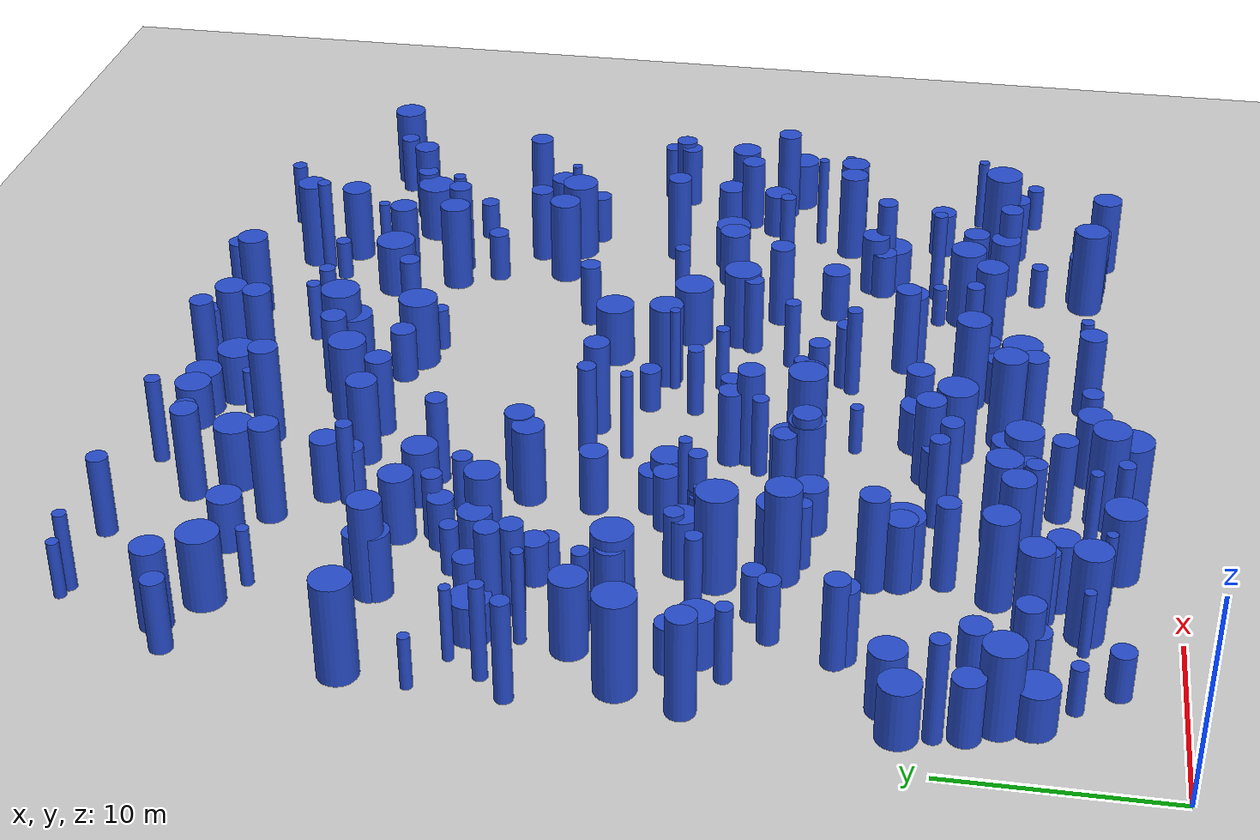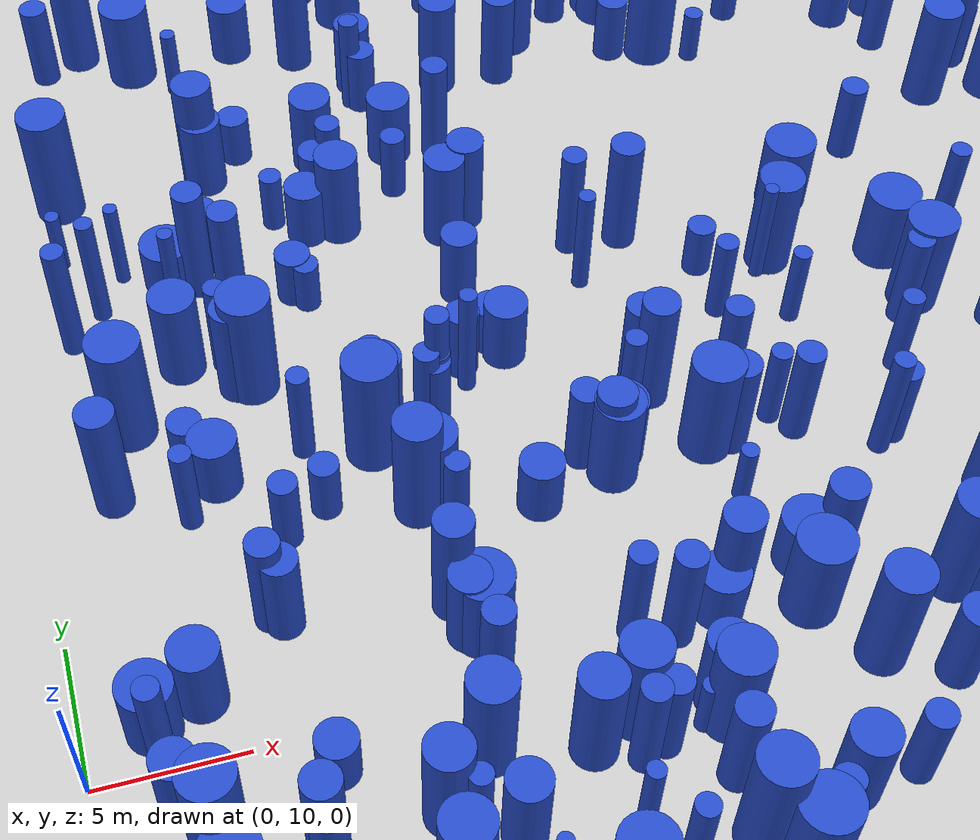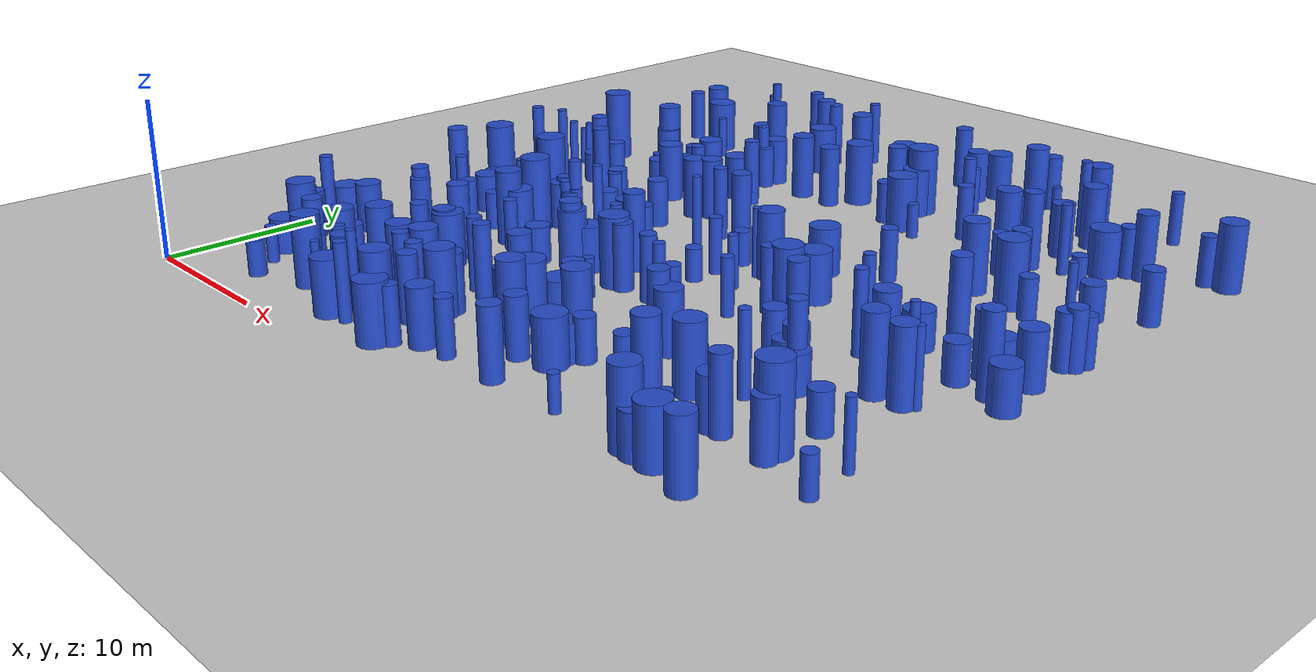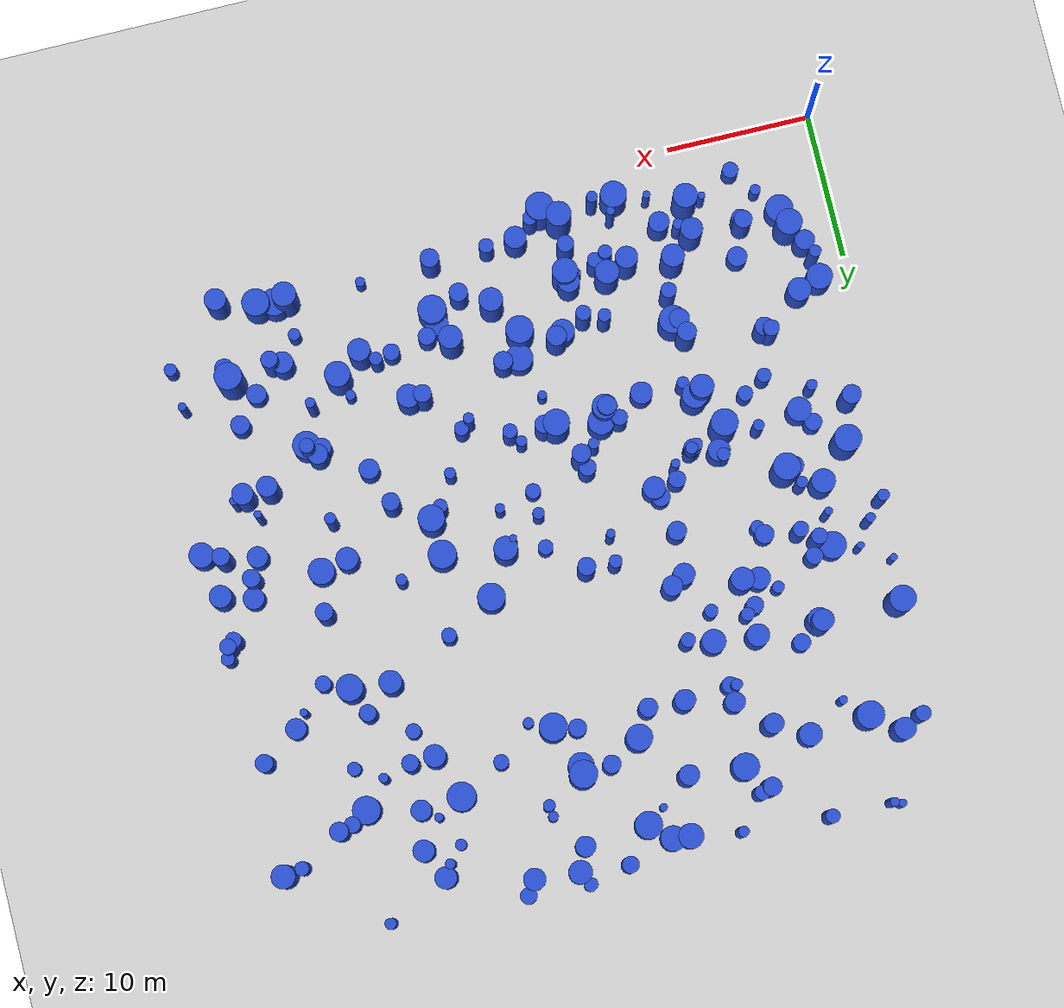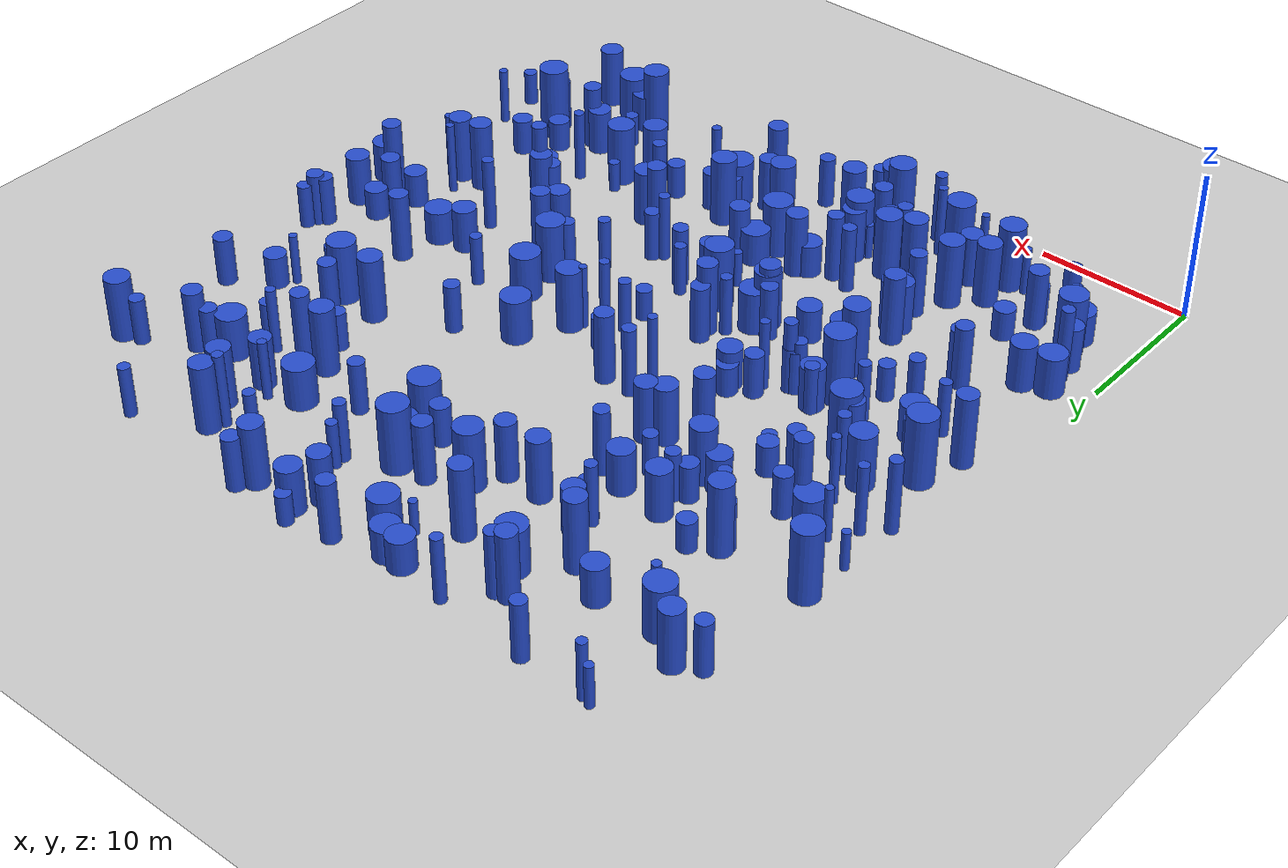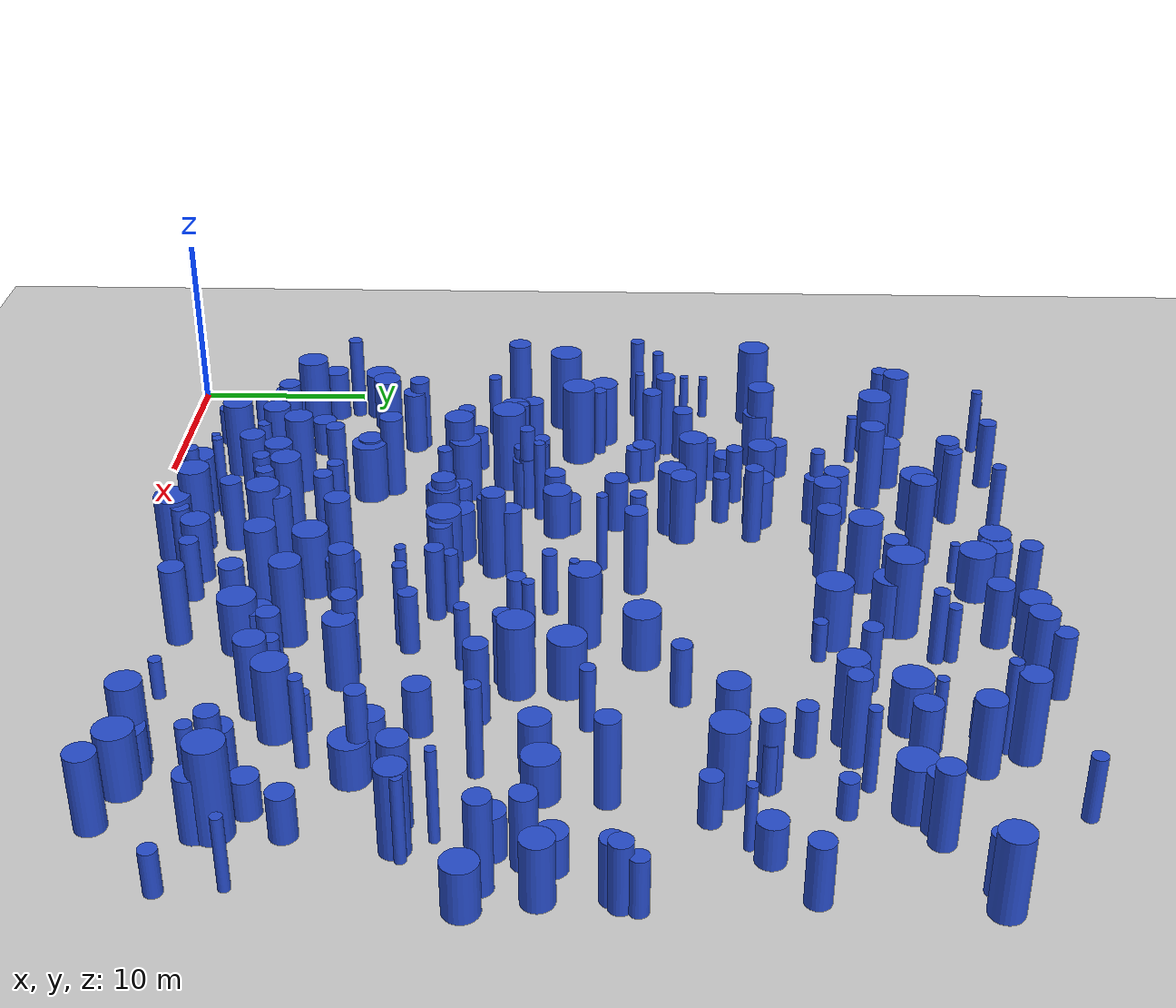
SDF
<sdf version="1.6">
 <world name="default">
  <light name="sun" type="directional">
   <pose>0 0 10 0 -0 0</pose>
   <diffuse>0.8 0.8 0.8 1</diffuse>
   <specular>0.1 0.1 0.1 1</specular>
   <attenuation>
    <range>1000</range>
    <constant>0.9</constant>
    <linear>0.01</linear>
    <quadratic>0.001</quadratic>
   </attenuation>
   <direction>-0.5 0.5 -1</direction>
  </light>
  <model name="ground_plane">
   <static>1</static>
   <link name="link">
    <collision name="collision">
     <geometry><plane><normal>0 0 1</normal><size>100 100</size></plane></geometry>
     <surface><friction><ode><mu>100</mu><mu2>50</mu2></ode></friction></surface>
    </collision>
    <visual name="visual">
     <cast_shadows>0</cast_shadows>
     <geometry><plane><normal>0 0 1</normal><size>100 100</size></plane></geometry>
     <material>
      <script><uri>file://media/materials/scripts/gazebo.material</uri><name>Gazebo/Grey</name></script>
     </material>
    </visual>
   </link>
  </model>
  <gravity>0 0 -9.8</gravity>
  <magnetic_field>6e-06 2.3e-05 -4.2e-05</magnetic_field>
  <atmosphere type="adiabatic"/>
  <physics name="default_physics" default="0" type="ode">
   <max_step_size>0.001</max_step_size>
   <real_time_factor>1</real_time_factor>
   <real_time_update_rate>1000</real_time_update_rate>
  </physics>
  <scene><ambient>0.4 0.4 0.4 1</ambient><background>0.7 0.7 0.7 1</background><shadows>1</shadows></scene>
  <spherical_coordinates>
   <surface_model>EARTH_WGS84</surface_model>
   <latitude_deg>0</latitude_deg>
   <longitude_deg>0</longitude_deg>
   <elevation>0</elevation>
   <heading_deg>0</heading_deg>
  </spherical_coordinates>
  <model name="0">
   <static>0</static>
   <link name="link">
    <inertial>
     <mass>2</mass>
     <inertia><ixx>1.36996</ixx><ixy>0</ixy><ixz>0</ixz><iyy>1.36996</iyy><iyz>0</iyz><izz>0.08114</izz></inertia>
    </inertial>
    <collision name="collision">
     <geometry><cylinder><length>2.82424</length><radius>0.284851</radius></cylinder></geometry>
     <surface><contact><collide_without_contact>1</collide_without_contact></contact></surface>
    </collision>
    <visual name="visual">
     <geometry><cylinder><length>2.82424</length><radius>0.284851</radius></cylinder></geometry>
     <material>
      <script><uri>file://media/materials/scripts/gazebo.material</uri><name>Gazebo/Blue</name></script>
     </material>
    </visual>
    <gravity>0</gravity>
   </link>
   <pose>5.6814 47.6667 1.41212 0 -0 0</pose>
  </model>
  <model name="1">
   <static>0</static>
   <link name="link">
    <inertial>
     <mass>2</mass>
     <inertia>
      <ixx>1.04273</ixx>
      <ixy>0</ixy>
      <ixz>0</ixz>
      <iyy>1.04273</iyy>
      <iyz>0</iyz>
      <izz>0.0959348</izz>
     </inertia>
    </inertial>
    <collision name="collision">
     <geometry><cylinder><length>2.44307</length><radius>0.309734</radius></cylinder></geometry>
     <surface><contact><collide_without_contact>1</collide_without_contact></contact></surface>
    </collision>
    <visual name="visual">
     <geometry><cylinder><length>2.44307</length><radius>0.309734</radius></cylinder></geometry>
     <material>
      <script><uri>file://media/materials/scripts/gazebo.material</uri><name>Gazebo/Blue</name></script>
     </material>
    </visual>
    <gravity>0</gravity>
   </link>
   <pose>22.6289 14.9061 1.22153 0 -0 0</pose>
  </model>
  <model name="2">
   <static>0</static>
   <link name="link">
    <inertial>
     <mass>2</mass>
     <inertia><ixx>2.4592</ixx><ixy>0</ixy><ixz>0</ixz><iyy>2.4592</iyy><iyz>0</iyz><izz>0.847323</izz></inertia>
    </inertial>
    <collision name="collision">
     <geometry><cylinder><length>3.49474</length><radius>0.920501</radius></cylinder></geometry>
     <surface><contact><collide_without_contact>1</collide_without_contact></contact></surface>
    </collision>
    <visual name="visual">
     <geometry><cylinder><length>3.49474</length><radius>0.920501</radius></cylinder></geometry>
     <material>
      <script><uri>file://media/materials/scripts/gazebo.material</uri><name>Gazebo/Blue</name></script>
     </material>
    </visual>
    <gravity>0</gravity>
   </link>
   <pose>14.6339 2.72103 1.74737 0 -0 0</pose>
  </model>
  <model name="3">
   <static>0</static>
   <link name="link">
    <inertial>
     <mass>2</mass>
     <inertia><ixx>4.1115</ixx><ixy>0</ixy><ixz>0</ixz><iyy>4.1115</iyy><iyz>0</iyz><izz>0.173022</izz></inertia>
    </inertial>
    <collision name="collision">
     <geometry><cylinder><length>4.91426</length><radius>0.415959</radius></cylinder></geometry>
     <surface><contact><collide_without_contact>1</collide_without_contact></contact></surface>
    </collision>
    <visual name="visual">
     <geometry><cylinder><length>4.91426</length><radius>0.415959</radius></cylinder></geometry>
     <material>
      <script><uri>file://media/materials/scripts/gazebo.material</uri><name>Gazebo/Blue</name></script>
     </material>
    </visual>
    <gravity>0</gravity>
   </link>
   <pose>13.7823 21.1588 2.45713 0 -0 0</pose>
  </model>
  <model name="4">
   <static>0</static>
   <link name="link">
    <inertial>
     <mass>2</mass>
     <inertia><ixx>1.69462</ixx><ixy>0</ixy><ixz>0</ixz><iyy>1.69462</iyy><iyz>0</iyz><izz>0.206012</izz></inertia>
    </inertial>
    <collision name="collision">
     <geometry><cylinder><length>3.09026</length><radius>0.453885</radius></cylinder></geometry>
     <surface><contact><collide_without_contact>1</collide_without_contact></contact></surface>
    </collision>
    <visual name="visual">
     <geometry><cylinder><length>3.09026</length><radius>0.453885</radius></cylinder></geometry>
     <material>
      <script><uri>file://media/materials/scripts/gazebo.material</uri><name>Gazebo/Blue</name></script>
     </material>
    </visual>
    <gravity>0</gravity>
   </link>
   <pose>13.7872 21.1345 1.54513 0 -0 0</pose>
  </model>
  <model name="5">
   <static>0</static>
   <link name="link">
    <inertial>
     <mass>2</mass>
     <inertia><ixx>1.58752</ixx><ixy>0</ixy><ixz>0</ixz><iyy>1.58752</iyy><iyz>0</iyz><izz>0.355159</izz></inertia>
    </inertial>
    <collision name="collision">
     <geometry><cylinder><length>2.90855</length><radius>0.595952</radius></cylinder></geometry>
     <surface><contact><collide_without_contact>1</collide_without_contact></contact></surface>
    </collision>
    <visual name="visual">
     <geometry><cylinder><length>2.90855</length><radius>0.595952</radius></cylinder></geometry>
     <material>
      <script><uri>file://media/materials/scripts/gazebo.material</uri><name>Gazebo/Blue</name></script>
     </material>
    </visual>
    <gravity>0</gravity>
   </link>
   <pose>15.128 22.7537 1.45428 0 -0 0</pose>
  </model>
  <model name="6">
   <static>0</static>
   <link name="link">
    <inertial>
     <mass>2</mass>
     <inertia><ixx>1.20336</ixx><ixy>0</ixy><ixz>0</ixz><iyy>1.20336</iyy><iyz>0</iyz><izz>0.750486</izz></inertia>
    </inertial>
    <collision name="collision">
     <geometry><cylinder><length>2.22906</length><radius>0.866306</radius></cylinder></geometry>
     <surface><contact><collide_without_contact>1</collide_without_contact></contact></surface>
    </collision>
    <visual name="visual">
     <geometry><cylinder><length>2.22906</length><radius>0.866306</radius></cylinder></geometry>
     <material>
      <script><uri>file://media/materials/scripts/gazebo.material</uri><name>Gazebo/Blue</name></script>
     </material>
    </visual>
    <gravity>0</gravity>
   </link>
   <pose>20.0201 46.401 1.11453 0 -0 0</pose>
  </model>
  <model name="7">
   <static>0</static>
   <link name="link">
    <inertial>
     <mass>2</mass>
     <inertia><ixx>2.10084</ixx><ixy>0</ixy><ixz>0</ixz><iyy>2.10084</iyy><iyz>0</iyz><izz>0.955069</izz></inertia>
    </inertial>
    <collision name="collision">
     <geometry><cylinder><length>3.12087</length><radius>0.977276</radius></cylinder></geometry>
     <surface><contact><collide_without_contact>1</collide_without_contact></contact></surface>
    </collision>
    <visual name="visual">
     <geometry><cylinder><length>3.12087</length><radius>0.977276</radius></cylinder></geometry>
     <material>
      <script><uri>file://media/materials/scripts/gazebo.material</uri><name>Gazebo/Blue</name></script>
     </material>
    </visual>
    <gravity>0</gravity>
   </link>
   <pose>31.8249 23.959 1.56043 0 -0 0</pose>
  </model>
  <model name="8">
   <static>0</static>
   <link name="link">
    <inertial>
     <mass>2</mass>
     <inertia>
      <ixx>0.880956</ixx>
      <ixy>0</ixy>
      <ixz>0</ixz>
      <iyy>0.880956</iyy>
      <iyz>0</iyz>
      <izz>0.363118</izz>
     </inertia>
    </inertial>
    <collision name="collision">
     <geometry><cylinder><length>2.04851</length><radius>0.602593</radius></cylinder></geometry>
     <surface><contact><collide_without_contact>1</collide_without_contact></contact></surface>
    </collision>
    <visual name="visual">
     <geometry><cylinder><length>2.04851</length><radius>0.602593</radius></cylinder></geometry>
     <material>
      <script><uri>file://media/materials/scripts/gazebo.material</uri><name>Gazebo/Blue</name></script>
     </material>
    </visual>
    <gravity>0</gravity>
   </link>
   <pose>9.53747 35.5063 1.02425 0 -0 0</pose>
  </model>
  <model name="9">
   <static>0</static>
   <link name="link">
    <inertial>
     <mass>2</mass>
     <inertia>
      <ixx>2.25253</ixx>
      <ixy>0</ixy>
      <ixz>0</ixz>
      <iyy>2.25253</iyy>
      <iyz>0</iyz>
      <izz>0.0659071</izz>
     </inertia>
    </inertial>
    <collision name="collision">
     <geometry><cylinder><length>3.64931</length><radius>0.256724</radius></cylinder></geometry>
     <surface><contact><collide_without_contact>1</collide_without_contact></contact></surface>
    </collision>
    <visual name="visual">
     <geometry><cylinder><length>3.64931</length><radius>0.256724</radius></cylinder></geometry>
     <material>
      <script><uri>file://media/materials/scripts/gazebo.material</uri><name>Gazebo/Blue</name></script>
     </material>
    </visual>
    <gravity>0</gravity>
   </link>
   <pose>4.20875 30.1664 1.82465 0 -0 0</pose>
  </model>
  <model name="10">
   <static>0</static>
   <link name="link">
    <inertial>
     <mass>2</mass>
     <inertia><ixx>3.95554</ixx><ixy>0</ixy><ixz>0</ixz><iyy>3.95554</iyy><iyz>0</iyz><izz>0.519828</izz></inertia>
    </inertial>
    <collision name="collision">
     <geometry><cylinder><length>4.7089</length><radius>0.720991</radius></cylinder></geometry>
     <surface><contact><collide_without_contact>1</collide_without_contact></contact></surface>
    </collision>
    <visual name="visual">
     <geometry><cylinder><length>4.7089</length><radius>0.720991</radius></cylinder></geometry>
     <material>
      <script><uri>file://media/materials/scripts/gazebo.material</uri><name>Gazebo/Blue</name></script>
     </material>
    </visual>
    <gravity>0</gravity>
   </link>
   <pose>42.2217 16.8427 2.35445 0 -0 0</pose>
  </model>
  <model name="11">
   <static>0</static>
   <link name="link">
    <inertial>
     <mass>2</mass>
     <inertia><ixx>3.77059</ixx><ixy>0</ixy><ixz>0</ixz><iyy>3.77059</iyy><iyz>0</iyz><izz>0.647013</izz></inertia>
    </inertial>
    <collision name="collision">
     <geometry><cylinder><length>4.5478</length><radius>0.804371</radius></cylinder></geometry>
     <surface><contact><collide_without_contact>1</collide_without_contact></contact></surface>
    </collision>
    <visual name="visual">
     <geometry><cylinder><length>4.5478</length><radius>0.804371</radius></cylinder></geometry>
     <material>
      <script><uri>file://media/materials/scripts/gazebo.material</uri><name>Gazebo/Blue</name></script>
     </material>
    </visual>
    <gravity>0</gravity>
   </link>
   <pose>11.7835 8.00404 2.2739 0 -0 0</pose>
  </model>
  <model name="12">
   <static>0</static>
   <link name="link">
    <inertial>
     <mass>2</mass>
     <inertia>
      <ixx>0.906578</ixx>
      <ixy>0</ixy>
      <ixz>0</ixz>
      <iyy>0.906578</iyy>
      <iyz>0</iyz>
      <izz>0.435424</izz>
     </inertia>
    </inertial>
    <collision name="collision">
     <geometry><cylinder><length>2.03303</length><radius>0.659867</radius></cylinder></geometry>
     <surface><contact><collide_without_contact>1</collide_without_contact></contact></surface>
    </collision>
    <visual name="visual">
     <geometry><cylinder><length>2.03303</length><radius>0.659867</radius></cylinder></geometry>
     <material>
      <script><uri>file://media/materials/scripts/gazebo.material</uri><name>Gazebo/Blue</name></script>
     </material>
    </visual>
    <gravity>0</gravity>
   </link>
   <pose>16.4375 23.5707 1.01651 0 -0 0</pose>
  </model>
  <model name="13">
   <static>0</static>
   <link name="link">
    <inertial>
     <mass>2</mass>
     <inertia><ixx>1.12414</ixx><ixy>0</ixy><ixz>0</ixz><iyy>1.12414</iyy><iyz>0</iyz><izz>0.883734</izz></inertia>
    </inertial>
    <collision name="collision">
     <geometry><cylinder><length>2.02328</length><radius>0.940072</radius></cylinder></geometry>
     <surface><contact><collide_without_contact>1</collide_without_contact></contact></surface>
    </collision>
    <visual name="visual">
     <geometry><cylinder><length>2.02328</length><radius>0.940072</radius></cylinder></geometry>
     <material>
      <script><uri>file://media/materials/scripts/gazebo.material</uri><name>Gazebo/Blue</name></script>
     </material>
    </visual>
    <gravity>0</gravity>
   </link>
   <pose>5.86916 29.5655 1.01164 0 -0 0</pose>
  </model>
  <model name="14">
   <static>0</static>
   <link name="link">
    <inertial>
     <mass>2</mass>
     <inertia><ixx>3.20253</ixx><ixy>0</ixy><ixz>0</ixz><iyy>3.20253</iyy><iyz>0</iyz><izz>0.453423</izz></inertia>
    </inertial>
    <collision name="collision">
     <geometry><cylinder><length>4.22551</length><radius>0.673367</radius></cylinder></geometry>
     <surface><contact><collide_without_contact>1</collide_without_contact></contact></surface>
    </collision>
    <visual name="visual">
     <geometry><cylinder><length>4.22551</length><radius>0.673367</radius></cylinder></geometry>
     <material>
      <script><uri>file://media/materials/scripts/gazebo.material</uri><name>Gazebo/Blue</name></script>
     </material>
    </visual>
    <gravity>0</gravity>
   </link>
   <pose>7.31113 23.8893 2.11276 0 -0 0</pose>
  </model>
  <model name="15">
   <static>0</static>
   <link name="link">
    <inertial>
     <mass>2</mass>
     <inertia><ixx>2.62862</ixx><ixy>0</ixy><ixz>0</ixz><iyy>2.62862</iyy><iyz>0</iyz><izz>0.931065</izz></inertia>
    </inertial>
    <collision name="collision">
     <geometry><cylinder><length>3.60257</length><radius>0.964917</radius></cylinder></geometry>
     <surface><contact><collide_without_contact>1</collide_without_contact></contact></surface>
    </collision>
    <visual name="visual">
     <geometry><cylinder><length>3.60257</length><radius>0.964917</radius></cylinder></geometry>
     <material>
      <script><uri>file://media/materials/scripts/gazebo.material</uri><name>Gazebo/Blue</name></script>
     </material>
    </visual>
    <gravity>0</gravity>
   </link>
   <pose>27.3165 37.1361 1.80129 0 -0 0</pose>
  </model>
  <model name="16">
   <static>0</static>
   <link name="link">
    <inertial>
     <mass>2</mass>
     <inertia><ixx>1.97388</ixx><ixy>0</ixy><ixz>0</ixz><iyy>1.97388</iyy><iyz>0</iyz><izz>0.383371</izz></inertia>
    </inertial>
    <collision name="collision">
     <geometry><cylinder><length>3.27004</length><radius>0.619169</radius></cylinder></geometry>
     <surface><contact><collide_without_contact>1</collide_without_contact></contact></surface>
    </collision>
    <visual name="visual">
     <geometry><cylinder><length>3.27004</length><radius>0.619169</radius></cylinder></geometry>
     <material>
      <script><uri>file://media/materials/scripts/gazebo.material</uri><name>Gazebo/Blue</name></script>
     </material>
    </visual>
    <gravity>0</gravity>
   </link>
   <pose>46.7633 34.854 1.63502 0 -0 0</pose>
  </model>
  <model name="17">
   <static>0</static>
   <link name="link">
    <inertial>
     <mass>2</mass>
     <inertia><ixx>2.1683</ixx><ixy>0</ixy><ixz>0</ixz><iyy>2.1683</iyy><iyz>0</iyz><izz>0.244924</izz></inertia>
    </inertial>
    <collision name="collision">
     <geometry><cylinder><length>3.50357</length><radius>0.494898</radius></cylinder></geometry>
     <surface><contact><collide_without_contact>1</collide_without_contact></contact></surface>
    </collision>
    <visual name="visual">
     <geometry><cylinder><length>3.50357</length><radius>0.494898</radius></cylinder></geometry>
     <material>
      <script><uri>file://media/materials/scripts/gazebo.material</uri><name>Gazebo/Blue</name></script>
     </material>
    </visual>
    <gravity>0</gravity>
   </link>
   <pose>20.5912 2.97204 1.75179 0 -0 0</pose>
  </model>
  <model name="18">
   <static>0</static>
   <link name="link">
    <inertial>
     <mass>2</mass>
     <inertia><ixx>4.07132</ixx><ixy>0</ixy><ixz>0</ixz><iyy>4.07132</iyy><iyz>0</iyz><izz>0.25791</izz></inertia>
    </inertial>
    <collision name="collision">
     <geometry><cylinder><length>4.86356</length><radius>0.507848</radius></cylinder></geometry>
     <surface><contact><collide_without_contact>1</collide_without_contact></contact></surface>
    </collision>
    <visual name="visual">
     <geometry><cylinder><length>4.86356</length><radius>0.507848</radius></cylinder></geometry>
     <material>
      <script><uri>file://media/materials/scripts/gazebo.material</uri><name>Gazebo/Blue</name></script>
     </material>
    </visual>
    <gravity>0</gravity>
   </link>
   <pose>38.9741 14.813 2.43178 0 -0 0</pose>
  </model>
  <model name="19">
   <static>0</static>
   <link name="link">
    <inertial>
     <mass>2</mass>
     <inertia>
      <ixx>0.997922</ixx>
      <ixy>0</ixy>
      <ixz>0</ixz>
      <iyy>0.997922</iyy>
      <iyz>0</iyz>
      <izz>0.310025</izz>
     </inertia>
    </inertial>
    <collision name="collision">
     <geometry><cylinder><length>2.24888</length><radius>0.556799</radius></cylinder></geometry>
     <surface><contact><collide_without_contact>1</collide_without_contact></contact></surface>
    </collision>
    <visual name="visual">
     <geometry><cylinder><length>2.24888</length><radius>0.556799</radius></cylinder></geometry>
     <material>
      <script><uri>file://media/materials/scripts/gazebo.material</uri><name>Gazebo/Blue</name></script>
     </material>
    </visual>
    <gravity>0</gravity>
   </link>
   <pose>6.32254 2.75765 1.12444 0 -0 0</pose>
  </model>
  <model name="20">
   <static>0</static>
   <link name="link">
    <inertial>
     <mass>2</mass>
     <inertia><ixx>4.13593</ixx><ixy>0</ixy><ixz>0</ixz><iyy>4.13593</iyy><iyz>0</iyz><izz>0.377057</izz></inertia>
    </inertial>
    <collision name="collision">
     <geometry><cylinder><length>4.86666</length><radius>0.614049</radius></cylinder></geometry>
     <surface><contact><collide_without_contact>1</collide_without_contact></contact></surface>
    </collision>
    <visual name="visual">
     <geometry><cylinder><length>4.86666</length><radius>0.614049</radius></cylinder></geometry>
     <material>
      <script><uri>file://media/materials/scripts/gazebo.material</uri><name>Gazebo/Blue</name></script>
     </material>
    </visual>
    <gravity>0</gravity>
   </link>
   <pose>46.3124 20.7601 2.43333 0 -0 0</pose>
  </model>
  <model name="21">
   <static>0</static>
   <link name="link">
    <inertial>
     <mass>2</mass>
     <inertia>
      <ixx>1.75689</ixx>
      <ixy>0</ixy>
      <ixz>0</ixz>
      <iyy>1.75689</iyy>
      <iyz>0</iyz>
      <izz>0.0651823</izz>
     </inertia>
    </inertial>
    <collision name="collision">
     <geometry><cylinder><length>3.21648</length><radius>0.255308</radius></cylinder></geometry>
     <surface><contact><collide_without_contact>1</collide_without_contact></contact></surface>
    </collision>
    <visual name="visual">
     <geometry><cylinder><length>3.21648</length><radius>0.255308</radius></cylinder></geometry>
     <material>
      <script><uri>file://media/materials/scripts/gazebo.material</uri><name>Gazebo/Blue</name></script>
     </material>
    </visual>
    <gravity>0</gravity>
   </link>
   <pose>8.77724 4.1816 1.60824 0 -0 0</pose>
  </model>
  <model name="22">
   <static>0</static>
   <link name="link">
    <inertial>
     <mass>2</mass>
     <inertia><ixx>2.50621</ixx><ixy>0</ixy><ixz>0</ixz><iyy>2.50621</iyy><iyz>0</iyz><izz>0.412755</izz></inertia>
    </inertial>
    <collision name="collision">
     <geometry><cylinder><length>3.7147</length><radius>0.64246</radius></cylinder></geometry>
     <surface><contact><collide_without_contact>1</collide_without_contact></contact></surface>
    </collision>
    <visual name="visual">
     <geometry><cylinder><length>3.7147</length><radius>0.64246</radius></cylinder></geometry>
     <material>
      <script><uri>file://media/materials/scripts/gazebo.material</uri><name>Gazebo/Blue</name></script>
     </material>
    </visual>
    <gravity>0</gravity>
   </link>
   <pose>6.86482 14.0884 1.85735 0 -0 0</pose>
  </model>
  <model name="23">
   <static>0</static>
   <link name="link">
    <inertial>
     <mass>2</mass>
     <inertia>
      <ixx>1.99669</ixx>
      <ixy>0</ixy>
      <ixz>0</ixz>
      <iyy>1.99669</iyy>
      <iyz>0</iyz>
      <izz>0.0728803</izz>
     </inertia>
    </inertial>
    <collision name="collision">
     <geometry><cylinder><length>3.42951</length><radius>0.269963</radius></cylinder></geometry>
     <surface><contact><collide_without_contact>1</collide_without_contact></contact></surface>
    </collision>
    <visual name="visual">
     <geometry><cylinder><length>3.42951</length><radius>0.269963</radius></cylinder></geometry>
     <material>
      <script><uri>file://media/materials/scripts/gazebo.material</uri><name>Gazebo/Blue</name></script>
     </material>
    </visual>
    <gravity>0</gravity>
   </link>
   <pose>43.393 32.1814 1.71475 0 -0 0</pose>
  </model>
  <model name="24">
   <static>0</static>
   <link name="link">
    <inertial>
     <mass>2</mass>
     <inertia><ixx>2.24741</ixx><ixy>0</ixy><ixz>0</ixz><iyy>2.24741</iyy><iyz>0</iyz><izz>0.278521</izz></inertia>
    </inertial>
    <collision name="collision">
     <geometry><cylinder><length>3.55653</length><radius>0.527751</radius></cylinder></geometry>
     <surface><contact><collide_without_contact>1</collide_without_contact></contact></surface>
    </collision>
    <visual name="visual">
     <geometry><cylinder><length>3.55653</length><radius>0.527751</radius></cylinder></geometry>
     <material>
      <script><uri>file://media/materials/scripts/gazebo.material</uri><name>Gazebo/Blue</name></script>
     </material>
    </visual>
    <gravity>0</gravity>
   </link>
   <pose>2.92159 42.1563 1.77827 0 -0 0</pose>
  </model>
  <model name="25">
   <static>0</static>
   <link name="link">
    <inertial>
     <mass>2</mass>
     <inertia><ixx>3.21255</ixx><ixy>0</ixy><ixz>0</ixz><iyy>3.21255</iyy><iyz>0</iyz><izz>0.847452</izz></inertia>
    </inertial>
    <collision name="collision">
     <geometry><cylinder><length>4.0906</length><radius>0.920571</radius></cylinder></geometry>
     <surface><contact><collide_without_contact>1</collide_without_contact></contact></surface>
    </collision>
    <visual name="visual">
     <geometry><cylinder><length>4.0906</length><radius>0.920571</radius></cylinder></geometry>
     <material>
      <script><uri>file://media/materials/scripts/gazebo.material</uri><name>Gazebo/Blue</name></script>
     </material>
    </visual>
    <gravity>0</gravity>
   </link>
   <pose>31.9637 21.5128 2.0453 0 -0 0</pose>
  </model>
  <model name="26">
   <static>0</static>
   <link name="link">
    <inertial>
     <mass>2</mass>
     <inertia><ixx>1.52925</ixx><ixy>0</ixy><ixz>0</ixz><iyy>1.52925</iyy><iyz>0</iyz><izz>0.603809</izz></inertia>
    </inertial>
    <collision name="collision">
     <geometry><cylinder><length>2.71368</length><radius>0.777051</radius></cylinder></geometry>
     <surface><contact><collide_without_contact>1</collide_without_contact></contact></surface>
    </collision>
    <visual name="visual">
     <geometry><cylinder><length>2.71368</length><radius>0.777051</radius></cylinder></geometry>
     <material>
      <script><uri>file://media/materials/scripts/gazebo.material</uri><name>Gazebo/Blue</name></script>
     </material>
    </visual>
    <gravity>0</gravity>
   </link>
   <pose>16.7592 22.9378 1.35684 0 -0 0</pose>
  </model>
  <model name="27">
   <static>0</static>
   <link name="link">
    <inertial>
     <mass>2</mass>
     <inertia><ixx>1.09126</ixx><ixy>0</ixy><ixz>0</ixz><iyy>1.09126</iyy><iyz>0</iyz><izz>0.36449</izz></inertia>
    </inertial>
    <collision name="collision">
     <geometry><cylinder><length>2.3354</length><radius>0.60373</radius></cylinder></geometry>
     <surface><contact><collide_without_contact>1</collide_without_contact></contact></surface>
    </collision>
    <visual name="visual">
     <geometry><cylinder><length>2.3354</length><radius>0.60373</radius></cylinder></geometry>
     <material>
      <script><uri>file://media/materials/scripts/gazebo.material</uri><name>Gazebo/Blue</name></script>
     </material>
    </visual>
    <gravity>0</gravity>
   </link>
   <pose>5.09837 21.0818 1.1677 0 -0 0</pose>
  </model>
  <model name="28">
   <static>0</static>
   <link name="link">
    <inertial>
     <mass>2</mass>
     <inertia><ixx>4.33046</ixx><ixy>0</ixy><ixz>0</ixz><iyy>4.33046</iyy><iyz>0</iyz><izz>0.751665</izz></inertia>
    </inertial>
    <collision name="collision">
     <geometry><cylinder><length>4.87112</length><radius>0.866986</radius></cylinder></geometry>
     <surface><contact><collide_without_contact>1</collide_without_contact></contact></surface>
    </collision>
    <visual name="visual">
     <geometry><cylinder><length>4.87112</length><radius>0.866986</radius></cylinder></geometry>
     <material>
      <script><uri>file://media/materials/scripts/gazebo.material</uri><name>Gazebo/Blue</name></script>
     </material>
    </visual>
    <gravity>0</gravity>
   </link>
   <pose>18.6765 3.41081 2.43556 0 -0 0</pose>
  </model>
  <model name="29">
   <static>0</static>
   <link name="link">
    <inertial>
     <mass>2</mass>
     <inertia><ixx>3.4064</ixx><ixy>0</ixy><ixz>0</ixz><iyy>3.4064</iyy><iyz>0</iyz><izz>0.0952166</izz></inertia>
    </inertial>
    <collision name="collision">
     <geometry><cylinder><length>4.48918</length><radius>0.308572</radius></cylinder></geometry>
     <surface><contact><collide_without_contact>1</collide_without_contact></contact></surface>
    </collision>
    <visual name="visual">
     <geometry><cylinder><length>4.48918</length><radius>0.308572</radius></cylinder></geometry>
     <material>
      <script><uri>file://media/materials/scripts/gazebo.material</uri><name>Gazebo/Blue</name></script>
     </material>
    </visual>
    <gravity>0</gravity>
   </link>
   <pose>20.4595 25.4538 2.24459 0 -0 0</pose>
  </model>
  <model name="30">
   <static>0</static>
   <link name="link">
    <inertial>
     <mass>2</mass>
     <inertia><ixx>2.75593</ixx><ixy>0</ixy><ixz>0</ixz><iyy>2.75593</iyy><iyz>0</iyz><izz>0.688056</izz></inertia>
    </inertial>
    <collision name="collision">
     <geometry><cylinder><length>3.80413</length><radius>0.829491</radius></cylinder></geometry>
     <surface><contact><collide_without_contact>1</collide_without_contact></contact></surface>
    </collision>
    <visual name="visual">
     <geometry><cylinder><length>3.80413</length><radius>0.829491</radius></cylinder></geometry>
     <material>
      <script><uri>file://media/materials/scripts/gazebo.material</uri><name>Gazebo/Blue</name></script>
     </material>
    </visual>
    <gravity>0</gravity>
   </link>
   <pose>5.5824 25.3243 1.90206 0 -0 0</pose>
  </model>
  <model name="31">
   <static>0</static>
   <link name="link">
    <inertial>
     <mass>2</mass>
     <inertia><ixx>3.2928</ixx><ixy>0</ixy><ixz>0</ixz><iyy>3.2928</iyy><iyz>0</iyz><izz>0.138663</izz></inertia>
    </inertial>
    <collision name="collision">
     <geometry><cylinder><length>4.39782</length><radius>0.372375</radius></cylinder></geometry>
     <surface><contact><collide_without_contact>1</collide_without_contact></contact></surface>
    </collision>
    <visual name="visual">
     <geometry><cylinder><length>4.39782</length><radius>0.372375</radius></cylinder></geometry>
     <material>
      <script><uri>file://media/materials/scripts/gazebo.material</uri><name>Gazebo/Blue</name></script>
     </material>
    </visual>
    <gravity>0</gravity>
   </link>
   <pose>16.6334 46.9755 2.19891 0 -0 0</pose>
  </model>
  <model name="32">
   <static>0</static>
   <link name="link">
    <inertial>
     <mass>2</mass>
     <inertia><ixx>2.55489</ixx><ixy>0</ixy><ixz>0</ixz><iyy>2.55489</iyy><iyz>0</iyz><izz>0.788576</izz></inertia>
    </inertial>
    <collision name="collision">
     <geometry><cylinder><length>3.6005</length><radius>0.888018</radius></cylinder></geometry>
     <surface><contact><collide_without_contact>1</collide_without_contact></contact></surface>
    </collision>
    <visual name="visual">
     <geometry><cylinder><length>3.6005</length><radius>0.888018</radius></cylinder></geometry>
     <material>
      <script><uri>file://media/materials/scripts/gazebo.material</uri><name>Gazebo/Blue</name></script>
     </material>
    </visual>
    <gravity>0</gravity>
   </link>
   <pose>12.5968 17.555 1.80025 0 -0 0</pose>
  </model>
  <model name="33">
   <static>0</static>
   <link name="link">
    <inertial>
     <mass>2</mass>
     <inertia><ixx>3.32594</ixx><ixy>0</ixy><ixz>0</ixz><iyy>3.32594</iyy><iyz>0</iyz><izz>0.675286</izz></inertia>
    </inertial>
    <collision name="collision">
     <geometry><cylinder><length>4.23436</length><radius>0.821758</radius></cylinder></geometry>
     <surface><contact><collide_without_contact>1</collide_without_contact></contact></surface>
    </collision>
    <visual name="visual">
     <geometry><cylinder><length>4.23436</length><radius>0.821758</radius></cylinder></geometry>
     <material>
      <script><uri>file://media/materials/scripts/gazebo.material</uri><name>Gazebo/Blue</name></script>
     </material>
    </visual>
    <gravity>0</gravity>
   </link>
   <pose>47.2032 42.5605 2.11718 0 -0 0</pose>
  </model>
  <model name="34">
   <static>0</static>
   <link name="link">
    <inertial>
     <mass>2</mass>
     <inertia><ixx>2.04762</ixx><ixy>0</ixy><ixz>0</ixz><iyy>2.04762</iyy><iyz>0</iyz><izz>0.252697</izz></inertia>
    </inertial>
    <collision name="collision">
     <geometry><cylinder><length>3.39524</length><radius>0.502689</radius></cylinder></geometry>
     <surface><contact><collide_without_contact>1</collide_without_contact></contact></surface>
    </collision>
    <visual name="visual">
     <geometry><cylinder><length>3.39524</length><radius>0.502689</radius></cylinder></geometry>
     <material>
      <script><uri>file://media/materials/scripts/gazebo.material</uri><name>Gazebo/Blue</name></script>
     </material>
    </visual>
    <gravity>0</gravity>
   </link>
   <pose>28.5365 15.9625 1.69762 0 -0 0</pose>
  </model>
  <model name="35">
   <static>0</static>
   <link name="link">
    <inertial>
     <mass>2</mass>
     <inertia><ixx>3.57551</ixx><ixy>0</ixy><ixz>0</ixz><iyy>3.57551</iyy><iyz>0</iyz><izz>0.622149</izz></inertia>
    </inertial>
    <collision name="collision">
     <geometry><cylinder><length>4.42568</length><radius>0.788764</radius></cylinder></geometry>
     <surface><contact><collide_without_contact>1</collide_without_contact></contact></surface>
    </collision>
    <visual name="visual">
     <geometry><cylinder><length>4.42568</length><radius>0.788764</radius></cylinder></geometry>
     <material>
      <script><uri>file://media/materials/scripts/gazebo.material</uri><name>Gazebo/Blue</name></script>
     </material>
    </visual>
    <gravity>0</gravity>
   </link>
   <pose>37.2175 31.6348 2.21284 0 -0 0</pose>
  </model>
  <model name="36">
   <static>0</static>
   <link name="link">
    <inertial>
     <mass>2</mass>
     <inertia><ixx>2.47359</ixx><ixy>0</ixy><ixz>0</ixz><iyy>2.47359</iyy><iyz>0</iyz><izz>0.571806</izz></inertia>
    </inertial>
    <collision name="collision">
     <geometry><cylinder><length>3.623</length><radius>0.756179</radius></cylinder></geometry>
     <surface><contact><collide_without_contact>1</collide_without_contact></contact></surface>
    </collision>
    <visual name="visual">
     <geometry><cylinder><length>3.623</length><radius>0.756179</radius></cylinder></geometry>
     <material>
      <script><uri>file://media/materials/scripts/gazebo.material</uri><name>Gazebo/Blue</name></script>
     </material>
    </visual>
    <gravity>0</gravity>
   </link>
   <pose>19.0534 7.89403 1.8115 0 -0 0</pose>
  </model>
  <model name="37">
   <static>0</static>
   <link name="link">
    <inertial>
     <mass>2</mass>
     <inertia><ixx>3.28854</ixx><ixy>0</ixy><ixz>0</ixz><iyy>3.28854</iyy><iyz>0</iyz><izz>0.530708</izz></inertia>
    </inertial>
    <collision name="collision">
     <geometry><cylinder><length>4.259</length><radius>0.728497</radius></cylinder></geometry>
     <surface><contact><collide_without_contact>1</collide_without_contact></contact></surface>
    </collision>
    <visual name="visual">
     <geometry><cylinder><length>4.259</length><radius>0.728497</radius></cylinder></geometry>
     <material>
      <script><uri>file://media/materials/scripts/gazebo.material</uri><name>Gazebo/Blue</name></script>
     </material>
    </visual>
    <gravity>0</gravity>
   </link>
   <pose>18.3013 37.5129 2.1295 0 -0 0</pose>
  </model>
  <model name="38">
   <static>0</static>
   <link name="link">
    <inertial>
     <mass>2</mass>
     <inertia><ixx>1.8464</ixx><ixy>0</ixy><ixz>0</ixz><iyy>1.8464</iyy><iyz>0</iyz><izz>0.210959</izz></inertia>
    </inertial>
    <collision name="collision">
     <geometry><cylinder><length>3.23195</length><radius>0.459303</radius></cylinder></geometry>
     <surface><contact><collide_without_contact>1</collide_without_contact></contact></surface>
    </collision>
    <visual name="visual">
     <geometry><cylinder><length>3.23195</length><radius>0.459303</radius></cylinder></geometry>
     <material>
      <script><uri>file://media/materials/scripts/gazebo.material</uri><name>Gazebo/Blue</name></script>
     </material>
    </visual>
    <gravity>0</gravity>
   </link>
   <pose>11.6565 21.8837 1.61598 0 -0 0</pose>
  </model>
  <model name="39">
   <static>0</static>
   <link name="link">
    <inertial>
     <mass>2</mass>
     <inertia><ixx>1.9999</ixx><ixy>0</ixy><ixz>0</ixz><iyy>1.9999</iyy><iyz>0</iyz><izz>0.310791</izz></inertia>
    </inertial>
    <collision name="collision">
     <geometry><cylinder><length>3.32671</length><radius>0.557487</radius></cylinder></geometry>
     <surface><contact><collide_without_contact>1</collide_without_contact></contact></surface>
    </collision>
    <visual name="visual">
     <geometry><cylinder><length>3.32671</length><radius>0.557487</radius></cylinder></geometry>
     <material>
      <script><uri>file://media/materials/scripts/gazebo.material</uri><name>Gazebo/Blue</name></script>
     </material>
    </visual>
    <gravity>0</gravity>
   </link>
   <pose>46.8839 26.2899 1.66335 0 -0 0</pose>
  </model>
  <model name="40">
   <static>0</static>
   <link name="link">
    <inertial>
     <mass>2</mass>
     <inertia><ixx>1.69462</ixx><ixy>0</ixy><ixz>0</ixz><iyy>1.69462</iyy><iyz>0</iyz><izz>0.809361</izz></inertia>
    </inertial>
    <collision name="collision">
     <geometry><cylinder><length>2.78202</length><radius>0.899645</radius></cylinder></geometry>
     <surface><contact><collide_without_contact>1</collide_without_contact></contact></surface>
    </collision>
    <visual name="visual">
     <geometry><cylinder><length>2.78202</length><radius>0.899645</radius></cylinder></geometry>
     <material>
      <script><uri>file://media/materials/scripts/gazebo.material</uri><name>Gazebo/Blue</name></script>
     </material>
    </visual>
    <gravity>0</gravity>
   </link>
   <pose>2.25113 11.4808 1.39101 0 -0 0</pose>
  </model>
  <model name="41">
   <static>0</static>
   <link name="link">
    <inertial>
     <mass>2</mass>
     <inertia>
      <ixx>2.56622</ixx>
      <ixy>0</ixy>
      <ixz>0</ixz>
      <iyy>2.56622</iyy>
      <iyz>0</iyz>
      <izz>0.0997864</izz>
     </inertia>
    </inertial>
    <collision name="collision">
     <geometry><cylinder><length>3.88561</length><radius>0.31589</radius></cylinder></geometry>
     <surface><contact><collide_without_contact>1</collide_without_contact></contact></surface>
    </collision>
    <visual name="visual">
     <geometry><cylinder><length>3.88561</length><radius>0.31589</radius></cylinder></geometry>
     <material>
      <script><uri>file://media/materials/scripts/gazebo.material</uri><name>Gazebo/Blue</name></script>
     </material>
    </visual>
    <gravity>0</gravity>
   </link>
   <pose>6.3063 47.4544 1.9428 0 -0 0</pose>
  </model>
  <model name="42">
   <static>0</static>
   <link name="link">
    <inertial>
     <mass>2</mass>
     <inertia><ixx>1.89672</ixx><ixy>0</ixy><ixz>0</ixz><iyy>1.89672</iyy><iyz>0</iyz><izz>0.219729</izz></inertia>
    </inertial>
    <collision name="collision">
     <geometry><cylinder><length>3.27432</length><radius>0.468753</radius></cylinder></geometry>
     <surface><contact><collide_without_contact>1</collide_without_contact></contact></surface>
    </collision>
    <visual name="visual">
     <geometry><cylinder><length>3.27432</length><radius>0.468753</radius></cylinder></geometry>
     <material>
      <script><uri>file://media/materials/scripts/gazebo.material</uri><name>Gazebo/Blue</name></script>
     </material>
    </visual>
    <gravity>0</gravity>
   </link>
   <pose>12.7332 32.8428 1.63716 0 -0 0</pose>
  </model>
  <model name="43">
   <static>0</static>
   <link name="link">
    <inertial>
     <mass>2</mass>
     <inertia>
      <ixx>0.804984</ixx>
      <ixy>0</ixy>
      <ixz>0</ixz>
      <iyy>0.804984</iyy>
      <iyz>0</iyz>
      <izz>0.236242</izz>
     </inertia>
    </inertial>
    <collision name="collision">
     <geometry><cylinder><length>2.03007</length><radius>0.486048</radius></cylinder></geometry>
     <surface><contact><collide_without_contact>1</collide_without_contact></contact></surface>
    </collision>
    <visual name="visual">
     <geometry><cylinder><length>2.03007</length><radius>0.486048</radius></cylinder></geometry>
     <material>
      <script><uri>file://media/materials/scripts/gazebo.material</uri><name>Gazebo/Blue</name></script>
     </material>
    </visual>
    <gravity>0</gravity>
   </link>
   <pose>27.3471 47.9507 1.01503 0 -0 0</pose>
  </model>
  <model name="44">
   <static>0</static>
   <link name="link">
    <inertial>
     <mass>2</mass>
     <inertia><ixx>4.17462</ixx><ixy>0</ixy><ixz>0</ixz><iyy>4.17462</iyy><iyz>0</iyz><izz>0.119229</izz></inertia>
    </inertial>
    <collision name="collision">
     <geometry><cylinder><length>4.96891</length><radius>0.345295</radius></cylinder></geometry>
     <surface><contact><collide_without_contact>1</collide_without_contact></contact></surface>
    </collision>
    <visual name="visual">
     <geometry><cylinder><length>4.96891</length><radius>0.345295</radius></cylinder></geometry>
     <material>
      <script><uri>file://media/materials/scripts/gazebo.material</uri><name>Gazebo/Blue</name></script>
     </material>
    </visual>
    <gravity>0</gravity>
   </link>
   <pose>36.1613 44.4005 2.48445 0 -0 0</pose>
  </model>
  <model name="45">
   <static>0</static>
   <link name="link">
    <inertial>
     <mass>2</mass>
     <inertia><ixx>3.37145</ixx><ixy>0</ixy><ixz>0</ixz><iyy>3.37145</iyy><iyz>0</iyz><izz>0.593405</izz></inertia>
    </inertial>
    <collision name="collision">
     <geometry><cylinder><length>4.29517</length><radius>0.770328</radius></cylinder></geometry>
     <surface><contact><collide_without_contact>1</collide_without_contact></contact></surface>
    </collision>
    <visual name="visual">
     <geometry><cylinder><length>4.29517</length><radius>0.770328</radius></cylinder></geometry>
     <material>
      <script><uri>file://media/materials/scripts/gazebo.material</uri><name>Gazebo/Blue</name></script>
     </material>
    </visual>
    <gravity>0</gravity>
   </link>
   <pose>10.0825 6.46261 2.14758 0 -0 0</pose>
  </model>
  <model name="46">
   <static>0</static>
   <link name="link">
    <inertial>
     <mass>2</mass>
     <inertia><ixx>4.24125</ixx><ixy>0</ixy><ixz>0</ixz><iyy>4.24125</iyy><iyz>0</iyz><izz>0.418546</izz></inertia>
    </inertial>
    <collision name="collision">
     <geometry><cylinder><length>4.91852</length><radius>0.646951</radius></cylinder></geometry>
     <surface><contact><collide_without_contact>1</collide_without_contact></contact></surface>
    </collision>
    <visual name="visual">
     <geometry><cylinder><length>4.91852</length><radius>0.646951</radius></cylinder></geometry>
     <material>
      <script><uri>file://media/materials/scripts/gazebo.material</uri><name>Gazebo/Blue</name></script>
     </material>
    </visual>
    <gravity>0</gravity>
   </link>
   <pose>21.0936 19.7391 2.45926 0 -0 0</pose>
  </model>
  <model name="47">
   <static>0</static>
   <link name="link">
    <inertial>
     <mass>2</mass>
     <inertia><ixx>4.30581</ixx><ixy>0</ixy><ixz>0</ixz><iyy>4.30581</iyy><iyz>0</iyz><izz>0.874701</izz></inertia>
    </inertial>
    <collision name="collision">
     <geometry><cylinder><length>4.81775</length><radius>0.935255</radius></cylinder></geometry>
     <surface><contact><collide_without_contact>1</collide_without_contact></contact></surface>
    </collision>
    <visual name="visual">
     <geometry><cylinder><length>4.81775</length><radius>0.935255</radius></cylinder></geometry>
     <material>
      <script><uri>file://media/materials/scripts/gazebo.material</uri><name>Gazebo/Blue</name></script>
     </material>
    </visual>
    <gravity>0</gravity>
   </link>
   <pose>11.1965 19.9775 2.40888 0 -0 0</pose>
  </model>
  <model name="48">
   <static>0</static>
   <link name="link">
    <inertial>
     <mass>2</mass>
     <inertia><ixx>3.38207</ixx><ixy>0</ixy><ixz>0</ixz><iyy>3.38207</iyy><iyz>0</iyz><izz>0.486769</izz></inertia>
    </inertial>
    <collision name="collision">
     <geometry><cylinder><length>4.3396</length><radius>0.697689</radius></cylinder></geometry>
     <surface><contact><collide_without_contact>1</collide_without_contact></contact></surface>
    </collision>
    <visual name="visual">
     <geometry><cylinder><length>4.3396</length><radius>0.697689</radius></cylinder></geometry>
     <material>
      <script><uri>file://media/materials/scripts/gazebo.material</uri><name>Gazebo/Blue</name></script>
     </material>
    </visual>
    <gravity>0</gravity>
   </link>
   <pose>20.7865 11.4476 2.1698 0 -0 0</pose>
  </model>
  <model name="49">
   <static>0</static>
   <link name="link">
    <inertial>
     <mass>2</mass>
     <inertia><ixx>2.81765</ixx><ixy>0</ixy><ixz>0</ixz><iyy>2.81765</iyy><iyz>0</iyz><izz>0.156137</izz></inertia>
    </inertial>
    <collision name="collision">
     <geometry><cylinder><length>4.05431</length><radius>0.395141</radius></cylinder></geometry>
     <surface><contact><collide_without_contact>1</collide_without_contact></contact></surface>
    </collision>
    <visual name="visual">
     <geometry><cylinder><length>4.05431</length><radius>0.395141</radius></cylinder></geometry>
     <material>
      <script><uri>file://media/materials/scripts/gazebo.material</uri><name>Gazebo/Blue</name></script>
     </material>
    </visual>
    <gravity>0</gravity>
   </link>
   <pose>7.03901 25.0928 2.02716 0 -0 0</pose>
  </model>
  <model name="50">
   <static>0</static>
   <link name="link">
    <inertial>
     <mass>2</mass>
     <inertia><ixx>2.06213</ixx><ixy>0</ixy><ixz>0</ixz><iyy>2.06213</iyy><iyz>0</iyz><izz>0.143933</izz></inertia>
    </inertial>
    <collision name="collision">
     <geometry><cylinder><length>3.45558</length><radius>0.379384</radius></cylinder></geometry>
     <surface><contact><collide_without_contact>1</collide_without_contact></contact></surface>
    </collision>
    <visual name="visual">
     <geometry><cylinder><length>3.45558</length><radius>0.379384</radius></cylinder></geometry>
     <material>
      <script><uri>file://media/materials/scripts/gazebo.material</uri><name>Gazebo/Blue</name></script>
     </material>
    </visual>
    <gravity>0</gravity>
   </link>
   <pose>24.7799 17.7722 1.72779 0 -0 0</pose>
  </model>
  <model name="51">
   <static>0</static>
   <link name="link">
    <inertial>
     <mass>2</mass>
     <inertia><ixx>2.12546</ixx><ixy>0</ixy><ixz>0</ixz><iyy>2.12546</iyy><iyz>0</iyz><izz>0.256393</izz></inertia>
    </inertial>
    <collision name="collision">
     <geometry><cylinder><length>3.46173</length><radius>0.506353</radius></cylinder></geometry>
     <surface><contact><collide_without_contact>1</collide_without_contact></contact></surface>
    </collision>
    <visual name="visual">
     <geometry><cylinder><length>3.46173</length><radius>0.506353</radius></cylinder></geometry>
     <material>
      <script><uri>file://media/materials/scripts/gazebo.material</uri><name>Gazebo/Blue</name></script>
     </material>
    </visual>
    <gravity>0</gravity>
   </link>
   <pose>23.9364 4.12695 1.73086 0 -0 0</pose>
  </model>
  <model name="52">
   <static>0</static>
   <link name="link">
    <inertial>
     <mass>2</mass>
     <inertia><ixx>2.41043</ixx><ixy>0</ixy><ixz>0</ixz><iyy>2.41043</iyy><iyz>0</iyz><izz>0.952559</izz></inertia>
    </inertial>
    <collision name="collision">
     <geometry><cylinder><length>3.40659</length><radius>0.975991</radius></cylinder></geometry>
     <surface><contact><collide_without_contact>1</collide_without_contact></contact></surface>
    </collision>
    <visual name="visual">
     <geometry><cylinder><length>3.40659</length><radius>0.975991</radius></cylinder></geometry>
     <material>
      <script><uri>file://media/materials/scripts/gazebo.material</uri><name>Gazebo/Blue</name></script>
     </material>
    </visual>
    <gravity>0</gravity>
   </link>
   <pose>12.7603 12.0977 1.7033 0 -0 0</pose>
  </model>
  <model name="53">
   <static>0</static>
   <link name="link">
    <inertial>
     <mass>2</mass>
     <inertia><ixx>2.76585</ixx><ixy>0</ixy><ixz>0</ixz><iyy>2.76585</iyy><iyz>0</iyz><izz>0.237555</izz></inertia>
    </inertial>
    <collision name="collision">
     <geometry><cylinder><length>3.98528</length><radius>0.487396</radius></cylinder></geometry>
     <surface><contact><collide_without_contact>1</collide_without_contact></contact></surface>
    </collision>
    <visual name="visual">
     <geometry><cylinder><length>3.98528</length><radius>0.487396</radius></cylinder></geometry>
     <material>
      <script><uri>file://media/materials/scripts/gazebo.material</uri><name>Gazebo/Blue</name></script>
     </material>
    </visual>
    <gravity>0</gravity>
   </link>
   <pose>31.1916 20.8429 1.99264 0 -0 0</pose>
  </model>
  <model name="54">
   <static>0</static>
   <link name="link">
    <inertial>
     <mass>2</mass>
     <inertia><ixx>3.78955</ixx><ixy>0</ixy><ixz>0</ixz><iyy>3.78955</iyy><iyz>0</iyz><izz>0.716468</izz></inertia>
    </inertial>
    <collision name="collision">
     <geometry><cylinder><length>4.53739</length><radius>0.846444</radius></cylinder></geometry>
     <surface><contact><collide_without_contact>1</collide_without_contact></contact></surface>
    </collision>
    <visual name="visual">
     <geometry><cylinder><length>4.53739</length><radius>0.846444</radius></cylinder></geometry>
     <material>
      <script><uri>file://media/materials/scripts/gazebo.material</uri><name>Gazebo/Blue</name></script>
     </material>
    </visual>
    <gravity>0</gravity>
   </link>
   <pose>38.1122 4.28516 2.26869 0 -0 0</pose>
  </model>
  <model name="55">
   <static>0</static>
   <link name="link">
    <inertial>
     <mass>2</mass>
     <inertia><ixx>3.00682</ixx><ixy>0</ixy><ixz>0</ixz><iyy>3.00682</iyy><iyz>0</iyz><izz>0.336828</izz></inertia>
    </inertial>
    <collision name="collision">
     <geometry><cylinder><length>4.1268</length><radius>0.580369</radius></cylinder></geometry>
     <surface><contact><collide_without_contact>1</collide_without_contact></contact></surface>
    </collision>
    <visual name="visual">
     <geometry><cylinder><length>4.1268</length><radius>0.580369</radius></cylinder></geometry>
     <material>
      <script><uri>file://media/materials/scripts/gazebo.material</uri><name>Gazebo/Blue</name></script>
     </material>
    </visual>
    <gravity>0</gravity>
   </link>
   <pose>24.4847 47.3087 2.0634 0 -0 0</pose>
  </model>
  <model name="56">
   <static>0</static>
   <link name="link">
    <inertial>
     <mass>2</mass>
     <inertia>
      <ixx>0.820719</ixx>
      <ixy>0</ixy>
      <ixz>0</ixz>
      <iyy>0.820719</iyy>
      <iyz>0</iyz>
      <izz>0.154265</izz>
     </inertia>
    </inertial>
    <collision name="collision">
     <geometry><cylinder><length>2.11223</length><radius>0.392766</radius></cylinder></geometry>
     <surface><contact><collide_without_contact>1</collide_without_contact></contact></surface>
    </collision>
    <visual name="visual">
     <geometry><cylinder><length>2.11223</length><radius>0.392766</radius></cylinder></geometry>
     <material>
      <script><uri>file://media/materials/scripts/gazebo.material</uri><name>Gazebo/Blue</name></script>
     </material>
    </visual>
    <gravity>0</gravity>
   </link>
   <pose>35.2204 43.2712 1.05612 0 -0 0</pose>
  </model>
  <model name="57">
   <static>0</static>
   <link name="link">
    <inertial>
     <mass>2</mass>
     <inertia><ixx>1.80639</ixx><ixy>0</ixy><ixz>0</ixz><iyy>1.80639</iyy><iyz>0</iyz><izz>0.301855</izz></inertia>
    </inertial>
    <collision name="collision">
     <geometry><cylinder><length>3.15163</length><radius>0.549413</radius></cylinder></geometry>
     <surface><contact><collide_without_contact>1</collide_without_contact></contact></surface>
    </collision>
    <visual name="visual">
     <geometry><cylinder><length>3.15163</length><radius>0.549413</radius></cylinder></geometry>
     <material>
      <script><uri>file://media/materials/scripts/gazebo.material</uri><name>Gazebo/Blue</name></script>
     </material>
    </visual>
    <gravity>0</gravity>
   </link>
   <pose>41.9771 40.2594 1.57581 0 -0 0</pose>
  </model>
  <model name="58">
   <static>0</static>
   <link name="link">
    <inertial>
     <mass>2</mass>
     <inertia><ixx>2.373</ixx><ixy>0</ixy><ixz>0</ixz><iyy>2.373</iyy><iyz>0</iyz><izz>0.145123</izz></inertia>
    </inertial>
    <collision name="collision">
     <geometry><cylinder><length>3.71519</length><radius>0.38095</radius></cylinder></geometry>
     <surface><contact><collide_without_contact>1</collide_without_contact></contact></surface>
    </collision>
    <visual name="visual">
     <geometry><cylinder><length>3.71519</length><radius>0.38095</radius></cylinder></geometry>
     <material>
      <script><uri>file://media/materials/scripts/gazebo.material</uri><name>Gazebo/Blue</name></script>
     </material>
    </visual>
    <gravity>0</gravity>
   </link>
   <pose>4.71278 18.757 1.8576 0 -0 0</pose>
  </model>
  <model name="59">
   <static>0</static>
   <link name="link">
    <inertial>
     <mass>2</mass>
     <inertia><ixx>2.25511</ixx><ixy>0</ixy><ixz>0</ixz><iyy>2.25511</iyy><iyz>0</iyz><izz>0.311242</izz></inertia>
    </inertial>
    <collision name="collision">
     <geometry><cylinder><length>3.54921</length><radius>0.557891</radius></cylinder></geometry>
     <surface><contact><collide_without_contact>1</collide_without_contact></contact></surface>
    </collision>
    <visual name="visual">
     <geometry><cylinder><length>3.54921</length><radius>0.557891</radius></cylinder></geometry>
     <material>
      <script><uri>file://media/materials/scripts/gazebo.material</uri><name>Gazebo/Blue</name></script>
     </material>
    </visual>
    <gravity>0</gravity>
   </link>
   <pose>47.3223 26.6492 1.77461 0 -0 0</pose>
  </model>
  <model name="60">
   <static>0</static>
   <link name="link">
    <inertial>
     <mass>2</mass>
     <inertia><ixx>1.97195</ixx><ixy>0</ixy><ixz>0</ixz><iyy>1.97195</iyy><iyz>0</iyz><izz>0.666713</izz></inertia>
    </inertial>
    <collision name="collision">
     <geometry><cylinder><length>3.13553</length><radius>0.816525</radius></cylinder></geometry>
     <surface><contact><collide_without_contact>1</collide_without_contact></contact></surface>
    </collision>
    <visual name="visual">
     <geometry><cylinder><length>3.13553</length><radius>0.816525</radius></cylinder></geometry>
     <material>
      <script><uri>file://media/materials/scripts/gazebo.material</uri><name>Gazebo/Blue</name></script>
     </material>
    </visual>
    <gravity>0</gravity>
   </link>
   <pose>3.85237 12.0827 1.56776 0 -0 0</pose>
  </model>
  <model name="61">
   <static>0</static>
   <link name="link">
    <inertial>
     <mass>2</mass>
     <inertia><ixx>1.07857</ixx><ixy>0</ixy><ixz>0</ixz><iyy>1.07857</iyy><iyz>0</iyz><izz>0.520724</izz></inertia>
    </inertial>
    <collision name="collision">
     <geometry><cylinder><length>2.21568</length><radius>0.721612</radius></cylinder></geometry>
     <surface><contact><collide_without_contact>1</collide_without_contact></contact></surface>
    </collision>
    <visual name="visual">
     <geometry><cylinder><length>2.21568</length><radius>0.721612</radius></cylinder></geometry>
     <material>
      <script><uri>file://media/materials/scripts/gazebo.material</uri><name>Gazebo/Blue</name></script>
     </material>
    </visual>
    <gravity>0</gravity>
   </link>
   <pose>44.2138 33.044 1.10784 0 -0 0</pose>
  </model>
  <model name="62">
   <static>0</static>
   <link name="link">
    <inertial>
     <mass>2</mass>
     <inertia><ixx>2.09933</ixx><ixy>0</ixy><ixz>0</ixz><iyy>2.09933</iyy><iyz>0</iyz><izz>0.629499</izz></inertia>
    </inertial>
    <collision name="collision">
     <geometry><cylinder><length>3.27223</length><radius>0.79341</radius></cylinder></geometry>
     <surface><contact><collide_without_contact>1</collide_without_contact></contact></surface>
    </collision>
    <visual name="visual">
     <geometry><cylinder><length>3.27223</length><radius>0.79341</radius></cylinder></geometry>
     <material>
      <script><uri>file://media/materials/scripts/gazebo.material</uri><name>Gazebo/Blue</name></script>
     </material>
    </visual>
    <gravity>0</gravity>
   </link>
   <pose>8.11835 34.326 1.63611 0 -0 0</pose>
  </model>
  <model name="63">
   <static>0</static>
   <link name="link">
    <inertial>
     <mass>2</mass>
     <inertia><ixx>1.33081</ixx><ixy>0</ixy><ixz>0</ixz><iyy>1.33081</iyy><iyz>0</iyz><izz>0.586422</izz></inertia>
    </inertial>
    <collision name="collision">
     <geometry><cylinder><length>2.49512</length><radius>0.765782</radius></cylinder></geometry>
     <surface><contact><collide_without_contact>1</collide_without_contact></contact></surface>
    </collision>
    <visual name="visual">
     <geometry><cylinder><length>2.49512</length><radius>0.765782</radius></cylinder></geometry>
     <material>
      <script><uri>file://media/materials/scripts/gazebo.material</uri><name>Gazebo/Blue</name></script>
     </material>
    </visual>
    <gravity>0</gravity>
   </link>
   <pose>11.3127 30.6031 1.24756 0 -0 0</pose>
  </model>
  <model name="64">
   <static>0</static>
   <link name="link">
    <inertial>
     <mass>2</mass>
     <inertia><ixx>3.78361</ixx><ixy>0</ixy><ixz>0</ixz><iyy>3.78361</iyy><iyz>0</iyz><izz>0.408646</izz></inertia>
    </inertial>
    <collision name="collision">
     <geometry><cylinder><length>4.63419</length><radius>0.639254</radius></cylinder></geometry>
     <surface><contact><collide_without_contact>1</collide_without_contact></contact></surface>
    </collision>
    <visual name="visual">
     <geometry><cylinder><length>4.63419</length><radius>0.639254</radius></cylinder></geometry>
     <material>
      <script><uri>file://media/materials/scripts/gazebo.material</uri><name>Gazebo/Blue</name></script>
     </material>
    </visual>
    <gravity>0</gravity>
   </link>
   <pose>14.0493 44.533 2.3171 0 -0 0</pose>
  </model>
  <model name="65">
   <static>0</static>
   <link name="link">
    <inertial>
     <mass>2</mass>
     <inertia><ixx>4.10178</ixx><ixy>0</ixy><ixz>0</ixz><iyy>4.10178</iyy><iyz>0</iyz><izz>0.667926</izz></inertia>
    </inertial>
    <collision name="collision">
     <geometry><cylinder><length>4.75467</length><radius>0.817267</radius></cylinder></geometry>
     <surface><contact><collide_without_contact>1</collide_without_contact></contact></surface>
    </collision>
    <visual name="visual">
     <geometry><cylinder><length>4.75467</length><radius>0.817267</radius></cylinder></geometry>
     <material>
      <script><uri>file://media/materials/scripts/gazebo.material</uri><name>Gazebo/Blue</name></script>
     </material>
    </visual>
    <gravity>0</gravity>
   </link>
   <pose>24.5379 8.02641 2.37734 0 -0 0</pose>
  </model>
  <model name="66">
   <static>0</static>
   <link name="link">
    <inertial>
     <mass>2</mass>
     <inertia><ixx>4.02171</ixx><ixy>0</ixy><ixz>0</ixz><iyy>4.02171</iyy><iyz>0</iyz><izz>0.386224</izz></inertia>
    </inertial>
    <collision name="collision">
     <geometry><cylinder><length>4.79287</length><radius>0.621469</radius></cylinder></geometry>
     <surface><contact><collide_without_contact>1</collide_without_contact></contact></surface>
    </collision>
    <visual name="visual">
     <geometry><cylinder><length>4.79287</length><radius>0.621469</radius></cylinder></geometry>
     <material>
      <script><uri>file://media/materials/scripts/gazebo.material</uri><name>Gazebo/Blue</name></script>
     </material>
    </visual>
    <gravity>0</gravity>
   </link>
   <pose>22.5786 27.2507 2.39644 0 -0 0</pose>
  </model>
  <model name="67">
   <static>0</static>
   <link name="link">
    <inertial>
     <mass>2</mass>
     <inertia>
      <ixx>3.75821</ixx>
      <ixy>0</ixy>
      <ixz>0</ixz>
      <iyy>3.75821</iyy>
      <iyz>0</iyz>
      <izz>0.0983354</izz>
     </inertia>
    </inertial>
    <collision name="collision">
     <geometry><cylinder><length>4.71744</length><radius>0.313585</radius></cylinder></geometry>
     <surface><contact><collide_without_contact>1</collide_without_contact></contact></surface>
    </collision>
    <visual name="visual">
     <geometry><cylinder><length>4.71744</length><radius>0.313585</radius></cylinder></geometry>
     <material>
      <script><uri>file://media/materials/scripts/gazebo.material</uri><name>Gazebo/Blue</name></script>
     </material>
    </visual>
    <gravity>0</gravity>
   </link>
   <pose>15.0789 21.9009 2.35872 0 -0 0</pose>
  </model>
  <model name="68">
   <static>0</static>
   <link name="link">
    <inertial>
     <mass>2</mass>
     <inertia><ixx>3.67869</ixx><ixy>0</ixy><ixz>0</ixz><iyy>3.67869</iyy><iyz>0</iyz><izz>0.545919</izz></inertia>
    </inertial>
    <collision name="collision">
     <geometry><cylinder><length>4.52044</length><radius>0.738864</radius></cylinder></geometry>
     <surface><contact><collide_without_contact>1</collide_without_contact></contact></surface>
    </collision>
    <visual name="visual">
     <geometry><cylinder><length>4.52044</length><radius>0.738864</radius></cylinder></geometry>
     <material>
      <script><uri>file://media/materials/scripts/gazebo.material</uri><name>Gazebo/Blue</name></script>
     </material>
    </visual>
    <gravity>0</gravity>
   </link>
   <pose>43.9539 16.9312 2.26022 0 -0 0</pose>
  </model>
  <model name="69">
   <static>0</static>
   <link name="link">
    <inertial>
     <mass>2</mass>
     <inertia><ixx>1.84567</ixx><ixy>0</ixy><ixz>0</ixz><iyy>1.84567</iyy><iyz>0</iyz><izz>0.999192</izz></inertia>
    </inertial>
    <collision name="collision">
     <geometry><cylinder><length>2.8419</length><radius>0.999596</radius></cylinder></geometry>
     <surface><contact><collide_without_contact>1</collide_without_contact></contact></surface>
    </collision>
    <visual name="visual">
     <geometry><cylinder><length>2.8419</length><radius>0.999596</radius></cylinder></geometry>
     <material>
      <script><uri>file://media/materials/scripts/gazebo.material</uri><name>Gazebo/Blue</name></script>
     </material>
    </visual>
    <gravity>0</gravity>
   </link>
   <pose>34.4167 40.1677 1.42095 0 -0 0</pose>
  </model>
  <model name="70">
   <static>0</static>
   <link name="link">
    <inertial>
     <mass>2</mass>
     <inertia><ixx>3.11179</ixx><ixy>0</ixy><ixz>0</ixz><iyy>3.11179</iyy><iyz>0</iyz><izz>0.421659</izz></inertia>
    </inertial>
    <collision name="collision">
     <geometry><cylinder><length>4.17202</length><radius>0.649353</radius></cylinder></geometry>
     <surface><contact><collide_without_contact>1</collide_without_contact></contact></surface>
    </collision>
    <visual name="visual">
     <geometry><cylinder><length>4.17202</length><radius>0.649353</radius></cylinder></geometry>
     <material>
      <script><uri>file://media/materials/scripts/gazebo.material</uri><name>Gazebo/Blue</name></script>
     </material>
    </visual>
    <gravity>0</gravity>
   </link>
   <pose>42.8961 40.535 2.08601 0 -0 0</pose>
  </model>
  <model name="71">
   <static>0</static>
   <link name="link">
    <inertial>
     <mass>2</mass>
     <inertia><ixx>1.35655</ixx><ixy>0</ixy><ixz>0</ixz><iyy>1.35655</iyy><iyz>0</iyz><izz>0.3536</izz></inertia>
    </inertial>
    <collision name="collision">
     <geometry><cylinder><length>2.66054</length><radius>0.594643</radius></cylinder></geometry>
     <surface><contact><collide_without_contact>1</collide_without_contact></contact></surface>
    </collision>
    <visual name="visual">
     <geometry><cylinder><length>2.66054</length><radius>0.594643</radius></cylinder></geometry>
     <material>
      <script><uri>file://media/materials/scripts/gazebo.material</uri><name>Gazebo/Blue</name></script>
     </material>
    </visual>
    <gravity>0</gravity>
   </link>
   <pose>6.51923 6.20878 1.33027 0 -0 0</pose>
  </model>
  <model name="72">
   <static>0</static>
   <link name="link">
    <inertial>
     <mass>2</mass>
     <inertia>
      <ixx>4.09435</ixx>
      <ixy>0</ixy>
      <ixz>0</ixz>
      <iyy>4.09435</iyy>
      <iyz>0</iyz>
      <izz>0.0686936</izz>
     </inertia>
    </inertial>
    <collision name="collision">
     <geometry><cylinder><length>4.93559</length><radius>0.262095</radius></cylinder></geometry>
     <surface><contact><collide_without_contact>1</collide_without_contact></contact></surface>
    </collision>
    <visual name="visual">
     <geometry><cylinder><length>4.93559</length><radius>0.262095</radius></cylinder></geometry>
     <material>
      <script><uri>file://media/materials/scripts/gazebo.material</uri><name>Gazebo/Blue</name></script>
     </material>
    </visual>
    <gravity>0</gravity>
   </link>
   <pose>43.2507 18.5685 2.46779 0 -0 0</pose>
  </model>
  <model name="73">
   <static>0</static>
   <link name="link">
    <inertial>
     <mass>2</mass>
     <inertia><ixx>3.29793</ixx><ixy>0</ixy><ixz>0</ixz><iyy>3.29793</iyy><iyz>0</iyz><izz>0.382412</izz></inertia>
    </inertial>
    <collision name="collision">
     <geometry><cylinder><length>4.31745</length><radius>0.618395</radius></cylinder></geometry>
     <surface><contact><collide_without_contact>1</collide_without_contact></contact></surface>
    </collision>
    <visual name="visual">
     <geometry><cylinder><length>4.31745</length><radius>0.618395</radius></cylinder></geometry>
     <material>
      <script><uri>file://media/materials/scripts/gazebo.material</uri><name>Gazebo/Blue</name></script>
     </material>
    </visual>
    <gravity>0</gravity>
   </link>
   <pose>34.3582 19.7886 2.15872 0 -0 0</pose>
  </model>
  <model name="74">
   <static>0</static>
   <link name="link">
    <inertial>
     <mass>2</mass>
     <inertia><ixx>4.55226</ixx><ixy>0</ixy><ixz>0</ixz><iyy>4.55226</iyy><iyz>0</iyz><izz>0.905784</izz></inertia>
    </inertial>
    <collision name="collision">
     <geometry><cylinder><length>4.95946</length><radius>0.951727</radius></cylinder></geometry>
     <surface><contact><collide_without_contact>1</collide_without_contact></contact></surface>
    </collision>
    <visual name="visual">
     <geometry><cylinder><length>4.95946</length><radius>0.951727</radius></cylinder></geometry>
     <material>
      <script><uri>file://media/materials/scripts/gazebo.material</uri><name>Gazebo/Blue</name></script>
     </material>
    </visual>
    <gravity>0</gravity>
   </link>
   <pose>43.0457 8.93679 2.47973 0 -0 0</pose>
  </model>
  <model name="75">
   <static>0</static>
   <link name="link">
    <inertial>
     <mass>2</mass>
     <inertia><ixx>0.9445</ixx><ixy>0</ixy><ixz>0</ixz><iyy>0.9445</iyy><iyz>0</iyz><izz>0.472755</izz></inertia>
    </inertial>
    <collision name="collision">
     <geometry><cylinder><length>2.06125</length><radius>0.687572</radius></cylinder></geometry>
     <surface><contact><collide_without_contact>1</collide_without_contact></contact></surface>
    </collision>
    <visual name="visual">
     <geometry><cylinder><length>2.06125</length><radius>0.687572</radius></cylinder></geometry>
     <material>
      <script><uri>file://media/materials/scripts/gazebo.material</uri><name>Gazebo/Blue</name></script>
     </material>
    </visual>
    <gravity>0</gravity>
   </link>
   <pose>41.5858 10.1246 1.03062 0 -0 0</pose>
  </model>
  <model name="76">
   <static>0</static>
   <link name="link">
    <inertial>
     <mass>2</mass>
     <inertia><ixx>1.41605</ixx><ixy>0</ixy><ixz>0</ixz><iyy>1.41605</iyy><iyz>0</iyz><izz>0.391763</izz></inertia>
    </inertial>
    <collision name="collision">
     <geometry><cylinder><length>2.70574</length><radius>0.62591</radius></cylinder></geometry>
     <surface><contact><collide_without_contact>1</collide_without_contact></contact></surface>
    </collision>
    <visual name="visual">
     <geometry><cylinder><length>2.70574</length><radius>0.62591</radius></cylinder></geometry>
     <material>
      <script><uri>file://media/materials/scripts/gazebo.material</uri><name>Gazebo/Blue</name></script>
     </material>
    </visual>
    <gravity>0</gravity>
   </link>
   <pose>25.7306 37.5397 1.35287 0 -0 0</pose>
  </model>
  <model name="77">
   <static>0</static>
   <link name="link">
    <inertial>
     <mass>2</mass>
     <inertia><ixx>2.29026</ixx><ixy>0</ixy><ixz>0</ixz><iyy>2.29026</iyy><iyz>0</iyz><izz>0.492455</izz></inertia>
    </inertial>
    <collision name="collision">
     <geometry><cylinder><length>3.50202</length><radius>0.701751</radius></cylinder></geometry>
     <surface><contact><collide_without_contact>1</collide_without_contact></contact></surface>
    </collision>
    <visual name="visual">
     <geometry><cylinder><length>3.50202</length><radius>0.701751</radius></cylinder></geometry>
     <material>
      <script><uri>file://media/materials/scripts/gazebo.material</uri><name>Gazebo/Blue</name></script>
     </material>
    </visual>
    <gravity>0</gravity>
   </link>
   <pose>12.3354 12.1472 1.75101 0 -0 0</pose>
  </model>
  <model name="78">
   <static>0</static>
   <link name="link">
    <inertial>
     <mass>2</mass>
     <inertia>
      <ixx>1.00668</ixx>
      <ixy>0</ixy>
      <ixz>0</ixz>
      <iyy>1.00668</iyy>
      <iyz>0</iyz>
      <izz>0.0862787</izz>
     </inertia>
    </inertial>
    <collision name="collision">
     <geometry><cylinder><length>2.40442</length><radius>0.293732</radius></cylinder></geometry>
     <surface><contact><collide_without_contact>1</collide_without_contact></contact></surface>
    </collision>
    <visual name="visual">
     <geometry><cylinder><length>2.40442</length><radius>0.293732</radius></cylinder></geometry>
     <material>
      <script><uri>file://media/materials/scripts/gazebo.material</uri><name>Gazebo/Blue</name></script>
     </material>
    </visual>
    <gravity>0</gravity>
   </link>
   <pose>18.3294 7.23147 1.20221 0 -0 0</pose>
  </model>
  <model name="79">
   <static>0</static>
   <link name="link">
    <inertial>
     <mass>2</mass>
     <inertia><ixx>2.18613</ixx><ixy>0</ixy><ixz>0</ixz><iyy>2.18613</iyy><iyz>0</iyz><izz>0.163149</izz></inertia>
    </inertial>
    <collision name="collision">
     <geometry><cylinder><length>3.5535</length><radius>0.403917</radius></cylinder></geometry>
     <surface><contact><collide_without_contact>1</collide_without_contact></contact></surface>
    </collision>
    <visual name="visual">
     <geometry><cylinder><length>3.5535</length><radius>0.403917</radius></cylinder></geometry>
     <material>
      <script><uri>file://media/materials/scripts/gazebo.material</uri><name>Gazebo/Blue</name></script>
     </material>
    </visual>
    <gravity>0</gravity>
   </link>
   <pose>24.8327 22.8486 1.77675 0 -0 0</pose>
  </model>
  <model name="80">
   <static>0</static>
   <link name="link">
    <inertial>
     <mass>2</mass>
     <inertia><ixx>1.55271</ixx><ixy>0</ixy><ixz>0</ixz><iyy>1.55271</iyy><iyz>0</iyz><izz>0.739705</izz></inertia>
    </inertial>
    <collision name="collision">
     <geometry><cylinder><length>2.66405</length><radius>0.860061</radius></cylinder></geometry>
     <surface><contact><collide_without_contact>1</collide_without_contact></contact></surface>
    </collision>
    <visual name="visual">
     <geometry><cylinder><length>2.66405</length><radius>0.860061</radius></cylinder></geometry>
     <material>
      <script><uri>file://media/materials/scripts/gazebo.material</uri><name>Gazebo/Blue</name></script>
     </material>
    </visual>
    <gravity>0</gravity>
   </link>
   <pose>47.7162 20.0833 1.33202 0 -0 0</pose>
  </model>
  <model name="81">
   <static>0</static>
   <link name="link">
    <inertial>
     <mass>2</mass>
     <inertia><ixx>1.76356</ixx><ixy>0</ixy><ixz>0</ixz><iyy>1.76356</iyy><iyz>0</iyz><izz>0.697005</izz></inertia>
    </inertial>
    <collision name="collision">
     <geometry><cylinder><length>2.91382</length><radius>0.834868</radius></cylinder></geometry>
     <surface><contact><collide_without_contact>1</collide_without_contact></contact></surface>
    </collision>
    <visual name="visual">
     <geometry><cylinder><length>2.91382</length><radius>0.834868</radius></cylinder></geometry>
     <material>
      <script><uri>file://media/materials/scripts/gazebo.material</uri><name>Gazebo/Blue</name></script>
     </material>
    </visual>
    <gravity>0</gravity>
   </link>
   <pose>15.3903 34.0744 1.45691 0 -0 0</pose>
  </model>
  <model name="82">
   <static>0</static>
   <link name="link">
    <inertial>
     <mass>2</mass>
     <inertia><ixx>3.25795</ixx><ixy>0</ixy><ixz>0</ixz><iyy>3.25795</iyy><iyz>0</iyz><izz>0.785089</izz></inertia>
    </inertial>
    <collision name="collision">
     <geometry><cylinder><length>4.14638</length><radius>0.886053</radius></cylinder></geometry>
     <surface><contact><collide_without_contact>1</collide_without_contact></contact></surface>
    </collision>
    <visual name="visual">
     <geometry><cylinder><length>4.14638</length><radius>0.886053</radius></cylinder></geometry>
     <material>
      <script><uri>file://media/materials/scripts/gazebo.material</uri><name>Gazebo/Blue</name></script>
     </material>
    </visual>
    <gravity>0</gravity>
   </link>
   <pose>35.8503 10.436 2.07319 0 -0 0</pose>
  </model>
  <model name="83">
   <static>0</static>
   <link name="link">
    <inertial>
     <mass>2</mass>
     <inertia><ixx>1.94416</ixx><ixy>0</ixy><ixz>0</ixz><iyy>1.94416</iyy><iyz>0</iyz><izz>0.270411</izz></inertia>
    </inertial>
    <collision name="collision">
     <geometry><cylinder><length>3.2945</length><radius>0.52001</radius></cylinder></geometry>
     <surface><contact><collide_without_contact>1</collide_without_contact></contact></surface>
    </collision>
    <visual name="visual">
     <geometry><cylinder><length>3.2945</length><radius>0.52001</radius></cylinder></geometry>
     <material>
      <script><uri>file://media/materials/scripts/gazebo.material</uri><name>Gazebo/Blue</name></script>
     </material>
    </visual>
    <gravity>0</gravity>
   </link>
   <pose>32.6703 29.4361 1.64725 0 -0 0</pose>
  </model>
  <model name="84">
   <static>0</static>
   <link name="link">
    <inertial>
     <mass>2</mass>
     <inertia><ixx>3.64044</ixx><ixy>0</ixy><ixz>0</ixz><iyy>3.64044</iyy><iyz>0</iyz><izz>0.277497</izz></inertia>
    </inertial>
    <collision name="collision">
     <geometry><cylinder><length>4.58368</length><radius>0.52678</radius></cylinder></geometry>
     <surface><contact><collide_without_contact>1</collide_without_contact></contact></surface>
    </collision>
    <visual name="visual">
     <geometry><cylinder><length>4.58368</length><radius>0.52678</radius></cylinder></geometry>
     <material>
      <script><uri>file://media/materials/scripts/gazebo.material</uri><name>Gazebo/Blue</name></script>
     </material>
    </visual>
    <gravity>0</gravity>
   </link>
   <pose>18.6475 10.4009 2.29184 0 -0 0</pose>
  </model>
  <model name="85">
   <static>0</static>
   <link name="link">
    <inertial>
     <mass>2</mass>
     <inertia><ixx>4.17735</ixx><ixy>0</ixy><ixz>0</ixz><iyy>4.17735</iyy><iyz>0</iyz><izz>0.305163</izz></inertia>
    </inertial>
    <collision name="collision">
     <geometry><cylinder><length>4.91412</length><radius>0.552415</radius></cylinder></geometry>
     <surface><contact><collide_without_contact>1</collide_without_contact></contact></surface>
    </collision>
    <visual name="visual">
     <geometry><cylinder><length>4.91412</length><radius>0.552415</radius></cylinder></geometry>
     <material>
      <script><uri>file://media/materials/scripts/gazebo.material</uri><name>Gazebo/Blue</name></script>
     </material>
    </visual>
    <gravity>0</gravity>
   </link>
   <pose>6.88431 28.9828 2.45706 0 -0 0</pose>
  </model>
  <model name="86">
   <static>0</static>
   <link name="link">
    <inertial>
     <mass>2</mass>
     <inertia><ixx>2.20974</ixx><ixy>0</ixy><ixz>0</ixz><iyy>2.20974</iyy><iyz>0</iyz><izz>0.600986</izz></inertia>
    </inertial>
    <collision name="collision">
     <geometry><cylinder><length>3.38459</length><radius>0.775233</radius></cylinder></geometry>
     <surface><contact><collide_without_contact>1</collide_without_contact></contact></surface>
    </collision>
    <visual name="visual">
     <geometry><cylinder><length>3.38459</length><radius>0.775233</radius></cylinder></geometry>
     <material>
      <script><uri>file://media/materials/scripts/gazebo.material</uri><name>Gazebo/Blue</name></script>
     </material>
    </visual>
    <gravity>0</gravity>
   </link>
   <pose>47.0507 23.2137 1.6923 0 -0 0</pose>
  </model>
  <model name="87">
   <static>0</static>
   <link name="link">
    <inertial>
     <mass>2</mass>
     <inertia><ixx>4.14558</ixx><ixy>0</ixy><ixz>0</ixz><iyy>4.14558</iyy><iyz>0</iyz><izz>0.875717</izz></inertia>
    </inertial>
    <collision name="collision">
     <geometry><cylinder><length>4.7166</length><radius>0.935798</radius></cylinder></geometry>
     <surface><contact><collide_without_contact>1</collide_without_contact></contact></surface>
    </collision>
    <visual name="visual">
     <geometry><cylinder><length>4.7166</length><radius>0.935798</radius></cylinder></geometry>
     <material>
      <script><uri>file://media/materials/scripts/gazebo.material</uri><name>Gazebo/Blue</name></script>
     </material>
    </visual>
    <gravity>0</gravity>
   </link>
   <pose>7.8366 23.8834 2.3583 0 -0 0</pose>
  </model>
  <model name="88">
   <static>0</static>
   <link name="link">
    <inertial>
     <mass>2</mass>
     <inertia><ixx>3.32332</ixx><ixy>0</ixy><ixz>0</ixz><iyy>3.32332</iyy><iyz>0</iyz><izz>0.81294</izz></inertia>
    </inertial>
    <collision name="collision">
     <geometry><cylinder><length>4.18343</length><radius>0.901632</radius></cylinder></geometry>
     <surface><contact><collide_without_contact>1</collide_without_contact></contact></surface>
    </collision>
    <visual name="visual">
     <geometry><cylinder><length>4.18343</length><radius>0.901632</radius></cylinder></geometry>
     <material>
      <script><uri>file://media/materials/scripts/gazebo.material</uri><name>Gazebo/Blue</name></script>
     </material>
    </visual>
    <gravity>0</gravity>
   </link>
   <pose>3.4913 7.55284 2.09172 0 -0 0</pose>
  </model>
  <model name="89">
   <static>0</static>
   <link name="link">
    <inertial>
     <mass>2</mass>
     <inertia><ixx>2.96796</ixx><ixy>0</ixy><ixz>0</ixz><iyy>2.96796</iyy><iyz>0</iyz><izz>0.745612</izz></inertia>
    </inertial>
    <collision name="collision">
     <geometry><cylinder><length>3.946</length><radius>0.863488</radius></cylinder></geometry>
     <surface><contact><collide_without_contact>1</collide_without_contact></contact></surface>
    </collision>
    <visual name="visual">
     <geometry><cylinder><length>3.946</length><radius>0.863488</radius></cylinder></geometry>
     <material>
      <script><uri>file://media/materials/scripts/gazebo.material</uri><name>Gazebo/Blue</name></script>
     </material>
    </visual>
    <gravity>0</gravity>
   </link>
   <pose>18.7498 16.8816 1.973 0 -0 0</pose>
  </model>
  <model name="90">
   <static>0</static>
   <link name="link">
    <inertial>
     <mass>2</mass>
     <inertia><ixx>2.86278</ixx><ixy>0</ixy><ixz>0</ixz><iyy>2.86278</iyy><iyz>0</iyz><izz>0.397125</izz></inertia>
    </inertial>
    <collision name="collision">
     <geometry><cylinder><length>3.99816</length><radius>0.630179</radius></cylinder></geometry>
     <surface><contact><collide_without_contact>1</collide_without_contact></contact></surface>
    </collision>
    <visual name="visual">
     <geometry><cylinder><length>3.99816</length><radius>0.630179</radius></cylinder></geometry>
     <material>
      <script><uri>file://media/materials/scripts/gazebo.material</uri><name>Gazebo/Blue</name></script>
     </material>
    </visual>
    <gravity>0</gravity>
   </link>
   <pose>6.48747 6.60006 1.99908 0 -0 0</pose>
  </model>
  <model name="91">
   <static>0</static>
   <link name="link">
    <inertial>
     <mass>2</mass>
     <inertia><ixx>3.82607</ixx><ixy>0</ixy><ixz>0</ixz><iyy>3.82607</iyy><iyz>0</iyz><izz>0.596491</izz></inertia>
    </inertial>
    <collision name="collision">
     <geometry><cylinder><length>4.60076</length><radius>0.772328</radius></cylinder></geometry>
     <surface><contact><collide_without_contact>1</collide_without_contact></contact></surface>
    </collision>
    <visual name="visual">
     <geometry><cylinder><length>4.60076</length><radius>0.772328</radius></cylinder></geometry>
     <material>
      <script><uri>file://media/materials/scripts/gazebo.material</uri><name>Gazebo/Blue</name></script>
     </material>
    </visual>
    <gravity>0</gravity>
   </link>
   <pose>35.4947 37.1578 2.30038 0 -0 0</pose>
  </model>
  <model name="92">
   <static>0</static>
   <link name="link">
    <inertial>
     <mass>2</mass>
     <inertia><ixx>1.26504</ixx><ixy>0</ixy><ixz>0</ixz><iyy>1.26504</iyy><iyz>0</iyz><izz>0.921977</izz></inertia>
    </inertial>
    <collision name="collision">
     <geometry><cylinder><length>2.19643</length><radius>0.960197</radius></cylinder></geometry>
     <surface><contact><collide_without_contact>1</collide_without_contact></contact></surface>
    </collision>
    <visual name="visual">
     <geometry><cylinder><length>2.19643</length><radius>0.960197</radius></cylinder></geometry>
     <material>
      <script><uri>file://media/materials/scripts/gazebo.material</uri><name>Gazebo/Blue</name></script>
     </material>
    </visual>
    <gravity>0</gravity>
   </link>
   <pose>3.6952 6.14217 1.09822 0 -0 0</pose>
  </model>
  <model name="93">
   <static>0</static>
   <link name="link">
    <inertial>
     <mass>2</mass>
     <inertia><ixx>1.83775</ixx><ixy>0</ixy><ixz>0</ixz><iyy>1.83775</iyy><iyz>0</iyz><izz>0.573765</izz></inertia>
    </inertial>
    <collision name="collision">
     <geometry><cylinder><length>3.05045</length><radius>0.757473</radius></cylinder></geometry>
     <surface><contact><collide_without_contact>1</collide_without_contact></contact></surface>
    </collision>
    <visual name="visual">
     <geometry><cylinder><length>3.05045</length><radius>0.757473</radius></cylinder></geometry>
     <material>
      <script><uri>file://media/materials/scripts/gazebo.material</uri><name>Gazebo/Blue</name></script>
     </material>
    </visual>
    <gravity>0</gravity>
   </link>
   <pose>39.3373 8.57951 1.52522 0 -0 0</pose>
  </model>
  <model name="94">
   <static>0</static>
   <link name="link">
    <inertial>
     <mass>2</mass>
     <inertia><ixx>1.88089</ixx><ixy>0</ixy><ixz>0</ixz><iyy>1.88089</iyy><iyz>0</iyz><izz>0.49442</izz></inertia>
    </inertial>
    <collision name="collision">
     <geometry><cylinder><length>3.13082</length><radius>0.70315</radius></cylinder></geometry>
     <surface><contact><collide_without_contact>1</collide_without_contact></contact></surface>
    </collision>
    <visual name="visual">
     <geometry><cylinder><length>3.13082</length><radius>0.70315</radius></cylinder></geometry>
     <material>
      <script><uri>file://media/materials/scripts/gazebo.material</uri><name>Gazebo/Blue</name></script>
     </material>
    </visual>
    <gravity>0</gravity>
   </link>
   <pose>14.9938 38.388 1.56541 0 -0 0</pose>
  </model>
  <model name="95">
   <static>0</static>
   <link name="link">
    <inertial>
     <mass>2</mass>
     <inertia><ixx>2.20856</ixx><ixy>0</ixy><ixz>0</ixz><iyy>2.20856</iyy><iyz>0</iyz><izz>0.202569</izz></inertia>
    </inertial>
    <collision name="collision">
     <geometry><cylinder><length>3.55579</length><radius>0.450077</radius></cylinder></geometry>
     <surface><contact><collide_without_contact>1</collide_without_contact></contact></surface>
    </collision>
    <visual name="visual">
     <geometry><cylinder><length>3.55579</length><radius>0.450077</radius></cylinder></geometry>
     <material>
      <script><uri>file://media/materials/scripts/gazebo.material</uri><name>Gazebo/Blue</name></script>
     </material>
    </visual>
    <gravity>0</gravity>
   </link>
   <pose>13.3348 20.8304 1.77789 0 -0 0</pose>
  </model>
  <model name="96">
   <static>0</static>
   <link name="link">
    <inertial>
     <mass>2</mass>
     <inertia><ixx>1.17514</ixx><ixy>0</ixy><ixz>0</ixz><iyy>1.17514</iyy><iyz>0</iyz><izz>0.419325</izz></inertia>
    </inertial>
    <collision name="collision">
     <geometry><cylinder><length>2.40684</length><radius>0.647553</radius></cylinder></geometry>
     <surface><contact><collide_without_contact>1</collide_without_contact></contact></surface>
    </collision>
    <visual name="visual">
     <geometry><cylinder><length>2.40684</length><radius>0.647553</radius></cylinder></geometry>
     <material>
      <script><uri>file://media/materials/scripts/gazebo.material</uri><name>Gazebo/Blue</name></script>
     </material>
    </visual>
    <gravity>0</gravity>
   </link>
   <pose>38.0768 14.8261 1.20342 0 -0 0</pose>
  </model>
  <model name="97">
   <static>0</static>
   <link name="link">
    <inertial>
     <mass>2</mass>
     <inertia><ixx>1.79072</ixx><ixy>0</ixy><ixz>0</ixz><iyy>1.79072</iyy><iyz>0</iyz><izz>0.492461</izz></inertia>
    </inertial>
    <collision name="collision">
     <geometry><cylinder><length>3.04417</length><radius>0.701755</radius></cylinder></geometry>
     <surface><contact><collide_without_contact>1</collide_without_contact></contact></surface>
    </collision>
    <visual name="visual">
     <geometry><cylinder><length>3.04417</length><radius>0.701755</radius></cylinder></geometry>
     <material>
      <script><uri>file://media/materials/scripts/gazebo.material</uri><name>Gazebo/Blue</name></script>
     </material>
    </visual>
    <gravity>0</gravity>
   </link>
   <pose>2.64905 8.82661 1.52208 0 -0 0</pose>
  </model>
  <model name="98">
   <static>0</static>
   <link name="link">
    <inertial>
     <mass>2</mass>
     <inertia><ixx>0.99824</ixx><ixy>0</ixy><ixz>0</ixz><iyy>0.99824</iyy><iyz>0</iyz><izz>0.190361</izz></inertia>
    </inertial>
    <collision name="collision">
     <geometry><cylinder><length>2.32774</length><radius>0.436304</radius></cylinder></geometry>
     <surface><contact><collide_without_contact>1</collide_without_contact></contact></surface>
    </collision>
    <visual name="visual">
     <geometry><cylinder><length>2.32774</length><radius>0.436304</radius></cylinder></geometry>
     <material>
      <script><uri>file://media/materials/scripts/gazebo.material</uri><name>Gazebo/Blue</name></script>
     </material>
    </visual>
    <gravity>0</gravity>
   </link>
   <pose>46.9036 7.13651 1.16387 0 -0 0</pose>
  </model>
  <model name="99">
   <static>0</static>
   <link name="link">
    <inertial>
     <mass>2</mass>
     <inertia><ixx>4.30675</ixx><ixy>0</ixy><ixz>0</ixz><iyy>4.30675</iyy><iyz>0</iyz><izz>0.822599</izz></inertia>
    </inertial>
    <collision name="collision">
     <geometry><cylinder><length>4.83453</length><radius>0.906973</radius></cylinder></geometry>
     <surface><contact><collide_without_contact>1</collide_without_contact></contact></surface>
    </collision>
    <visual name="visual">
     <geometry><cylinder><length>4.83453</length><radius>0.906973</radius></cylinder></geometry>
     <material>
      <script><uri>file://media/materials/scripts/gazebo.material</uri><name>Gazebo/Blue</name></script>
     </material>
    </visual>
    <gravity>0</gravity>
   </link>
   <pose>2.47477 34.3983 2.41727 0 -0 0</pose>
  </model>
  <model name="100">
   <static>0</static>
   <link name="link">
    <inertial>
     <mass>2</mass>
     <inertia><ixx>3.68584</ixx><ixy>0</ixy><ixz>0</ixz><iyy>3.68584</iyy><iyz>0</iyz><izz>0.715323</izz></inertia>
    </inertial>
    <collision name="collision">
     <geometry><cylinder><length>4.46868</length><radius>0.845768</radius></cylinder></geometry>
     <surface><contact><collide_without_contact>1</collide_without_contact></contact></surface>
    </collision>
    <visual name="visual">
     <geometry><cylinder><length>4.46868</length><radius>0.845768</radius></cylinder></geometry>
     <material>
      <script><uri>file://media/materials/scripts/gazebo.material</uri><name>Gazebo/Blue</name></script>
     </material>
    </visual>
    <gravity>0</gravity>
   </link>
   <pose>9.95991 4.16997 2.23434 0 -0 0</pose>
  </model>
  <model name="101">
   <static>0</static>
   <link name="link">
    <inertial>
     <mass>2</mass>
     <inertia><ixx>2.01847</ixx><ixy>0</ixy><ixz>0</ixz><iyy>2.01847</iyy><iyz>0</iyz><izz>0.154178</izz></inertia>
    </inertial>
    <collision name="collision">
     <geometry><cylinder><length>3.41296</length><radius>0.392655</radius></cylinder></geometry>
     <surface><contact><collide_without_contact>1</collide_without_contact></contact></surface>
    </collision>
    <visual name="visual">
     <geometry><cylinder><length>3.41296</length><radius>0.392655</radius></cylinder></geometry>
     <material>
      <script><uri>file://media/materials/scripts/gazebo.material</uri><name>Gazebo/Blue</name></script>
     </material>
    </visual>
    <gravity>0</gravity>
   </link>
   <pose>41.0047 47.2972 1.70648 0 -0 0</pose>
  </model>
  <model name="102">
   <static>0</static>
   <link name="link">
    <inertial>
     <mass>2</mass>
     <inertia><ixx>3.54806</ixx><ixy>0</ixy><ixz>0</ixz><iyy>3.54806</iyy><iyz>0</iyz><izz>0.691929</izz></inertia>
    </inertial>
    <collision name="collision">
     <geometry><cylinder><length>4.38322</length><radius>0.831823</radius></cylinder></geometry>
     <surface><contact><collide_without_contact>1</collide_without_contact></contact></surface>
    </collision>
    <visual name="visual">
     <geometry><cylinder><length>4.38322</length><radius>0.831823</radius></cylinder></geometry>
     <material>
      <script><uri>file://media/materials/scripts/gazebo.material</uri><name>Gazebo/Blue</name></script>
     </material>
    </visual>
    <gravity>0</gravity>
   </link>
   <pose>16.3981 7.99857 2.19161 0 -0 0</pose>
  </model>
  <model name="103">
   <static>0</static>
   <link name="link">
    <inertial>
     <mass>2</mass>
     <inertia>
      <ixx>0.968842</ixx>
      <ixy>0</ixy>
      <ixz>0</ixz>
      <iyy>0.968842</iyy>
      <iyz>0</iyz>
      <izz>0.42879</izz>
     </inertia>
    </inertial>
    <collision name="collision">
     <geometry><cylinder><length>2.1276</length><radius>0.654821</radius></cylinder></geometry>
     <surface><contact><collide_without_contact>1</collide_without_contact></contact></surface>
    </collision>
    <visual name="visual">
     <geometry><cylinder><length>2.1276</length><radius>0.654821</radius></cylinder></geometry>
     <material>
      <script><uri>file://media/materials/scripts/gazebo.material</uri><name>Gazebo/Blue</name></script>
     </material>
    </visual>
    <gravity>0</gravity>
   </link>
   <pose>10.1947 27.7329 1.0638 0 -0 0</pose>
  </model>
  <model name="104">
   <static>0</static>
   <link name="link">
    <inertial>
     <mass>2</mass>
     <inertia><ixx>1.19968</ixx><ixy>0</ixy><ixz>0</ixz><iyy>1.19968</iyy><iyz>0</iyz><izz>0.772075</izz></inertia>
    </inertial>
    <collision name="collision">
     <geometry><cylinder><length>2.2095</length><radius>0.878678</radius></cylinder></geometry>
     <surface><contact><collide_without_contact>1</collide_without_contact></contact></surface>
    </collision>
    <visual name="visual">
     <geometry><cylinder><length>2.2095</length><radius>0.878678</radius></cylinder></geometry>
     <material>
      <script><uri>file://media/materials/scripts/gazebo.material</uri><name>Gazebo/Blue</name></script>
     </material>
    </visual>
    <gravity>0</gravity>
   </link>
   <pose>21.2228 46.2715 1.10475 0 -0 0</pose>
  </model>
  <model name="105">
   <static>0</static>
   <link name="link">
    <inertial>
     <mass>2</mass>
     <inertia><ixx>1.89447</ixx><ixy>0</ixy><ixz>0</ixz><iyy>1.89447</iyy><iyz>0</iyz><izz>0.110969</izz></inertia>
    </inertial>
    <collision name="collision">
     <geometry><cylinder><length>3.32173</length><radius>0.333121</radius></cylinder></geometry>
     <surface><contact><collide_without_contact>1</collide_without_contact></contact></surface>
    </collision>
    <visual name="visual">
     <geometry><cylinder><length>3.32173</length><radius>0.333121</radius></cylinder></geometry>
     <material>
      <script><uri>file://media/materials/scripts/gazebo.material</uri><name>Gazebo/Blue</name></script>
     </material>
    </visual>
    <gravity>0</gravity>
   </link>
   <pose>27.2919 21.8719 1.66087 0 -0 0</pose>
  </model>
  <model name="106">
   <static>0</static>
   <link name="link">
    <inertial>
     <mass>2</mass>
     <inertia><ixx>1.79502</ixx><ixy>0</ixy><ixz>0</ixz><iyy>1.79502</iyy><iyz>0</iyz><izz>0.432629</izz></inertia>
    </inertial>
    <collision name="collision">
     <geometry><cylinder><length>3.0777</length><radius>0.657746</radius></cylinder></geometry>
     <surface><contact><collide_without_contact>1</collide_without_contact></contact></surface>
    </collision>
    <visual name="visual">
     <geometry><cylinder><length>3.0777</length><radius>0.657746</radius></cylinder></geometry>
     <material>
      <script><uri>file://media/materials/scripts/gazebo.material</uri><name>Gazebo/Blue</name></script>
     </material>
    </visual>
    <gravity>0</gravity>
   </link>
   <pose>15.9875 26.1954 1.53885 0 -0 0</pose>
  </model>
  <model name="107">
   <static>0</static>
   <link name="link">
    <inertial>
     <mass>2</mass>
     <inertia><ixx>1.85939</ixx><ixy>0</ixy><ixz>0</ixz><iyy>1.85939</iyy><iyz>0</iyz><izz>0.178695</izz></inertia>
    </inertial>
    <collision name="collision">
     <geometry><cylinder><length>3.25887</length><radius>0.422723</radius></cylinder></geometry>
     <surface><contact><collide_without_contact>1</collide_without_contact></contact></surface>
    </collision>
    <visual name="visual">
     <geometry><cylinder><length>3.25887</length><radius>0.422723</radius></cylinder></geometry>
     <material>
      <script><uri>file://media/materials/scripts/gazebo.material</uri><name>Gazebo/Blue</name></script>
     </material>
    </visual>
    <gravity>0</gravity>
   </link>
   <pose>13.1558 16.4623 1.62944 0 -0 0</pose>
  </model>
  <model name="108">
   <static>0</static>
   <link name="link">
    <inertial>
     <mass>2</mass>
     <inertia>
      <ixx>0.852702</ixx>
      <ixy>0</ixy>
      <ixz>0</ixz>
      <iyy>0.852702</iyy>
      <iyz>0</iyz>
      <izz>0.271627</izz>
     </inertia>
    </inertial>
    <collision name="collision">
     <geometry><cylinder><length>2.07396</length><radius>0.521178</radius></cylinder></geometry>
     <surface><contact><collide_without_contact>1</collide_without_contact></contact></surface>
    </collision>
    <visual name="visual">
     <geometry><cylinder><length>2.07396</length><radius>0.521178</radius></cylinder></geometry>
     <material>
      <script><uri>file://media/materials/scripts/gazebo.material</uri><name>Gazebo/Blue</name></script>
     </material>
    </visual>
    <gravity>0</gravity>
   </link>
   <pose>24.7996 21.1157 1.03698 0 -0 0</pose>
  </model>
  <model name="109">
   <static>0</static>
   <link name="link">
    <inertial>
     <mass>2</mass>
     <inertia><ixx>2.37827</ixx><ixy>0</ixy><ixz>0</ixz><iyy>2.37827</iyy><iyz>0</iyz><izz>0.30273</izz></inertia>
    </inertial>
    <collision name="collision">
     <geometry><cylinder><length>3.65533</length><radius>0.550209</radius></cylinder></geometry>
     <surface><contact><collide_without_contact>1</collide_without_contact></contact></surface>
    </collision>
    <visual name="visual">
     <geometry><cylinder><length>3.65533</length><radius>0.550209</radius></cylinder></geometry>
     <material>
      <script><uri>file://media/materials/scripts/gazebo.material</uri><name>Gazebo/Blue</name></script>
     </material>
    </visual>
    <gravity>0</gravity>
   </link>
   <pose>17.9244 17.8043 1.82767 0 -0 0</pose>
  </model>
  <model name="110">
   <static>0</static>
   <link name="link">
    <inertial>
     <mass>2</mass>
     <inertia><ixx>1.24854</ixx><ixy>0</ixy><ixz>0</ixz><iyy>1.24854</iyy><iyz>0</iyz><izz>0.366607</izz></inertia>
    </inertial>
    <collision name="collision">
     <geometry><cylinder><length>2.52813</length><radius>0.605481</radius></cylinder></geometry>
     <surface><contact><collide_without_contact>1</collide_without_contact></contact></surface>
    </collision>
    <visual name="visual">
     <geometry><cylinder><length>2.52813</length><radius>0.605481</radius></cylinder></geometry>
     <material>
      <script><uri>file://media/materials/scripts/gazebo.material</uri><name>Gazebo/Blue</name></script>
     </material>
    </visual>
    <gravity>0</gravity>
   </link>
   <pose>12.0545 32.3225 1.26406 0 -0 0</pose>
  </model>
  <model name="111">
   <static>0</static>
   <link name="link">
    <inertial>
     <mass>2</mass>
     <inertia>
      <ixx>0.780098</ixx>
      <ixy>0</ixy>
      <ixz>0</ixz>
      <iyy>0.780098</iyy>
      <iyz>0</iyz>
      <izz>0.171352</izz>
     </inertia>
    </inertial>
    <collision name="collision">
     <geometry><cylinder><length>2.04121</length><radius>0.413947</radius></cylinder></geometry>
     <surface><contact><collide_without_contact>1</collide_without_contact></contact></surface>
    </collision>
    <visual name="visual">
     <geometry><cylinder><length>2.04121</length><radius>0.413947</radius></cylinder></geometry>
     <material>
      <script><uri>file://media/materials/scripts/gazebo.material</uri><name>Gazebo/Blue</name></script>
     </material>
    </visual>
    <gravity>0</gravity>
   </link>
   <pose>5.84415 20.2492 1.0206 0 -0 0</pose>
  </model>
  <model name="112">
   <static>0</static>
   <link name="link">
    <inertial>
     <mass>2</mass>
     <inertia>
      <ixx>0.920044</ixx>
      <ixy>0</ixy>
      <ixz>0</ixz>
      <iyy>0.920044</iyy>
      <iyz>0</iyz>
      <izz>0.269733</izz>
     </inertia>
    </inertial>
    <collision name="collision">
     <geometry><cylinder><length>2.1705</length><radius>0.519358</radius></cylinder></geometry>
     <surface><contact><collide_without_contact>1</collide_without_contact></contact></surface>
    </collision>
    <visual name="visual">
     <geometry><cylinder><length>2.1705</length><radius>0.519358</radius></cylinder></geometry>
     <material>
      <script><uri>file://media/materials/scripts/gazebo.material</uri><name>Gazebo/Blue</name></script>
     </material>
    </visual>
    <gravity>0</gravity>
   </link>
   <pose>24.8809 25.067 1.08525 0 -0 0</pose>
  </model>
  <model name="113">
   <static>0</static>
   <link name="link">
    <inertial>
     <mass>2</mass>
     <inertia><ixx>2.38926</ixx><ixy>0</ixy><ixz>0</ixz><iyy>2.38926</iyy><iyz>0</iyz><izz>0.902672</izz></inertia>
    </inertial>
    <collision name="collision">
     <geometry><cylinder><length>3.40992</length><radius>0.95009</radius></cylinder></geometry>
     <surface><contact><collide_without_contact>1</collide_without_contact></contact></surface>
    </collision>
    <visual name="visual">
     <geometry><cylinder><length>3.40992</length><radius>0.95009</radius></cylinder></geometry>
     <material>
      <script><uri>file://media/materials/scripts/gazebo.material</uri><name>Gazebo/Blue</name></script>
     </material>
    </visual>
    <gravity>0</gravity>
   </link>
   <pose>40.1435 4.17281 1.70496 0 -0 0</pose>
  </model>
  <model name="114">
   <static>0</static>
   <link name="link">
    <inertial>
     <mass>2</mass>
     <inertia><ixx>2.1935</ixx><ixy>0</ixy><ixz>0</ixz><iyy>2.1935</iyy><iyz>0</iyz><izz>0.462287</izz></inertia>
    </inertial>
    <collision name="collision">
     <geometry><cylinder><length>3.43134</length><radius>0.679917</radius></cylinder></geometry>
     <surface><contact><collide_without_contact>1</collide_without_contact></contact></surface>
    </collision>
    <visual name="visual">
     <geometry><cylinder><length>3.43134</length><radius>0.679917</radius></cylinder></geometry>
     <material>
      <script><uri>file://media/materials/scripts/gazebo.material</uri><name>Gazebo/Blue</name></script>
     </material>
    </visual>
    <gravity>0</gravity>
   </link>
   <pose>43.25 8.131 1.71567 0 -0 0</pose>
  </model>
  <model name="115">
   <static>0</static>
   <link name="link">
    <inertial>
     <mass>2</mass>
     <inertia><ixx>3.41373</ixx><ixy>0</ixy><ixz>0</ixz><iyy>3.41373</iyy><iyz>0</iyz><izz>0.343115</izz></inertia>
    </inertial>
    <collision name="collision">
     <geometry><cylinder><length>4.41056</length><radius>0.58576</radius></cylinder></geometry>
     <surface><contact><collide_without_contact>1</collide_without_contact></contact></surface>
    </collision>
    <visual name="visual">
     <geometry><cylinder><length>4.41056</length><radius>0.58576</radius></cylinder></geometry>
     <material>
      <script><uri>file://media/materials/scripts/gazebo.material</uri><name>Gazebo/Blue</name></script>
     </material>
    </visual>
    <gravity>0</gravity>
   </link>
   <pose>40.0961 8.40578 2.20528 0 -0 0</pose>
  </model>
  <model name="116">
   <static>0</static>
   <link name="link">
    <inertial>
     <mass>2</mass>
     <inertia><ixx>3.48936</ixx><ixy>0</ixy><ixz>0</ixz><iyy>3.48936</iyy><iyz>0</iyz><izz>0.443704</izz></inertia>
    </inertial>
    <collision name="collision">
     <geometry><cylinder><length>4.42776</length><radius>0.666111</radius></cylinder></geometry>
     <surface><contact><collide_without_contact>1</collide_without_contact></contact></surface>
    </collision>
    <visual name="visual">
     <geometry><cylinder><length>4.42776</length><radius>0.666111</radius></cylinder></geometry>
     <material>
      <script><uri>file://media/materials/scripts/gazebo.material</uri><name>Gazebo/Blue</name></script>
     </material>
    </visual>
    <gravity>0</gravity>
   </link>
   <pose>18.6073 16.8956 2.21388 0 -0 0</pose>
  </model>
  <model name="117">
   <static>0</static>
   <link name="link">
    <inertial>
     <mass>2</mass>
     <inertia><ixx>4.22682</ixx><ixy>0</ixy><ixz>0</ixz><iyy>4.22682</iyy><iyz>0</iyz><izz>0.563313</izz></inertia>
    </inertial>
    <collision name="collision">
     <geometry><cylinder><length>4.86528</length><radius>0.750542</radius></cylinder></geometry>
     <surface><contact><collide_without_contact>1</collide_without_contact></contact></surface>
    </collision>
    <visual name="visual">
     <geometry><cylinder><length>4.86528</length><radius>0.750542</radius></cylinder></geometry>
     <material>
      <script><uri>file://media/materials/scripts/gazebo.material</uri><name>Gazebo/Blue</name></script>
     </material>
    </visual>
    <gravity>0</gravity>
   </link>
   <pose>8.03229 34.5318 2.43264 0 -0 0</pose>
  </model>
  <model name="118">
   <static>0</static>
   <link name="link">
    <inertial>
     <mass>2</mass>
     <inertia><ixx>1.11708</ixx><ixy>0</ixy><ixz>0</ixz><iyy>1.11708</iyy><iyz>0</iyz><izz>0.275413</izz></inertia>
    </inertial>
    <collision name="collision">
     <geometry><cylinder><length>2.42409</length><radius>0.524798</radius></cylinder></geometry>
     <surface><contact><collide_without_contact>1</collide_without_contact></contact></surface>
    </collision>
    <visual name="visual">
     <geometry><cylinder><length>2.42409</length><radius>0.524798</radius></cylinder></geometry>
     <material>
      <script><uri>file://media/materials/scripts/gazebo.material</uri><name>Gazebo/Blue</name></script>
     </material>
    </visual>
    <gravity>0</gravity>
   </link>
   <pose>9.1346 18.0868 1.21205 0 -0 0</pose>
  </model>
  <model name="119">
   <static>0</static>
   <link name="link">
    <inertial>
     <mass>2</mass>
     <inertia><ixx>2.67789</ixx><ixy>0</ixy><ixz>0</ixz><iyy>2.67789</iyy><iyz>0</iyz><izz>0.655818</izz></inertia>
    </inertial>
    <collision name="collision">
     <geometry><cylinder><length>3.75498</length><radius>0.809826</radius></cylinder></geometry>
     <surface><contact><collide_without_contact>1</collide_without_contact></contact></surface>
    </collision>
    <visual name="visual">
     <geometry><cylinder><length>3.75498</length><radius>0.809826</radius></cylinder></geometry>
     <material>
      <script><uri>file://media/materials/scripts/gazebo.material</uri><name>Gazebo/Blue</name></script>
     </material>
    </visual>
    <gravity>0</gravity>
   </link>
   <pose>31.524 12.9787 1.87749 0 -0 0</pose>
  </model>
  <model name="120">
   <static>0</static>
   <link name="link">
    <inertial>
     <mass>2</mass>
     <inertia><ixx>1.21863</ixx><ixy>0</ixy><ixz>0</ixz><iyy>1.21863</iyy><iyz>0</iyz><izz>0.648176</izz></inertia>
    </inertial>
    <collision name="collision">
     <geometry><cylinder><length>2.31674</length><radius>0.805094</radius></cylinder></geometry>
     <surface><contact><collide_without_contact>1</collide_without_contact></contact></surface>
    </collision>
    <visual name="visual">
     <geometry><cylinder><length>2.31674</length><radius>0.805094</radius></cylinder></geometry>
     <material>
      <script><uri>file://media/materials/scripts/gazebo.material</uri><name>Gazebo/Blue</name></script>
     </material>
    </visual>
    <gravity>0</gravity>
   </link>
   <pose>28.4753 8.40492 1.15837 0 -0 0</pose>
  </model>
  <model name="121">
   <static>0</static>
   <link name="link">
    <inertial>
     <mass>2</mass>
     <inertia><ixx>2.77038</ixx><ixy>0</ixy><ixz>0</ixz><iyy>2.77038</iyy><iyz>0</iyz><izz>0.151986</izz></inertia>
    </inertial>
    <collision name="collision">
     <geometry><cylinder><length>4.02074</length><radius>0.389854</radius></cylinder></geometry>
     <surface><contact><collide_without_contact>1</collide_without_contact></contact></surface>
    </collision>
    <visual name="visual">
     <geometry><cylinder><length>4.02074</length><radius>0.389854</radius></cylinder></geometry>
     <material>
      <script><uri>file://media/materials/scripts/gazebo.material</uri><name>Gazebo/Blue</name></script>
     </material>
    </visual>
    <gravity>0</gravity>
   </link>
   <pose>8.93188 20.6188 2.01037 0 -0 0</pose>
  </model>
  <model name="122">
   <static>0</static>
   <link name="link">
    <inertial>
     <mass>2</mass>
     <inertia><ixx>3.26531</ixx><ixy>0</ixy><ixz>0</ixz><iyy>3.26531</iyy><iyz>0</iyz><izz>0.4271</izz></inertia>
    </inertial>
    <collision name="collision">
     <geometry><cylinder><length>4.27909</length><radius>0.653529</radius></cylinder></geometry>
     <surface><contact><collide_without_contact>1</collide_without_contact></contact></surface>
    </collision>
    <visual name="visual">
     <geometry><cylinder><length>4.27909</length><radius>0.653529</radius></cylinder></geometry>
     <material>
      <script><uri>file://media/materials/scripts/gazebo.material</uri><name>Gazebo/Blue</name></script>
     </material>
    </visual>
    <gravity>0</gravity>
   </link>
   <pose>27.9079 4.18189 2.13954 0 -0 0</pose>
  </model>
  <model name="123">
   <static>0</static>
   <link name="link">
    <inertial>
     <mass>2</mass>
     <inertia><ixx>4.17163</ixx><ixy>0</ixy><ixz>0</ixz><iyy>4.17163</iyy><iyz>0</iyz><izz>0.152113</izz></inertia>
    </inertial>
    <collision name="collision">
     <geometry><cylinder><length>4.95716</length><radius>0.390016</radius></cylinder></geometry>
     <surface><contact><collide_without_contact>1</collide_without_contact></contact></surface>
    </collision>
    <visual name="visual">
     <geometry><cylinder><length>4.95716</length><radius>0.390016</radius></cylinder></geometry>
     <material>
      <script><uri>file://media/materials/scripts/gazebo.material</uri><name>Gazebo/Blue</name></script>
     </material>
    </visual>
    <gravity>0</gravity>
   </link>
   <pose>38.5687 20.004 2.47858 0 -0 0</pose>
  </model>
  <model name="124">
   <static>0</static>
   <link name="link">
    <inertial>
     <mass>2</mass>
     <inertia><ixx>3.28363</ixx><ixy>0</ixy><ixz>0</ixz><iyy>3.28363</iyy><iyz>0</iyz><izz>0.618436</izz></inertia>
    </inertial>
    <collision name="collision">
     <geometry><cylinder><length>4.22451</length><radius>0.786407</radius></cylinder></geometry>
     <surface><contact><collide_without_contact>1</collide_without_contact></contact></surface>
    </collision>
    <visual name="visual">
     <geometry><cylinder><length>4.22451</length><radius>0.786407</radius></cylinder></geometry>
     <material>
      <script><uri>file://media/materials/scripts/gazebo.material</uri><name>Gazebo/Blue</name></script>
     </material>
    </visual>
    <gravity>0</gravity>
   </link>
   <pose>34.0434 9.17601 2.11225 0 -0 0</pose>
  </model>
  <model name="125">
   <static>0</static>
   <link name="link">
    <inertial>
     <mass>2</mass>
     <inertia><ixx>2.05411</ixx><ixy>0</ixy><ixz>0</ixz><iyy>2.05411</iyy><iyz>0</iyz><izz>0.805344</izz></inertia>
    </inertial>
    <collision name="collision">
     <geometry><cylinder><length>3.14779</length><radius>0.897409</radius></cylinder></geometry>
     <surface><contact><collide_without_contact>1</collide_without_contact></contact></surface>
    </collision>
    <visual name="visual">
     <geometry><cylinder><length>3.14779</length><radius>0.897409</radius></cylinder></geometry>
     <material>
      <script><uri>file://media/materials/scripts/gazebo.material</uri><name>Gazebo/Blue</name></script>
     </material>
    </visual>
    <gravity>0</gravity>
   </link>
   <pose>26.1023 40.0757 1.5739 0 -0 0</pose>
  </model>
  <model name="126">
   <static>0</static>
   <link name="link">
    <inertial>
     <mass>2</mass>
     <inertia><ixx>1.27835</ixx><ixy>0</ixy><ixz>0</ixz><iyy>1.27835</iyy><iyz>0</iyz><izz>0.146754</izz></inertia>
    </inertial>
    <collision name="collision">
     <geometry><cylinder><length>2.68883</length><radius>0.383085</radius></cylinder></geometry>
     <surface><contact><collide_without_contact>1</collide_without_contact></contact></surface>
    </collision>
    <visual name="visual">
     <geometry><cylinder><length>2.68883</length><radius>0.383085</radius></cylinder></geometry>
     <material>
      <script><uri>file://media/materials/scripts/gazebo.material</uri><name>Gazebo/Blue</name></script>
     </material>
    </visual>
    <gravity>0</gravity>
   </link>
   <pose>39.4717 33.2369 1.34442 0 -0 0</pose>
  </model>
  <model name="127">
   <static>0</static>
   <link name="link">
    <inertial>
     <mass>2</mass>
     <inertia><ixx>4.23496</ixx><ixy>0</ixy><ixz>0</ixz><iyy>4.23496</iyy><iyz>0</iyz><izz>0.880403</izz></inertia>
    </inertial>
    <collision name="collision">
     <geometry><cylinder><length>4.77164</length><radius>0.938298</radius></cylinder></geometry>
     <surface><contact><collide_without_contact>1</collide_without_contact></contact></surface>
    </collision>
    <visual name="visual">
     <geometry><cylinder><length>4.77164</length><radius>0.938298</radius></cylinder></geometry>
     <material>
      <script><uri>file://media/materials/scripts/gazebo.material</uri><name>Gazebo/Blue</name></script>
     </material>
    </visual>
    <gravity>0</gravity>
   </link>
   <pose>3.3551 22.9957 2.38582 0 -0 0</pose>
  </model>
  <model name="128">
   <static>0</static>
   <link name="link">
    <inertial>
     <mass>2</mass>
     <inertia><ixx>2.87427</ixx><ixy>0</ixy><ixz>0</ixz><iyy>2.87427</iyy><iyz>0</iyz><izz>0.48546</izz></inertia>
    </inertial>
    <collision name="collision">
     <geometry><cylinder><length>3.97357</length><radius>0.69675</radius></cylinder></geometry>
     <surface><contact><collide_without_contact>1</collide_without_contact></contact></surface>
    </collision>
    <visual name="visual">
     <geometry><cylinder><length>3.97357</length><radius>0.69675</radius></cylinder></geometry>
     <material>
      <script><uri>file://media/materials/scripts/gazebo.material</uri><name>Gazebo/Blue</name></script>
     </material>
    </visual>
    <gravity>0</gravity>
   </link>
   <pose>17.2459 29.8304 1.98678 0 -0 0</pose>
  </model>
  <model name="129">
   <static>0</static>
   <link name="link">
    <inertial>
     <mass>2</mass>
     <inertia>
      <ixx>3.18166</ixx>
      <ixy>0</ixy>
      <ixz>0</ixz>
      <iyy>3.18166</iyy>
      <iyz>0</iyz>
      <izz>0.0662156</izz>
     </inertia>
    </inertial>
    <collision name="collision">
     <geometry><cylinder><length>4.34642</length><radius>0.257324</radius></cylinder></geometry>
     <surface><contact><collide_without_contact>1</collide_without_contact></contact></surface>
    </collision>
    <visual name="visual">
     <geometry><cylinder><length>4.34642</length><radius>0.257324</radius></cylinder></geometry>
     <material>
      <script><uri>file://media/materials/scripts/gazebo.material</uri><name>Gazebo/Blue</name></script>
     </material>
    </visual>
    <gravity>0</gravity>
   </link>
   <pose>26.9244 24.1778 2.17321 0 -0 0</pose>
  </model>
  <model name="130">
   <static>0</static>
   <link name="link">
    <inertial>
     <mass>2</mass>
     <inertia><ixx>2.42182</ixx><ixy>0</ixy><ixz>0</ixz><iyy>2.42182</iyy><iyz>0</iyz><izz>0.418828</izz></inertia>
    </inertial>
    <collision name="collision">
     <geometry><cylinder><length>3.64341</length><radius>0.647169</radius></cylinder></geometry>
     <surface><contact><collide_without_contact>1</collide_without_contact></contact></surface>
    </collision>
    <visual name="visual">
     <geometry><cylinder><length>3.64341</length><radius>0.647169</radius></cylinder></geometry>
     <material>
      <script><uri>file://media/materials/scripts/gazebo.material</uri><name>Gazebo/Blue</name></script>
     </material>
    </visual>
    <gravity>0</gravity>
   </link>
   <pose>26.5421 6.83229 1.82171 0 -0 0</pose>
  </model>
  <model name="131">
   <static>0</static>
   <link name="link">
    <inertial>
     <mass>2</mass>
     <inertia><ixx>3.06232</ixx><ixy>0</ixy><ixz>0</ixz><iyy>3.06232</iyy><iyz>0</iyz><izz>0.387296</izz></inertia>
    </inertial>
    <collision name="collision">
     <geometry><cylinder><length>4.14874</length><radius>0.622331</radius></cylinder></geometry>
     <surface><contact><collide_without_contact>1</collide_without_contact></contact></surface>
    </collision>
    <visual name="visual">
     <geometry><cylinder><length>4.14874</length><radius>0.622331</radius></cylinder></geometry>
     <material>
      <script><uri>file://media/materials/scripts/gazebo.material</uri><name>Gazebo/Blue</name></script>
     </material>
    </visual>
    <gravity>0</gravity>
   </link>
   <pose>23.0565 17.1107 2.07437 0 -0 0</pose>
  </model>
  <model name="132">
   <static>0</static>
   <link name="link">
    <inertial>
     <mass>2</mass>
     <inertia><ixx>1.34527</ixx><ixy>0</ixy><ixz>0</ixz><iyy>1.34527</iyy><iyz>0</iyz><izz>0.376223</izz></inertia>
    </inertial>
    <collision name="collision">
     <geometry><cylinder><length>2.63495</length><radius>0.613371</radius></cylinder></geometry>
     <surface><contact><collide_without_contact>1</collide_without_contact></contact></surface>
    </collision>
    <visual name="visual">
     <geometry><cylinder><length>2.63495</length><radius>0.613371</radius></cylinder></geometry>
     <material>
      <script><uri>file://media/materials/scripts/gazebo.material</uri><name>Gazebo/Blue</name></script>
     </material>
    </visual>
    <gravity>0</gravity>
   </link>
   <pose>29.3354 9.09993 1.31747 0 -0 0</pose>
  </model>
  <model name="133">
   <static>0</static>
   <link name="link">
    <inertial>
     <mass>2</mass>
     <inertia><ixx>2.03008</ixx><ixy>0</ixy><ixz>0</ixz><iyy>2.03008</iyy><iyz>0</iyz><izz>0.9733</izz></inertia>
    </inertial>
    <collision name="collision">
     <geometry><cylinder><length>3.04312</length><radius>0.98656</radius></cylinder></geometry>
     <surface><contact><collide_without_contact>1</collide_without_contact></contact></surface>
    </collision>
    <visual name="visual">
     <geometry><cylinder><length>3.04312</length><radius>0.98656</radius></cylinder></geometry>
     <material>
      <script><uri>file://media/materials/scripts/gazebo.material</uri><name>Gazebo/Blue</name></script>
     </material>
    </visual>
    <gravity>0</gravity>
   </link>
   <pose>28.5566 7.43766 1.52156 0 -0 0</pose>
  </model>
  <model name="134">
   <static>0</static>
   <link name="link">
    <inertial>
     <mass>2</mass>
     <inertia><ixx>1.3834</ixx><ixy>0</ixy><ixz>0</ixz><iyy>1.3834</iyy><iyz>0</iyz><izz>0.719026</izz></inertia>
    </inertial>
    <collision name="collision">
     <geometry><cylinder><length>2.47858</length><radius>0.847954</radius></cylinder></geometry>
     <surface><contact><collide_without_contact>1</collide_without_contact></contact></surface>
    </collision>
    <visual name="visual">
     <geometry><cylinder><length>2.47858</length><radius>0.847954</radius></cylinder></geometry>
     <material>
      <script><uri>file://media/materials/scripts/gazebo.material</uri><name>Gazebo/Blue</name></script>
     </material>
    </visual>
    <gravity>0</gravity>
   </link>
   <pose>5.83667 20.0283 1.23929 0 -0 0</pose>
  </model>
  <model name="135">
   <static>0</static>
   <link name="link">
    <inertial>
     <mass>2</mass>
     <inertia><ixx>3.25624</ixx><ixy>0</ixy><ixz>0</ixz><iyy>3.25624</iyy><iyz>0</iyz><izz>0.78546</izz></inertia>
    </inertial>
    <collision name="collision">
     <geometry><cylinder><length>4.14501</length><radius>0.886262</radius></cylinder></geometry>
     <surface><contact><collide_without_contact>1</collide_without_contact></contact></surface>
    </collision>
    <visual name="visual">
     <geometry><cylinder><length>4.14501</length><radius>0.886262</radius></cylinder></geometry>
     <material>
      <script><uri>file://media/materials/scripts/gazebo.material</uri><name>Gazebo/Blue</name></script>
     </material>
    </visual>
    <gravity>0</gravity>
   </link>
   <pose>19.1514 7.19176 2.0725 0 -0 0</pose>
  </model>
  <model name="136">
   <static>0</static>
   <link name="link">
    <inertial>
     <mass>2</mass>
     <inertia><ixx>2.16121</ixx><ixy>0</ixy><ixz>0</ixz><iyy>2.16121</iyy><iyz>0</iyz><izz>0.621583</izz></inertia>
    </inertial>
    <collision name="collision">
     <geometry><cylinder><length>3.33205</length><radius>0.788405</radius></cylinder></geometry>
     <surface><contact><collide_without_contact>1</collide_without_contact></contact></surface>
    </collision>
    <visual name="visual">
     <geometry><cylinder><length>3.33205</length><radius>0.788405</radius></cylinder></geometry>
     <material>
      <script><uri>file://media/materials/scripts/gazebo.material</uri><name>Gazebo/Blue</name></script>
     </material>
    </visual>
    <gravity>0</gravity>
   </link>
   <pose>12.4031 34.3974 1.66602 0 -0 0</pose>
  </model>
  <model name="137">
   <static>0</static>
   <link name="link">
    <inertial>
     <mass>2</mass>
     <inertia><ixx>2.99211</ixx><ixy>0</ixy><ixz>0</ixz><iyy>2.99211</iyy><iyz>0</iyz><izz>0.151954</izz></inertia>
    </inertial>
    <collision name="collision">
     <geometry><cylinder><length>4.18292</length><radius>0.389813</radius></cylinder></geometry>
     <surface><contact><collide_without_contact>1</collide_without_contact></contact></surface>
    </collision>
    <visual name="visual">
     <geometry><cylinder><length>4.18292</length><radius>0.389813</radius></cylinder></geometry>
     <material>
      <script><uri>file://media/materials/scripts/gazebo.material</uri><name>Gazebo/Blue</name></script>
     </material>
    </visual>
    <gravity>0</gravity>
   </link>
   <pose>14.6703 37.3275 2.09146 0 -0 0</pose>
  </model>
  <model name="138">
   <static>0</static>
   <link name="link">
    <inertial>
     <mass>2</mass>
     <inertia><ixx>3.27687</ixx><ixy>0</ixy><ixz>0</ixz><iyy>3.27687</iyy><iyz>0</iyz><izz>0.818625</izz></inertia>
    </inertial>
    <collision name="collision">
     <geometry><cylinder><length>4.14793</length><radius>0.904779</radius></cylinder></geometry>
     <surface><contact><collide_without_contact>1</collide_without_contact></contact></surface>
    </collision>
    <visual name="visual">
     <geometry><cylinder><length>4.14793</length><radius>0.904779</radius></cylinder></geometry>
     <material>
      <script><uri>file://media/materials/scripts/gazebo.material</uri><name>Gazebo/Blue</name></script>
     </material>
    </visual>
    <gravity>0</gravity>
   </link>
   <pose>21.8823 39.2124 2.07397 0 -0 0</pose>
  </model>
  <model name="139">
   <static>0</static>
   <link name="link">
    <inertial>
     <mass>2</mass>
     <inertia><ixx>1.67274</ixx><ixy>0</ixy><ixz>0</ixz><iyy>1.67274</iyy><iyz>0</iyz><izz>0.124676</izz></inertia>
    </inertial>
    <collision name="collision">
     <geometry><cylinder><length>3.10844</length><radius>0.353094</radius></cylinder></geometry>
     <surface><contact><collide_without_contact>1</collide_without_contact></contact></surface>
    </collision>
    <visual name="visual">
     <geometry><cylinder><length>3.10844</length><radius>0.353094</radius></cylinder></geometry>
     <material>
      <script><uri>file://media/materials/scripts/gazebo.material</uri><name>Gazebo/Blue</name></script>
     </material>
    </visual>
    <gravity>0</gravity>
   </link>
   <pose>28.732 42.9388 1.55422 0 -0 0</pose>
  </model>
  <model name="140">
   <static>0</static>
   <link name="link">
    <inertial>
     <mass>2</mass>
     <inertia>
      <ixx>2.53092</ixx>
      <ixy>0</ixy>
      <ixz>0</ixz>
      <iyy>2.53092</iyy>
      <iyz>0</iyz>
      <izz>0.0802251</izz>
     </inertia>
    </inertial>
    <collision name="collision">
     <geometry><cylinder><length>3.86586</length><radius>0.28324</radius></cylinder></geometry>
     <surface><contact><collide_without_contact>1</collide_without_contact></contact></surface>
    </collision>
    <visual name="visual">
     <geometry><cylinder><length>3.86586</length><radius>0.28324</radius></cylinder></geometry>
     <material>
      <script><uri>file://media/materials/scripts/gazebo.material</uri><name>Gazebo/Blue</name></script>
     </material>
    </visual>
    <gravity>0</gravity>
   </link>
   <pose>46.6044 10.0674 1.93293 0 -0 0</pose>
  </model>
  <model name="141">
   <static>0</static>
   <link name="link">
    <inertial>
     <mass>2</mass>
     <inertia>
      <ixx>0.831052</ixx>
      <ixy>0</ixy>
      <ixz>0</ixz>
      <iyy>0.831052</iyy>
      <iyz>0</iyz>
      <izz>0.221079</izz>
     </inertia>
    </inertial>
    <collision name="collision">
     <geometry><cylinder><length>2.0792</length><radius>0.470191</radius></cylinder></geometry>
     <surface><contact><collide_without_contact>1</collide_without_contact></contact></surface>
    </collision>
    <visual name="visual">
     <geometry><cylinder><length>2.0792</length><radius>0.470191</radius></cylinder></geometry>
     <material>
      <script><uri>file://media/materials/scripts/gazebo.material</uri><name>Gazebo/Blue</name></script>
     </material>
    </visual>
    <gravity>0</gravity>
   </link>
   <pose>10.5526 27.1609 1.0396 0 -0 0</pose>
  </model>
  <model name="142">
   <static>0</static>
   <link name="link">
    <inertial>
     <mass>2</mass>
     <inertia><ixx>1.31599</ixx><ixy>0</ixy><ixz>0</ixz><iyy>1.31599</iyy><iyz>0</iyz><izz>0.910445</izz></inertia>
    </inertial>
    <collision name="collision">
     <geometry><cylinder><length>2.27258</length><radius>0.954172</radius></cylinder></geometry>
     <surface><contact><collide_without_contact>1</collide_without_contact></contact></surface>
    </collision>
    <visual name="visual">
     <geometry><cylinder><length>2.27258</length><radius>0.954172</radius></cylinder></geometry>
     <material>
      <script><uri>file://media/materials/scripts/gazebo.material</uri><name>Gazebo/Blue</name></script>
     </material>
    </visual>
    <gravity>0</gravity>
   </link>
   <pose>39.0696 14.3892 1.13629 0 -0 0</pose>
  </model>
  <model name="143">
   <static>0</static>
   <link name="link">
    <inertial>
     <mass>2</mass>
     <inertia><ixx>3.31479</ixx><ixy>0</ixy><ixz>0</ixz><iyy>3.31479</iyy><iyz>0</iyz><izz>0.28799</izz></inertia>
    </inertial>
    <collision name="collision">
     <geometry><cylinder><length>4.36174</length><radius>0.536647</radius></cylinder></geometry>
     <surface><contact><collide_without_contact>1</collide_without_contact></contact></surface>
    </collision>
    <visual name="visual">
     <geometry><cylinder><length>4.36174</length><radius>0.536647</radius></cylinder></geometry>
     <material>
      <script><uri>file://media/materials/scripts/gazebo.material</uri><name>Gazebo/Blue</name></script>
     </material>
    </visual>
    <gravity>0</gravity>
   </link>
   <pose>12.638 10.2211 2.18087 0 -0 0</pose>
  </model>
  <model name="144">
   <static>0</static>
   <link name="link">
    <inertial>
     <mass>2</mass>
     <inertia><ixx>1.29793</ixx><ixy>0</ixy><ixz>0</ixz><iyy>1.29793</iyy><iyz>0</iyz><izz>0.832214</izz></inertia>
    </inertial>
    <collision name="collision">
     <geometry><cylinder><length>2.30021</length><radius>0.912257</radius></cylinder></geometry>
     <surface><contact><collide_without_contact>1</collide_without_contact></contact></surface>
    </collision>
    <visual name="visual">
     <geometry><cylinder><length>2.30021</length><radius>0.912257</radius></cylinder></geometry>
     <material>
      <script><uri>file://media/materials/scripts/gazebo.material</uri><name>Gazebo/Blue</name></script>
     </material>
    </visual>
    <gravity>0</gravity>
   </link>
   <pose>40.0746 23.0411 1.1501 0 -0 0</pose>
  </model>
  <model name="145">
   <static>0</static>
   <link name="link">
    <inertial>
     <mass>2</mass>
     <inertia>
      <ixx>0.900555</ixx>
      <ixy>0</ixy>
      <ixz>0</ixz>
      <iyy>0.900555</iyy>
      <iyz>0</iyz>
      <izz>0.175606</izz>
     </inertia>
    </inertial>
    <collision name="collision">
     <geometry><cylinder><length>2.20828</length><radius>0.419053</radius></cylinder></geometry>
     <surface><contact><collide_without_contact>1</collide_without_contact></contact></surface>
    </collision>
    <visual name="visual">
     <geometry><cylinder><length>2.20828</length><radius>0.419053</radius></cylinder></geometry>
     <material>
      <script><uri>file://media/materials/scripts/gazebo.material</uri><name>Gazebo/Blue</name></script>
     </material>
    </visual>
    <gravity>0</gravity>
   </link>
   <pose>38.1286 6.74492 1.10414 0 -0 0</pose>
  </model>
  <model name="146">
   <static>0</static>
   <link name="link">
    <inertial>
     <mass>2</mass>
     <inertia><ixx>1.31435</ixx><ixy>0</ixy><ixz>0</ixz><iyy>1.31435</iyy><iyz>0</iyz><izz>0.872518</izz></inertia>
    </inertial>
    <collision name="collision">
     <geometry><cylinder><length>2.29533</length><radius>0.934087</radius></cylinder></geometry>
     <surface><contact><collide_without_contact>1</collide_without_contact></contact></surface>
    </collision>
    <visual name="visual">
     <geometry><cylinder><length>2.29533</length><radius>0.934087</radius></cylinder></geometry>
     <material>
      <script><uri>file://media/materials/scripts/gazebo.material</uri><name>Gazebo/Blue</name></script>
     </material>
    </visual>
    <gravity>0</gravity>
   </link>
   <pose>23.5244 12.0109 1.14766 0 -0 0</pose>
  </model>
  <model name="147">
   <static>0</static>
   <link name="link">
    <inertial>
     <mass>2</mass>
     <inertia>
      <ixx>0.824184</ixx>
      <ixy>0</ixy>
      <ixz>0</ixz>
      <iyy>0.824184</iyy>
      <iyz>0</iyz>
      <izz>0.109364</izz>
     </inertia>
    </inertial>
    <collision name="collision">
     <geometry><cylinder><length>2.14872</length><radius>0.330702</radius></cylinder></geometry>
     <surface><contact><collide_without_contact>1</collide_without_contact></contact></surface>
    </collision>
    <visual name="visual">
     <geometry><cylinder><length>2.14872</length><radius>0.330702</radius></cylinder></geometry>
     <material>
      <script><uri>file://media/materials/scripts/gazebo.material</uri><name>Gazebo/Blue</name></script>
     </material>
    </visual>
    <gravity>0</gravity>
   </link>
   <pose>32.8903 4.2564 1.07436 0 -0 0</pose>
  </model>
  <model name="148">
   <static>0</static>
   <link name="link">
    <inertial>
     <mass>2</mass>
     <inertia><ixx>1.09263</ixx><ixy>0</ixy><ixz>0</ixz><iyy>1.09263</iyy><iyz>0</iyz><izz>0.174994</izz></inertia>
    </inertial>
    <collision name="collision">
     <geometry><cylinder><length>2.45577</length><radius>0.418322</radius></cylinder></geometry>
     <surface><contact><collide_without_contact>1</collide_without_contact></contact></surface>
    </collision>
    <visual name="visual">
     <geometry><cylinder><length>2.45577</length><radius>0.418322</radius></cylinder></geometry>
     <material>
      <script><uri>file://media/materials/scripts/gazebo.material</uri><name>Gazebo/Blue</name></script>
     </material>
    </visual>
    <gravity>0</gravity>
   </link>
   <pose>10.2028 31.4946 1.22788 0 -0 0</pose>
  </model>
  <model name="149">
   <static>0</static>
   <link name="link">
    <inertial>
     <mass>2</mass>
     <inertia><ixx>2.1817</ixx><ixy>0</ixy><ixz>0</ixz><iyy>2.1817</iyy><iyz>0</iyz><izz>0.152978</izz></inertia>
    </inertial>
    <collision name="collision">
     <geometry><cylinder><length>3.55405</length><radius>0.391123</radius></cylinder></geometry>
     <surface><contact><collide_without_contact>1</collide_without_contact></contact></surface>
    </collision>
    <visual name="visual">
     <geometry><cylinder><length>3.55405</length><radius>0.391123</radius></cylinder></geometry>
     <material>
      <script><uri>file://media/materials/scripts/gazebo.material</uri><name>Gazebo/Blue</name></script>
     </material>
    </visual>
    <gravity>0</gravity>
   </link>
   <pose>30.0083 18.7554 1.77703 0 -0 0</pose>
  </model>
  <model name="150">
   <static>0</static>
   <link name="link">
    <inertial>
     <mass>2</mass>
     <inertia><ixx>1.20795</ixx><ixy>0</ixy><ixz>0</ixz><iyy>1.20795</iyy><iyz>0</iyz><izz>0.525893</izz></inertia>
    </inertial>
    <collision name="collision">
     <geometry><cylinder><length>2.38118</length><radius>0.725185</radius></cylinder></geometry>
     <surface><contact><collide_without_contact>1</collide_without_contact></contact></surface>
    </collision>
    <visual name="visual">
     <geometry><cylinder><length>2.38118</length><radius>0.725185</radius></cylinder></geometry>
     <material>
      <script><uri>file://media/materials/scripts/gazebo.material</uri><name>Gazebo/Blue</name></script>
     </material>
    </visual>
    <gravity>0</gravity>
   </link>
   <pose>44.0581 21.0779 1.19059 0 -0 0</pose>
  </model>
  <model name="151">
   <static>0</static>
   <link name="link">
    <inertial>
     <mass>2</mass>
     <inertia>
      <ixx>0.940168</ixx>
      <ixy>0</ixy>
      <ixz>0</ixz>
      <iyy>0.940168</iyy>
      <iyz>0</iyz>
      <izz>0.483154</izz>
     </inertia>
    </inertial>
    <collision name="collision">
     <geometry><cylinder><length>2.04733</length><radius>0.695093</radius></cylinder></geometry>
     <surface><contact><collide_without_contact>1</collide_without_contact></contact></surface>
    </collision>
    <visual name="visual">
     <geometry><cylinder><length>2.04733</length><radius>0.695093</radius></cylinder></geometry>
     <material>
      <script><uri>file://media/materials/scripts/gazebo.material</uri><name>Gazebo/Blue</name></script>
     </material>
    </visual>
    <gravity>0</gravity>
   </link>
   <pose>7.32886 8.69612 1.02366 0 -0 0</pose>
  </model>
  <model name="152">
   <static>0</static>
   <link name="link">
    <inertial>
     <mass>2</mass>
     <inertia><ixx>2.2067</ixx><ixy>0</ixy><ixz>0</ixz><iyy>2.2067</iyy><iyz>0</iyz><izz>0.493138</izz></inertia>
    </inertial>
    <collision name="collision">
     <geometry><cylinder><length>3.4294</length><radius>0.702238</radius></cylinder></geometry>
     <surface><contact><collide_without_contact>1</collide_without_contact></contact></surface>
    </collision>
    <visual name="visual">
     <geometry><cylinder><length>3.4294</length><radius>0.702238</radius></cylinder></geometry>
     <material>
      <script><uri>file://media/materials/scripts/gazebo.material</uri><name>Gazebo/Blue</name></script>
     </material>
    </visual>
    <gravity>0</gravity>
   </link>
   <pose>27.1111 45.4034 1.7147 0 -0 0</pose>
  </model>
  <model name="153">
   <static>0</static>
   <link name="link">
    <inertial>
     <mass>2</mass>
     <inertia><ixx>3.3934</ixx><ixy>0</ixy><ixz>0</ixz><iyy>3.3934</iyy><iyz>0</iyz><izz>0.0812406</izz></inertia>
    </inertial>
    <collision name="collision">
     <geometry><cylinder><length>4.48516</length><radius>0.285027</radius></cylinder></geometry>
     <surface><contact><collide_without_contact>1</collide_without_contact></contact></surface>
    </collision>
    <visual name="visual">
     <geometry><cylinder><length>4.48516</length><radius>0.285027</radius></cylinder></geometry>
     <material>
      <script><uri>file://media/materials/scripts/gazebo.material</uri><name>Gazebo/Blue</name></script>
     </material>
    </visual>
    <gravity>0</gravity>
   </link>
   <pose>44.6342 17.2397 2.24258 0 -0 0</pose>
  </model>
  <model name="154">
   <static>0</static>
   <link name="link">
    <inertial>
     <mass>2</mass>
     <inertia><ixx>4.18222</ixx><ixy>0</ixy><ixz>0</ixz><iyy>4.18222</iyy><iyz>0</iyz><izz>0.43784</izz></inertia>
    </inertial>
    <collision name="collision">
     <geometry><cylinder><length>4.87646</length><radius>0.661695</radius></cylinder></geometry>
     <surface><contact><collide_without_contact>1</collide_without_contact></contact></surface>
    </collision>
    <visual name="visual">
     <geometry><cylinder><length>4.87646</length><radius>0.661695</radius></cylinder></geometry>
     <material>
      <script><uri>file://media/materials/scripts/gazebo.material</uri><name>Gazebo/Blue</name></script>
     </material>
    </visual>
    <gravity>0</gravity>
   </link>
   <pose>2.38609 20.1587 2.43823 0 -0 0</pose>
  </model>
  <model name="155">
   <static>0</static>
   <link name="link">
    <inertial>
     <mass>2</mass>
     <inertia><ixx>2.79613</ixx><ixy>0</ixy><ixz>0</ixz><iyy>2.79613</iyy><iyz>0</iyz><izz>0.33972</izz></inertia>
    </inertial>
    <collision name="collision">
     <geometry><cylinder><length>3.96959</length><radius>0.582855</radius></cylinder></geometry>
     <surface><contact><collide_without_contact>1</collide_without_contact></contact></surface>
    </collision>
    <visual name="visual">
     <geometry><cylinder><length>3.96959</length><radius>0.582855</radius></cylinder></geometry>
     <material>
      <script><uri>file://media/materials/scripts/gazebo.material</uri><name>Gazebo/Blue</name></script>
     </material>
    </visual>
    <gravity>0</gravity>
   </link>
   <pose>39.1888 33.2764 1.98479 0 -0 0</pose>
  </model>
  <model name="156">
   <static>0</static>
   <link name="link">
    <inertial>
     <mass>2</mass>
     <inertia><ixx>2.79341</ixx><ixy>0</ixy><ixz>0</ixz><iyy>2.79341</iyy><iyz>0</iyz><izz>0.240916</izz></inertia>
    </inertial>
    <collision name="collision">
     <geometry><cylinder><length>4.00471</length><radius>0.490832</radius></cylinder></geometry>
     <surface><contact><collide_without_contact>1</collide_without_contact></contact></surface>
    </collision>
    <visual name="visual">
     <geometry><cylinder><length>4.00471</length><radius>0.490832</radius></cylinder></geometry>
     <material>
      <script><uri>file://media/materials/scripts/gazebo.material</uri><name>Gazebo/Blue</name></script>
     </material>
    </visual>
    <gravity>0</gravity>
   </link>
   <pose>10.5676 47.3916 2.00235 0 -0 0</pose>
  </model>
  <model name="157">
   <static>0</static>
   <link name="link">
    <inertial>
     <mass>2</mass>
     <inertia><ixx>2.20597</ixx><ixy>0</ixy><ixz>0</ixz><iyy>2.20597</iyy><iyz>0</iyz><izz>0.263443</izz></inertia>
    </inertial>
    <collision name="collision">
     <geometry><cylinder><length>3.52782</length><radius>0.513267</radius></cylinder></geometry>
     <surface><contact><collide_without_contact>1</collide_without_contact></contact></surface>
    </collision>
    <visual name="visual">
     <geometry><cylinder><length>3.52782</length><radius>0.513267</radius></cylinder></geometry>
     <material>
      <script><uri>file://media/materials/scripts/gazebo.material</uri><name>Gazebo/Blue</name></script>
     </material>
    </visual>
    <gravity>0</gravity>
   </link>
   <pose>31.2714 38.576 1.76391 0 -0 0</pose>
  </model>
  <model name="158">
   <static>0</static>
   <link name="link">
    <inertial>
     <mass>2</mass>
     <inertia><ixx>4.17302</ixx><ixy>0</ixy><ixz>0</ixz><iyy>4.17302</iyy><iyz>0</iyz><izz>0.165975</izz></inertia>
    </inertial>
    <collision name="collision">
     <geometry><cylinder><length>4.95381</length><radius>0.4074</radius></cylinder></geometry>
     <surface><contact><collide_without_contact>1</collide_without_contact></contact></surface>
    </collision>
    <visual name="visual">
     <geometry><cylinder><length>4.95381</length><radius>0.4074</radius></cylinder></geometry>
     <material>
      <script><uri>file://media/materials/scripts/gazebo.material</uri><name>Gazebo/Blue</name></script>
     </material>
    </visual>
    <gravity>0</gravity>
   </link>
   <pose>2.01735 27.3295 2.4769 0 -0 0</pose>
  </model>
  <model name="159">
   <static>0</static>
   <link name="link">
    <inertial>
     <mass>2</mass>
     <inertia><ixx>3.53942</ixx><ixy>0</ixy><ixz>0</ixz><iyy>3.53942</iyy><iyz>0</iyz><izz>0.596226</izz></inertia>
    </inertial>
    <collision name="collision">
     <geometry><cylinder><length>4.40997</length><radius>0.772157</radius></cylinder></geometry>
     <surface><contact><collide_without_contact>1</collide_without_contact></contact></surface>
    </collision>
    <visual name="visual">
     <geometry><cylinder><length>4.40997</length><radius>0.772157</radius></cylinder></geometry>
     <material>
      <script><uri>file://media/materials/scripts/gazebo.material</uri><name>Gazebo/Blue</name></script>
     </material>
    </visual>
    <gravity>0</gravity>
   </link>
   <pose>14.8704 7.34621 2.20499 0 -0 0</pose>
  </model>
  <model name="160">
   <static>0</static>
   <link name="link">
    <inertial>
     <mass>2</mass>
     <inertia>
      <ixx>1.44279</ixx>
      <ixy>0</ixy>
      <ixz>0</ixz>
      <iyy>1.44279</iyy>
      <iyz>0</iyz>
      <izz>0.0869253</izz>
     </inertia>
    </inertial>
    <collision name="collision">
     <geometry><cylinder><length>2.89758</length><radius>0.294831</radius></cylinder></geometry>
     <surface><contact><collide_without_contact>1</collide_without_contact></contact></surface>
    </collision>
    <visual name="visual">
     <geometry><cylinder><length>2.89758</length><radius>0.294831</radius></cylinder></geometry>
     <material>
      <script><uri>file://media/materials/scripts/gazebo.material</uri><name>Gazebo/Blue</name></script>
     </material>
    </visual>
    <gravity>0</gravity>
   </link>
   <pose>7.86873 39.9815 1.44879 0 -0 0</pose>
  </model>
  <model name="161">
   <static>0</static>
   <link name="link">
    <inertial>
     <mass>2</mass>
     <inertia>
      <ixx>0.964244</ixx>
      <ixy>0</ixy>
      <ixz>0</ixz>
      <iyy>0.964244</iyy>
      <iyz>0</iyz>
      <izz>0.135231</izz>
     </inertia>
    </inertial>
    <collision name="collision">
     <geometry><cylinder><length>2.31943</length><radius>0.367737</radius></cylinder></geometry>
     <surface><contact><collide_without_contact>1</collide_without_contact></contact></surface>
    </collision>
    <visual name="visual">
     <geometry><cylinder><length>2.31943</length><radius>0.367737</radius></cylinder></geometry>
     <material>
      <script><uri>file://media/materials/scripts/gazebo.material</uri><name>Gazebo/Blue</name></script>
     </material>
    </visual>
    <gravity>0</gravity>
   </link>
   <pose>5.00364 4.50297 1.15972 0 -0 0</pose>
  </model>
  <model name="162">
   <static>0</static>
   <link name="link">
    <inertial>
     <mass>2</mass>
     <inertia><ixx>2.99816</ixx><ixy>0</ixy><ixz>0</ixz><iyy>2.99816</iyy><iyz>0</iyz><izz>0.344422</izz></inertia>
    </inertial>
    <collision name="collision">
     <geometry><cylinder><length>4.11773</length><radius>0.586875</radius></cylinder></geometry>
     <surface><contact><collide_without_contact>1</collide_without_contact></contact></surface>
    </collision>
    <visual name="visual">
     <geometry><cylinder><length>4.11773</length><radius>0.586875</radius></cylinder></geometry>
     <material>
      <script><uri>file://media/materials/scripts/gazebo.material</uri><name>Gazebo/Blue</name></script>
     </material>
    </visual>
    <gravity>0</gravity>
   </link>
   <pose>18.6722 5.38973 2.05886 0 -0 0</pose>
  </model>
  <model name="163">
   <static>0</static>
   <link name="link">
    <inertial>
     <mass>2</mass>
     <inertia><ixx>3.981</ixx><ixy>0</ixy><ixz>0</ixz><iyy>3.981</iyy><iyz>0</iyz><izz>0.664565</izz></inertia>
    </inertial>
    <collision name="collision">
     <geometry><cylinder><length>4.67892</length><radius>0.815208</radius></cylinder></geometry>
     <surface><contact><collide_without_contact>1</collide_without_contact></contact></surface>
    </collision>
    <visual name="visual">
     <geometry><cylinder><length>4.67892</length><radius>0.815208</radius></cylinder></geometry>
     <material>
      <script><uri>file://media/materials/scripts/gazebo.material</uri><name>Gazebo/Blue</name></script>
     </material>
    </visual>
    <gravity>0</gravity>
   </link>
   <pose>27.8156 9.86092 2.33946 0 -0 0</pose>
  </model>
  <model name="164">
   <static>0</static>
   <link name="link">
    <inertial>
     <mass>2</mass>
     <inertia>
      <ixx>0.892285</ixx>
      <ixy>0</ixy>
      <ixz>0</ixz>
      <iyy>0.892285</iyy>
      <iyz>0</iyz>
      <izz>0.135606</izz>
     </inertia>
    </inertial>
    <collision name="collision">
     <geometry><cylinder><length>2.22416</length><radius>0.368248</radius></cylinder></geometry>
     <surface><contact><collide_without_contact>1</collide_without_contact></contact></surface>
    </collision>
    <visual name="visual">
     <geometry><cylinder><length>2.22416</length><radius>0.368248</radius></cylinder></geometry>
     <material>
      <script><uri>file://media/materials/scripts/gazebo.material</uri><name>Gazebo/Blue</name></script>
     </material>
    </visual>
    <gravity>0</gravity>
   </link>
   <pose>28.8637 36.3832 1.11208 0 -0 0</pose>
  </model>
  <model name="165">
   <static>0</static>
   <link name="link">
    <inertial>
     <mass>2</mass>
     <inertia><ixx>2.28797</ixx><ixy>0</ixy><ixz>0</ixz><iyy>2.28797</iyy><iyz>0</iyz><izz>0.431575</izz></inertia>
    </inertial>
    <collision name="collision">
     <geometry><cylinder><length>3.52606</length><radius>0.656943</radius></cylinder></geometry>
     <surface><contact><collide_without_contact>1</collide_without_contact></contact></surface>
    </collision>
    <visual name="visual">
     <geometry><cylinder><length>3.52606</length><radius>0.656943</radius></cylinder></geometry>
     <material>
      <script><uri>file://media/materials/scripts/gazebo.material</uri><name>Gazebo/Blue</name></script>
     </material>
    </visual>
    <gravity>0</gravity>
   </link>
   <pose>24.6912 12.1351 1.76303 0 -0 0</pose>
  </model>
  <model name="166">
   <static>0</static>
   <link name="link">
    <inertial>
     <mass>2</mass>
     <inertia><ixx>3.36386</ixx><ixy>0</ixy><ixz>0</ixz><iyy>3.36386</iyy><iyz>0</iyz><izz>0.685961</izz></inertia>
    </inertial>
    <collision name="collision">
     <geometry><cylinder><length>4.25738</length><radius>0.828227</radius></cylinder></geometry>
     <surface><contact><collide_without_contact>1</collide_without_contact></contact></surface>
    </collision>
    <visual name="visual">
     <geometry><cylinder><length>4.25738</length><radius>0.828227</radius></cylinder></geometry>
     <material>
      <script><uri>file://media/materials/scripts/gazebo.material</uri><name>Gazebo/Blue</name></script>
     </material>
    </visual>
    <gravity>0</gravity>
   </link>
   <pose>27.566 24.7086 2.12869 0 -0 0</pose>
  </model>
  <model name="167">
   <static>0</static>
   <link name="link">
    <inertial>
     <mass>2</mass>
     <inertia><ixx>2.17863</ixx><ixy>0</ixy><ixz>0</ixz><iyy>2.17863</iyy><iyz>0</iyz><izz>0.500436</izz></inertia>
    </inertial>
    <collision name="collision">
     <geometry><cylinder><length>3.40154</length><radius>0.707415</radius></cylinder></geometry>
     <surface><contact><collide_without_contact>1</collide_without_contact></contact></surface>
    </collision>
    <visual name="visual">
     <geometry><cylinder><length>3.40154</length><radius>0.707415</radius></cylinder></geometry>
     <material>
      <script><uri>file://media/materials/scripts/gazebo.material</uri><name>Gazebo/Blue</name></script>
     </material>
    </visual>
    <gravity>0</gravity>
   </link>
   <pose>37.2531 40.4364 1.70077 0 -0 0</pose>
  </model>
  <model name="168">
   <static>0</static>
   <link name="link">
    <inertial>
     <mass>2</mass>
     <inertia><ixx>2.95687</ixx><ixy>0</ixy><ixz>0</ixz><iyy>2.95687</iyy><iyz>0</iyz><izz>0.556432</izz></inertia>
    </inertial>
    <collision name="collision">
     <geometry><cylinder><length>4.00898</length><radius>0.745944</radius></cylinder></geometry>
     <surface><contact><collide_without_contact>1</collide_without_contact></contact></surface>
    </collision>
    <visual name="visual">
     <geometry><cylinder><length>4.00898</length><radius>0.745944</radius></cylinder></geometry>
     <material>
      <script><uri>file://media/materials/scripts/gazebo.material</uri><name>Gazebo/Blue</name></script>
     </material>
    </visual>
    <gravity>0</gravity>
   </link>
   <pose>37.7024 43.1218 2.00449 0 -0 0</pose>
  </model>
  <model name="169">
   <static>0</static>
   <link name="link">
    <inertial>
     <mass>2</mass>
     <inertia><ixx>3.76945</ixx><ixy>0</ixy><ixz>0</ixz><iyy>3.76945</iyy><iyz>0</iyz><izz>0.924048</izz></inertia>
    </inertial>
    <collision name="collision">
     <geometry><cylinder><length>4.45473</length><radius>0.961274</radius></cylinder></geometry>
     <surface><contact><collide_without_contact>1</collide_without_contact></contact></surface>
    </collision>
    <visual name="visual">
     <geometry><cylinder><length>4.45473</length><radius>0.961274</radius></cylinder></geometry>
     <material>
      <script><uri>file://media/materials/scripts/gazebo.material</uri><name>Gazebo/Blue</name></script>
     </material>
    </visual>
    <gravity>0</gravity>
   </link>
   <pose>26.111 40.706 2.22736 0 -0 0</pose>
  </model>
  <model name="170">
   <static>0</static>
   <link name="link">
    <inertial>
     <mass>2</mass>
     <inertia><ixx>2.13715</ixx><ixy>0</ixy><ixz>0</ixz><iyy>2.13715</iyy><iyz>0</iyz><izz>0.87674</izz></inertia>
    </inertial>
    <collision name="collision">
     <geometry><cylinder><length>3.1926</length><radius>0.936344</radius></cylinder></geometry>
     <surface><contact><collide_without_contact>1</collide_without_contact></contact></surface>
    </collision>
    <visual name="visual">
     <geometry><cylinder><length>3.1926</length><radius>0.936344</radius></cylinder></geometry>
     <material>
      <script><uri>file://media/materials/scripts/gazebo.material</uri><name>Gazebo/Blue</name></script>
     </material>
    </visual>
    <gravity>0</gravity>
   </link>
   <pose>15.3632 42.7831 1.5963 0 -0 0</pose>
  </model>
  <model name="171">
   <static>0</static>
   <link name="link">
    <inertial>
     <mass>2</mass>
     <inertia>
      <ixx>2.71791</ixx>
      <ixy>0</ixy>
      <ixz>0</ixz>
      <iyy>2.71791</iyy>
      <iyz>0</iyz>
      <izz>0.0859131</izz>
     </inertia>
    </inertial>
    <collision name="collision">
     <geometry><cylinder><length>4.00621</length><radius>0.293109</radius></cylinder></geometry>
     <surface><contact><collide_without_contact>1</collide_without_contact></contact></surface>
    </collision>
    <visual name="visual">
     <geometry><cylinder><length>4.00621</length><radius>0.293109</radius></cylinder></geometry>
     <material>
      <script><uri>file://media/materials/scripts/gazebo.material</uri><name>Gazebo/Blue</name></script>
     </material>
    </visual>
    <gravity>0</gravity>
   </link>
   <pose>36.199 41.1788 2.0031 0 -0 0</pose>
  </model>
  <model name="172">
   <static>0</static>
   <link name="link">
    <inertial>
     <mass>2</mass>
     <inertia><ixx>1.41095</ixx><ixy>0</ixy><ixz>0</ixz><iyy>1.41095</iyy><iyz>0</iyz><izz>0.489135</izz></inertia>
    </inertial>
    <collision name="collision">
     <geometry><cylinder><length>2.64543</length><radius>0.699382</radius></cylinder></geometry>
     <surface><contact><collide_without_contact>1</collide_without_contact></contact></surface>
    </collision>
    <visual name="visual">
     <geometry><cylinder><length>2.64543</length><radius>0.699382</radius></cylinder></geometry>
     <material>
      <script><uri>file://media/materials/scripts/gazebo.material</uri><name>Gazebo/Blue</name></script>
     </material>
    </visual>
    <gravity>0</gravity>
   </link>
   <pose>35.2961 17.0627 1.32271 0 -0 0</pose>
  </model>
  <model name="173">
   <static>0</static>
   <link name="link">
    <inertial>
     <mass>2</mass>
     <inertia><ixx>1.1987</ixx><ixy>0</ixy><ixz>0</ixz><iyy>1.1987</iyy><iyz>0</iyz><izz>0.436702</izz></inertia>
    </inertial>
    <collision name="collision">
     <geometry><cylinder><length>2.4253</length><radius>0.660834</radius></cylinder></geometry>
     <surface><contact><collide_without_contact>1</collide_without_contact></contact></surface>
    </collision>
    <visual name="visual">
     <geometry><cylinder><length>2.4253</length><radius>0.660834</radius></cylinder></geometry>
     <material>
      <script><uri>file://media/materials/scripts/gazebo.material</uri><name>Gazebo/Blue</name></script>
     </material>
    </visual>
    <gravity>0</gravity>
   </link>
   <pose>43.1344 11.9873 1.21265 0 -0 0</pose>
  </model>
  <model name="174">
   <static>0</static>
   <link name="link">
    <inertial>
     <mass>2</mass>
     <inertia><ixx>1.76318</ixx><ixy>0</ixy><ixz>0</ixz><iyy>1.76318</iyy><iyz>0</iyz><izz>0.613223</izz></inertia>
    </inertial>
    <collision name="collision">
     <geometry><cylinder><length>2.95625</length><radius>0.783086</radius></cylinder></geometry>
     <surface><contact><collide_without_contact>1</collide_without_contact></contact></surface>
    </collision>
    <visual name="visual">
     <geometry><cylinder><length>2.95625</length><radius>0.783086</radius></cylinder></geometry>
     <material>
      <script><uri>file://media/materials/scripts/gazebo.material</uri><name>Gazebo/Blue</name></script>
     </material>
    </visual>
    <gravity>0</gravity>
   </link>
   <pose>38.1527 22.7004 1.47812 0 -0 0</pose>
  </model>
  <model name="175">
   <static>0</static>
   <link name="link">
    <inertial>
     <mass>2</mass>
     <inertia><ixx>1.56998</ixx><ixy>0</ixy><ixz>0</ixz><iyy>1.56998</iyy><iyz>0</iyz><izz>0.215469</izz></inertia>
    </inertial>
    <collision name="collision">
     <geometry><cylinder><length>2.962</length><radius>0.464186</radius></cylinder></geometry>
     <surface><contact><collide_without_contact>1</collide_without_contact></contact></surface>
    </collision>
    <visual name="visual">
     <geometry><cylinder><length>2.962</length><radius>0.464186</radius></cylinder></geometry>
     <material>
      <script><uri>file://media/materials/scripts/gazebo.material</uri><name>Gazebo/Blue</name></script>
     </material>
    </visual>
    <gravity>0</gravity>
   </link>
   <pose>47.5551 27.4058 1.481 0 -0 0</pose>
  </model>
  <model name="176">
   <static>0</static>
   <link name="link">
    <inertial>
     <mass>2</mass>
     <inertia><ixx>4.07604</ixx><ixy>0</ixy><ixz>0</ixz><iyy>4.07604</iyy><iyz>0</iyz><izz>0.341862</izz></inertia>
    </inertial>
    <collision name="collision">
     <geometry><cylinder><length>4.84052</length><radius>0.58469</radius></cylinder></geometry>
     <surface><contact><collide_without_contact>1</collide_without_contact></contact></surface>
    </collision>
    <visual name="visual">
     <geometry><cylinder><length>4.84052</length><radius>0.58469</radius></cylinder></geometry>
     <material>
      <script><uri>file://media/materials/scripts/gazebo.material</uri><name>Gazebo/Blue</name></script>
     </material>
    </visual>
    <gravity>0</gravity>
   </link>
   <pose>37.1938 37.2575 2.42026 0 -0 0</pose>
  </model>
  <model name="177">
   <static>0</static>
   <link name="link">
    <inertial>
     <mass>2</mass>
     <inertia><ixx>1.93866</ixx><ixy>0</ixy><ixz>0</ixz><iyy>1.93866</iyy><iyz>0</iyz><izz>0.498334</izz></inertia>
    </inertial>
    <collision name="collision">
     <geometry><cylinder><length>3.18386</length><radius>0.705928</radius></cylinder></geometry>
     <surface><contact><collide_without_contact>1</collide_without_contact></contact></surface>
    </collision>
    <visual name="visual">
     <geometry><cylinder><length>3.18386</length><radius>0.705928</radius></cylinder></geometry>
     <material>
      <script><uri>file://media/materials/scripts/gazebo.material</uri><name>Gazebo/Blue</name></script>
     </material>
    </visual>
    <gravity>0</gravity>
   </link>
   <pose>38.4389 15.3047 1.59193 0 -0 0</pose>
  </model>
  <model name="178">
   <static>0</static>
   <link name="link">
    <inertial>
     <mass>2</mass>
     <inertia><ixx>2.19598</ixx><ixy>0</ixy><ixz>0</ixz><iyy>2.19598</iyy><iyz>0</iyz><izz>0.145822</izz></inertia>
    </inertial>
    <collision name="collision">
     <geometry><cylinder><length>3.56909</length><radius>0.381867</radius></cylinder></geometry>
     <surface><contact><collide_without_contact>1</collide_without_contact></contact></surface>
    </collision>
    <visual name="visual">
     <geometry><cylinder><length>3.56909</length><radius>0.381867</radius></cylinder></geometry>
     <material>
      <script><uri>file://media/materials/scripts/gazebo.material</uri><name>Gazebo/Blue</name></script>
     </material>
    </visual>
    <gravity>0</gravity>
   </link>
   <pose>10.8212 5.80215 1.78454 0 -0 0</pose>
  </model>
  <model name="179">
   <static>0</static>
   <link name="link">
    <inertial>
     <mass>2</mass>
     <inertia><ixx>1.6669</ixx><ixy>0</ixy><ixz>0</ixz><iyy>1.6669</iyy><iyz>0</iyz><izz>0.903977</izz></inertia>
    </inertial>
    <collision name="collision">
     <geometry><cylinder><length>2.69991</length><radius>0.950777</radius></cylinder></geometry>
     <surface><contact><collide_without_contact>1</collide_without_contact></contact></surface>
    </collision>
    <visual name="visual">
     <geometry><cylinder><length>2.69991</length><radius>0.950777</radius></cylinder></geometry>
     <material>
      <script><uri>file://media/materials/scripts/gazebo.material</uri><name>Gazebo/Blue</name></script>
     </material>
    </visual>
    <gravity>0</gravity>
   </link>
   <pose>22.6285 45.0202 1.34995 0 -0 0</pose>
  </model>
  <model name="180">
   <static>0</static>
   <link name="link">
    <inertial>
     <mass>2</mass>
     <inertia><ixx>2.26067</ixx><ixy>0</ixy><ixz>0</ixz><iyy>2.26067</iyy><iyz>0</iyz><izz>0.199813</izz></inertia>
    </inertial>
    <collision name="collision">
     <geometry><cylinder><length>3.60063</length><radius>0.447005</radius></cylinder></geometry>
     <surface><contact><collide_without_contact>1</collide_without_contact></contact></surface>
    </collision>
    <visual name="visual">
     <geometry><cylinder><length>3.60063</length><radius>0.447005</radius></cylinder></geometry>
     <material>
      <script><uri>file://media/materials/scripts/gazebo.material</uri><name>Gazebo/Blue</name></script>
     </material>
    </visual>
    <gravity>0</gravity>
   </link>
   <pose>33.0643 9.92457 1.80032 0 -0 0</pose>
  </model>
  <model name="181">
   <static>0</static>
   <link name="link">
    <inertial>
     <mass>2</mass>
     <inertia><ixx>3.41972</ixx><ixy>0</ixy><ixz>0</ixz><iyy>3.41972</iyy><iyz>0</iyz><izz>0.29381</izz></inertia>
    </inertial>
    <collision name="collision">
     <geometry><cylinder><length>4.43136</length><radius>0.542042</radius></cylinder></geometry>
     <surface><contact><collide_without_contact>1</collide_without_contact></contact></surface>
    </collision>
    <visual name="visual">
     <geometry><cylinder><length>4.43136</length><radius>0.542042</radius></cylinder></geometry>
     <material>
      <script><uri>file://media/materials/scripts/gazebo.material</uri><name>Gazebo/Blue</name></script>
     </material>
    </visual>
    <gravity>0</gravity>
   </link>
   <pose>7.94323 28.1987 2.21568 0 -0 0</pose>
  </model>
  <model name="182">
   <static>0</static>
   <link name="link">
    <inertial>
     <mass>2</mass>
     <inertia>
      <ixx>0.917081</ixx>
      <ixy>0</ixy>
      <ixz>0</ixz>
      <iyy>0.917081</iyy>
      <iyz>0</iyz>
      <izz>0.0700442</izz>
     </inertia>
    </inertial>
    <collision name="collision">
     <geometry><cylinder><length>2.30051</length><radius>0.264659</radius></cylinder></geometry>
     <surface><contact><collide_without_contact>1</collide_without_contact></contact></surface>
    </collision>
    <visual name="visual">
     <geometry><cylinder><length>2.30051</length><radius>0.264659</radius></cylinder></geometry>
     <material>
      <script><uri>file://media/materials/scripts/gazebo.material</uri><name>Gazebo/Blue</name></script>
     </material>
    </visual>
    <gravity>0</gravity>
   </link>
   <pose>21.3585 44.0959 1.15026 0 -0 0</pose>
  </model>
  <model name="183">
   <static>0</static>
   <link name="link">
    <inertial>
     <mass>2</mass>
     <inertia><ixx>1.59692</ixx><ixy>0</ixy><ixz>0</ixz><iyy>1.59692</iyy><iyz>0</iyz><izz>0.360686</izz></inertia>
    </inertial>
    <collision name="collision">
     <geometry><cylinder><length>2.91538</length><radius>0.600571</radius></cylinder></geometry>
     <surface><contact><collide_without_contact>1</collide_without_contact></contact></surface>
    </collision>
    <visual name="visual">
     <geometry><cylinder><length>2.91538</length><radius>0.600571</radius></cylinder></geometry>
     <material>
      <script><uri>file://media/materials/scripts/gazebo.material</uri><name>Gazebo/Blue</name></script>
     </material>
    </visual>
    <gravity>0</gravity>
   </link>
   <pose>13.5905 20.9137 1.45769 0 -0 0</pose>
  </model>
  <model name="184">
   <static>0</static>
   <link name="link">
    <inertial>
     <mass>2</mass>
     <inertia><ixx>3.81968</ixx><ixy>0</ixy><ixz>0</ixz><iyy>3.81968</iyy><iyz>0</iyz><izz>0.146862</izz></inertia>
    </inertial>
    <collision name="collision">
     <geometry><cylinder><length>4.74104</length><radius>0.383226</radius></cylinder></geometry>
     <surface><contact><collide_without_contact>1</collide_without_contact></contact></surface>
    </collision>
    <visual name="visual">
     <geometry><cylinder><length>4.74104</length><radius>0.383226</radius></cylinder></geometry>
     <material>
      <script><uri>file://media/materials/scripts/gazebo.material</uri><name>Gazebo/Blue</name></script>
     </material>
    </visual>
    <gravity>0</gravity>
   </link>
   <pose>16.1818 2.78422 2.37052 0 -0 0</pose>
  </model>
  <model name="185">
   <static>0</static>
   <link name="link">
    <inertial>
     <mass>2</mass>
     <inertia><ixx>3.27841</ixx><ixy>0</ixy><ixz>0</ixz><iyy>3.27841</iyy><iyz>0</iyz><izz>0.230123</izz></inertia>
    </inertial>
    <collision name="collision">
     <geometry><cylinder><length>4.35662</length><radius>0.479711</radius></cylinder></geometry>
     <surface><contact><collide_without_contact>1</collide_without_contact></contact></surface>
    </collision>
    <visual name="visual">
     <geometry><cylinder><length>4.35662</length><radius>0.479711</radius></cylinder></geometry>
     <material>
      <script><uri>file://media/materials/scripts/gazebo.material</uri><name>Gazebo/Blue</name></script>
     </material>
    </visual>
    <gravity>0</gravity>
   </link>
   <pose>16.1941 6.6207 2.17831 0 -0 0</pose>
  </model>
  <model name="186">
   <static>0</static>
   <link name="link">
    <inertial>
     <mass>2</mass>
     <inertia><ixx>2.05452</ixx><ixy>0</ixy><ixz>0</ixz><iyy>2.05452</iyy><iyz>0</iyz><izz>0.150024</izz></inertia>
    </inertial>
    <collision name="collision">
     <geometry><cylinder><length>3.44631</length><radius>0.387329</radius></cylinder></geometry>
     <surface><contact><collide_without_contact>1</collide_without_contact></contact></surface>
    </collision>
    <visual name="visual">
     <geometry><cylinder><length>3.44631</length><radius>0.387329</radius></cylinder></geometry>
     <material>
      <script><uri>file://media/materials/scripts/gazebo.material</uri><name>Gazebo/Blue</name></script>
     </material>
    </visual>
    <gravity>0</gravity>
   </link>
   <pose>34.9087 25.0154 1.72316 0 -0 0</pose>
  </model>
  <model name="187">
   <static>0</static>
   <link name="link">
    <inertial>
     <mass>2</mass>
     <inertia><ixx>1.08859</ixx><ixy>0</ixy><ixz>0</ixz><iyy>1.08859</iyy><iyz>0</iyz><izz>0.332545</izz></inertia>
    </inertial>
    <collision name="collision">
     <geometry><cylinder><length>2.35242</length><radius>0.576667</radius></cylinder></geometry>
     <surface><contact><collide_without_contact>1</collide_without_contact></contact></surface>
    </collision>
    <visual name="visual">
     <geometry><cylinder><length>2.35242</length><radius>0.576667</radius></cylinder></geometry>
     <material>
      <script><uri>file://media/materials/scripts/gazebo.material</uri><name>Gazebo/Blue</name></script>
     </material>
    </visual>
    <gravity>0</gravity>
   </link>
   <pose>31.9469 9.53714 1.17621 0 -0 0</pose>
  </model>
  <model name="188">
   <static>0</static>
   <link name="link">
    <inertial>
     <mass>2</mass>
     <inertia><ixx>2.92046</ixx><ixy>0</ixy><ixz>0</ixz><iyy>2.92046</iyy><iyz>0</iyz><izz>0.252098</izz></inertia>
    </inertial>
    <collision name="collision">
     <geometry><cylinder><length>4.09469</length><radius>0.502093</radius></cylinder></geometry>
     <surface><contact><collide_without_contact>1</collide_without_contact></contact></surface>
    </collision>
    <visual name="visual">
     <geometry><cylinder><length>4.09469</length><radius>0.502093</radius></cylinder></geometry>
     <material>
      <script><uri>file://media/materials/scripts/gazebo.material</uri><name>Gazebo/Blue</name></script>
     </material>
    </visual>
    <gravity>0</gravity>
   </link>
   <pose>25.3993 17.0112 2.04734 0 -0 0</pose>
  </model>
  <model name="189">
   <static>0</static>
   <link name="link">
    <inertial>
     <mass>2</mass>
     <inertia><ixx>3.3322</ixx><ixy>0</ixy><ixz>0</ixz><iyy>3.3322</iyy><iyz>0</iyz><izz>0.849902</izz></inertia>
    </inertial>
    <collision name="collision">
     <geometry><cylinder><length>4.17654</length><radius>0.921901</radius></cylinder></geometry>
     <surface><contact><collide_without_contact>1</collide_without_contact></contact></surface>
    </collision>
    <visual name="visual">
     <geometry><cylinder><length>4.17654</length><radius>0.921901</radius></cylinder></geometry>
     <material>
      <script><uri>file://media/materials/scripts/gazebo.material</uri><name>Gazebo/Blue</name></script>
     </material>
    </visual>
    <gravity>0</gravity>
   </link>
   <pose>39.9815 31.3426 2.08827 0 -0 0</pose>
  </model>
  <model name="190">
   <static>0</static>
   <link name="link">
    <inertial>
     <mass>2</mass>
     <inertia><ixx>3.97541</ixx><ixy>0</ixy><ixz>0</ixz><iyy>3.97541</iyy><iyz>0</iyz><izz>0.441903</izz></inertia>
    </inertial>
    <collision name="collision">
     <geometry><cylinder><length>4.74624</length><radius>0.664758</radius></cylinder></geometry>
     <surface><contact><collide_without_contact>1</collide_without_contact></contact></surface>
    </collision>
    <visual name="visual">
     <geometry><cylinder><length>4.74624</length><radius>0.664758</radius></cylinder></geometry>
     <material>
      <script><uri>file://media/materials/scripts/gazebo.material</uri><name>Gazebo/Blue</name></script>
     </material>
    </visual>
    <gravity>0</gravity>
   </link>
   <pose>12.1448 13.34 2.37312 0 -0 0</pose>
  </model>
  <model name="191">
   <static>0</static>
   <link name="link">
    <inertial>
     <mass>2</mass>
     <inertia>
      <ixx>0.984393</ixx>
      <ixy>0</ixy>
      <ixz>0</ixz>
      <iyy>0.984393</iyy>
      <iyz>0</iyz>
      <izz>0.552445</izz>
     </inertia>
    </inertial>
    <collision name="collision">
     <geometry><cylinder><length>2.06132</length><radius>0.743266</radius></cylinder></geometry>
     <surface><contact><collide_without_contact>1</collide_without_contact></contact></surface>
    </collision>
    <visual name="visual">
     <geometry><cylinder><length>2.06132</length><radius>0.743266</radius></cylinder></geometry>
     <material>
      <script><uri>file://media/materials/scripts/gazebo.material</uri><name>Gazebo/Blue</name></script>
     </material>
    </visual>
    <gravity>0</gravity>
   </link>
   <pose>44.9695 23.7353 1.03066 0 -0 0</pose>
  </model>
  <model name="192">
   <static>0</static>
   <link name="link">
    <inertial>
     <mass>2</mass>
     <inertia><ixx>3.57441</ixx><ixy>0</ixy><ixz>0</ixz><iyy>3.57441</iyy><iyz>0</iyz><izz>0.380893</izz></inertia>
    </inertial>
    <collision name="collision">
     <geometry><cylinder><length>4.50597</length><radius>0.617166</radius></cylinder></geometry>
     <surface><contact><collide_without_contact>1</collide_without_contact></contact></surface>
    </collision>
    <visual name="visual">
     <geometry><cylinder><length>4.50597</length><radius>0.617166</radius></cylinder></geometry>
     <material>
      <script><uri>file://media/materials/scripts/gazebo.material</uri><name>Gazebo/Blue</name></script>
     </material>
    </visual>
    <gravity>0</gravity>
   </link>
   <pose>30.5597 13.1513 2.25299 0 -0 0</pose>
  </model>
  <model name="193">
   <static>0</static>
   <link name="link">
    <inertial>
     <mass>2</mass>
     <inertia><ixx>3.33697</ixx><ixy>0</ixy><ixz>0</ixz><iyy>3.33697</iyy><iyz>0</iyz><izz>0.257203</izz></inertia>
    </inertial>
    <collision name="collision">
     <geometry><cylinder><length>4.38751</length><radius>0.507152</radius></cylinder></geometry>
     <surface><contact><collide_without_contact>1</collide_without_contact></contact></surface>
    </collision>
    <visual name="visual">
     <geometry><cylinder><length>4.38751</length><radius>0.507152</radius></cylinder></geometry>
     <material>
      <script><uri>file://media/materials/scripts/gazebo.material</uri><name>Gazebo/Blue</name></script>
     </material>
    </visual>
    <gravity>0</gravity>
   </link>
   <pose>14.7852 44.7538 2.19375 0 -0 0</pose>
  </model>
  <model name="194">
   <static>0</static>
   <link name="link">
    <inertial>
     <mass>2</mass>
     <inertia><ixx>2.29737</ixx><ixy>0</ixy><ixz>0</ixz><iyy>2.29737</iyy><iyz>0</iyz><izz>0.327553</izz></inertia>
    </inertial>
    <collision name="collision">
     <geometry><cylinder><length>3.57792</length><radius>0.572323</radius></cylinder></geometry>
     <surface><contact><collide_without_contact>1</collide_without_contact></contact></surface>
    </collision>
    <visual name="visual">
     <geometry><cylinder><length>3.57792</length><radius>0.572323</radius></cylinder></geometry>
     <material>
      <script><uri>file://media/materials/scripts/gazebo.material</uri><name>Gazebo/Blue</name></script>
     </material>
    </visual>
    <gravity>0</gravity>
   </link>
   <pose>31.5987 47.6939 1.78896 0 -0 0</pose>
  </model>
  <model name="195">
   <static>0</static>
   <link name="link">
    <inertial>
     <mass>2</mass>
     <inertia><ixx>3.58815</ixx><ixy>0</ixy><ixz>0</ixz><iyy>3.58815</iyy><iyz>0</iyz><izz>0.135348</izz></inertia>
    </inertial>
    <collision name="collision">
     <geometry><cylinder><length>4.59596</length><radius>0.367897</radius></cylinder></geometry>
     <surface><contact><collide_without_contact>1</collide_without_contact></contact></surface>
    </collision>
    <visual name="visual">
     <geometry><cylinder><length>4.59596</length><radius>0.367897</radius></cylinder></geometry>
     <material>
      <script><uri>file://media/materials/scripts/gazebo.material</uri><name>Gazebo/Blue</name></script>
     </material>
    </visual>
    <gravity>0</gravity>
   </link>
   <pose>27.9233 15.5456 2.29798 0 -0 0</pose>
  </model>
  <model name="196">
   <static>0</static>
   <link name="link">
    <inertial>
     <mass>2</mass>
     <inertia><ixx>2.2744</ixx><ixy>0</ixy><ixz>0</ixz><iyy>2.2744</iyy><iyz>0</iyz><izz>0.512084</izz></inertia>
    </inertial>
    <collision name="collision">
     <geometry><cylinder><length>3.47996</length><radius>0.7156</radius></cylinder></geometry>
     <surface><contact><collide_without_contact>1</collide_without_contact></contact></surface>
    </collision>
    <visual name="visual">
     <geometry><cylinder><length>3.47996</length><radius>0.7156</radius></cylinder></geometry>
     <material>
      <script><uri>file://media/materials/scripts/gazebo.material</uri><name>Gazebo/Blue</name></script>
     </material>
    </visual>
    <gravity>0</gravity>
   </link>
   <pose>12.0664 5.3226 1.73998 0 -0 0</pose>
  </model>
  <model name="197">
   <static>0</static>
   <link name="link">
    <inertial>
     <mass>2</mass>
     <inertia><ixx>2.40664</ixx><ixy>0</ixy><ixz>0</ixz><iyy>2.40664</iyy><iyz>0</iyz><izz>0.612438</izz></inertia>
    </inertial>
    <collision name="collision">
     <geometry><cylinder><length>3.55</length><radius>0.782584</radius></cylinder></geometry>
     <surface><contact><collide_without_contact>1</collide_without_contact></contact></surface>
    </collision>
    <visual name="visual">
     <geometry><cylinder><length>3.55</length><radius>0.782584</radius></cylinder></geometry>
     <material>
      <script><uri>file://media/materials/scripts/gazebo.material</uri><name>Gazebo/Blue</name></script>
     </material>
    </visual>
    <gravity>0</gravity>
   </link>
   <pose>21.8757 4.04784 1.775 0 -0 0</pose>
  </model>
  <model name="198">
   <static>0</static>
   <link name="link">
    <inertial>
     <mass>2</mass>
     <inertia><ixx>1.40641</ixx><ixy>0</ixy><ixz>0</ixz><iyy>1.40641</iyy><iyz>0</iyz><izz>0.219286</izz></inertia>
    </inertial>
    <collision name="collision">
     <geometry><cylinder><length>2.78937</length><radius>0.46828</radius></cylinder></geometry>
     <surface><contact><collide_without_contact>1</collide_without_contact></contact></surface>
    </collision>
    <visual name="visual">
     <geometry><cylinder><length>2.78937</length><radius>0.46828</radius></cylinder></geometry>
     <material>
      <script><uri>file://media/materials/scripts/gazebo.material</uri><name>Gazebo/Blue</name></script>
     </material>
    </visual>
    <gravity>0</gravity>
   </link>
   <pose>15.0438 32.0205 1.39468 0 -0 0</pose>
  </model>
  <model name="199">
   <static>0</static>
   <link name="link">
    <inertial>
     <mass>2</mass>
     <inertia><ixx>3.97337</ixx><ixy>0</ixy><ixz>0</ixz><iyy>3.97337</iyy><iyz>0</iyz><izz>0.118229</izz></inertia>
    </inertial>
    <collision name="collision">
     <geometry><cylinder><length>4.84619</length><radius>0.343845</radius></cylinder></geometry>
     <surface><contact><collide_without_contact>1</collide_without_contact></contact></surface>
    </collision>
    <visual name="visual">
     <geometry><cylinder><length>4.84619</length><radius>0.343845</radius></cylinder></geometry>
     <material>
      <script><uri>file://media/materials/scripts/gazebo.material</uri><name>Gazebo/Blue</name></script>
     </material>
    </visual>
    <gravity>0</gravity>
   </link>
   <pose>38.0664 12.0133 2.42309 0 -0 0</pose>
  </model>
  <model name="200">
   <static>0</static>
   <link name="link">
    <inertial>
     <mass>2</mass>
     <inertia><ixx>2.63983</ixx><ixy>0</ixy><ixz>0</ixz><iyy>2.63983</iyy><iyz>0</iyz><izz>0.354115</izz></inertia>
    </inertial>
    <collision name="collision">
     <geometry><cylinder><length>3.84404</length><radius>0.595075</radius></cylinder></geometry>
     <surface><contact><collide_without_contact>1</collide_without_contact></contact></surface>
    </collision>
    <visual name="visual">
     <geometry><cylinder><length>3.84404</length><radius>0.595075</radius></cylinder></geometry>
     <material>
      <script><uri>file://media/materials/scripts/gazebo.material</uri><name>Gazebo/Blue</name></script>
     </material>
    </visual>
    <gravity>0</gravity>
   </link>
   <pose>20.8837 20.6261 1.92202 0 -0 0</pose>
  </model>
  <model name="201">
   <static>0</static>
   <link name="link">
    <inertial>
     <mass>2</mass>
     <inertia><ixx>3.36513</ixx><ixy>0</ixy><ixz>0</ixz><iyy>3.36513</iyy><iyz>0</iyz><izz>0.250759</izz></inertia>
    </inertial>
    <collision name="collision">
     <geometry><cylinder><length>4.40891</length><radius>0.500758</radius></cylinder></geometry>
     <surface><contact><collide_without_contact>1</collide_without_contact></contact></surface>
    </collision>
    <visual name="visual">
     <geometry><cylinder><length>4.40891</length><radius>0.500758</radius></cylinder></geometry>
     <material>
      <script><uri>file://media/materials/scripts/gazebo.material</uri><name>Gazebo/Blue</name></script>
     </material>
    </visual>
    <gravity>0</gravity>
   </link>
   <pose>17.1315 33.6689 2.20445 0 -0 0</pose>
  </model>
  <model name="202">
   <static>0</static>
   <link name="link">
    <inertial>
     <mass>2</mass>
     <inertia><ixx>3.3605</ixx><ixy>0</ixy><ixz>0</ixz><iyy>3.3605</iyy><iyz>0</iyz><izz>0.579654</izz></inertia>
    </inertial>
    <collision name="collision">
     <geometry><cylinder><length>4.29233</length><radius>0.76135</radius></cylinder></geometry>
     <surface><contact><collide_without_contact>1</collide_without_contact></contact></surface>
    </collision>
    <visual name="visual">
     <geometry><cylinder><length>4.29233</length><radius>0.76135</radius></cylinder></geometry>
     <material>
      <script><uri>file://media/materials/scripts/gazebo.material</uri><name>Gazebo/Blue</name></script>
     </material>
    </visual>
    <gravity>0</gravity>
   </link>
   <pose>30.9537 46.7301 2.14616 0 -0 0</pose>
  </model>
  <model name="203">
   <static>0</static>
   <link name="link">
    <inertial>
     <mass>2</mass>
     <inertia><ixx>3.50185</ixx><ixy>0</ixy><ixz>0</ixz><iyy>3.50185</iyy><iyz>0</iyz><izz>0.202633</izz></inertia>
    </inertial>
    <collision name="collision">
     <geometry><cylinder><length>4.51699</length><radius>0.450148</radius></cylinder></geometry>
     <surface><contact><collide_without_contact>1</collide_without_contact></contact></surface>
    </collision>
    <visual name="visual">
     <geometry><cylinder><length>4.51699</length><radius>0.450148</radius></cylinder></geometry>
     <material>
      <script><uri>file://media/materials/scripts/gazebo.material</uri><name>Gazebo/Blue</name></script>
     </material>
    </visual>
    <gravity>0</gravity>
   </link>
   <pose>17.2866 10.877 2.2585 0 -0 0</pose>
  </model>
  <model name="204">
   <static>0</static>
   <link name="link">
    <inertial>
     <mass>2</mass>
     <inertia><ixx>3.72467</ixx><ixy>0</ixy><ixz>0</ixz><iyy>3.72467</iyy><iyz>0</iyz><izz>0.201517</izz></inertia>
    </inertial>
    <collision name="collision">
     <geometry><cylinder><length>4.66299</length><radius>0.448906</radius></cylinder></geometry>
     <surface><contact><collide_without_contact>1</collide_without_contact></contact></surface>
    </collision>
    <visual name="visual">
     <geometry><cylinder><length>4.66299</length><radius>0.448906</radius></cylinder></geometry>
     <material>
      <script><uri>file://media/materials/scripts/gazebo.material</uri><name>Gazebo/Blue</name></script>
     </material>
    </visual>
    <gravity>0</gravity>
   </link>
   <pose>20.5993 27.353 2.3315 0 -0 0</pose>
  </model>
  <model name="205">
   <static>0</static>
   <link name="link">
    <inertial>
     <mass>2</mass>
     <inertia><ixx>4.28691</ixx><ixy>0</ixy><ixz>0</ixz><iyy>4.28691</iyy><iyz>0</iyz><izz>0.485464</izz></inertia>
    </inertial>
    <collision name="collision">
     <geometry><cylinder><length>4.92596</length><radius>0.696752</radius></cylinder></geometry>
     <surface><contact><collide_without_contact>1</collide_without_contact></contact></surface>
    </collision>
    <visual name="visual">
     <geometry><cylinder><length>4.92596</length><radius>0.696752</radius></cylinder></geometry>
     <material>
      <script><uri>file://media/materials/scripts/gazebo.material</uri><name>Gazebo/Blue</name></script>
     </material>
    </visual>
    <gravity>0</gravity>
   </link>
   <pose>12.9684 40.475 2.46298 0 -0 0</pose>
  </model>
  <model name="206">
   <static>0</static>
   <link name="link">
    <inertial>
     <mass>2</mass>
     <inertia><ixx>3.80967</ixx><ixy>0</ixy><ixz>0</ixz><iyy>3.80967</iyy><iyz>0</iyz><izz>0.380412</izz></inertia>
    </inertial>
    <collision name="collision">
     <geometry><cylinder><length>4.66013</length><radius>0.616775</radius></cylinder></geometry>
     <surface><contact><collide_without_contact>1</collide_without_contact></contact></surface>
    </collision>
    <visual name="visual">
     <geometry><cylinder><length>4.66013</length><radius>0.616775</radius></cylinder></geometry>
     <material>
      <script><uri>file://media/materials/scripts/gazebo.material</uri><name>Gazebo/Blue</name></script>
     </material>
    </visual>
    <gravity>0</gravity>
   </link>
   <pose>40.4302 26.0122 2.33007 0 -0 0</pose>
  </model>
  <model name="207">
   <static>0</static>
   <link name="link">
    <inertial>
     <mass>2</mass>
     <inertia><ixx>2.7846</ixx><ixy>0</ixy><ixz>0</ixz><iyy>2.7846</iyy><iyz>0</iyz><izz>0.647646</izz></inertia>
    </inertial>
    <collision name="collision">
     <geometry><cylinder><length>3.84248</length><radius>0.804765</radius></cylinder></geometry>
     <surface><contact><collide_without_contact>1</collide_without_contact></contact></surface>
    </collision>
    <visual name="visual">
     <geometry><cylinder><length>3.84248</length><radius>0.804765</radius></cylinder></geometry>
     <material>
      <script><uri>file://media/materials/scripts/gazebo.material</uri><name>Gazebo/Blue</name></script>
     </material>
    </visual>
    <gravity>0</gravity>
   </link>
   <pose>12.5267 30.4966 1.92124 0 -0 0</pose>
  </model>
  <model name="208">
   <static>0</static>
   <link name="link">
    <inertial>
     <mass>2</mass>
     <inertia><ixx>1.16211</ixx><ixy>0</ixy><ixz>0</ixz><iyy>1.16211</iyy><iyz>0</iyz><izz>0.071987</izz></inertia>
    </inertial>
    <collision name="collision">
     <geometry><cylinder><length>2.59936</length><radius>0.268304</radius></cylinder></geometry>
     <surface><contact><collide_without_contact>1</collide_without_contact></contact></surface>
    </collision>
    <visual name="visual">
     <geometry><cylinder><length>2.59936</length><radius>0.268304</radius></cylinder></geometry>
     <material>
      <script><uri>file://media/materials/scripts/gazebo.material</uri><name>Gazebo/Blue</name></script>
     </material>
    </visual>
    <gravity>0</gravity>
   </link>
   <pose>2.12682 31.4104 1.29968 0 -0 0</pose>
  </model>
  <model name="209">
   <static>0</static>
   <link name="link">
    <inertial>
     <mass>2</mass>
     <inertia><ixx>1.70016</ixx><ixy>0</ixy><ixz>0</ixz><iyy>1.70016</iyy><iyz>0</iyz><izz>0.245876</izz></inertia>
    </inertial>
    <collision name="collision">
     <geometry><cylinder><length>3.07625</length><radius>0.495859</radius></cylinder></geometry>
     <surface><contact><collide_without_contact>1</collide_without_contact></contact></surface>
    </collision>
    <visual name="visual">
     <geometry><cylinder><length>3.07625</length><radius>0.495859</radius></cylinder></geometry>
     <material>
      <script><uri>file://media/materials/scripts/gazebo.material</uri><name>Gazebo/Blue</name></script>
     </material>
    </visual>
    <gravity>0</gravity>
   </link>
   <pose>7.65148 17.2583 1.53812 0 -0 0</pose>
  </model>
  <model name="210">
   <static>0</static>
   <link name="link">
    <inertial>
     <mass>2</mass>
     <inertia>
      <ixx>0.800306</ixx>
      <ixy>0</ixy>
      <ixz>0</ixz>
      <iyy>0.800306</iyy>
      <iyz>0</iyz>
      <izz>0.228553</izz>
     </inertia>
    </inertial>
    <collision name="collision">
     <geometry><cylinder><length>2.02884</length><radius>0.478072</radius></cylinder></geometry>
     <surface><contact><collide_without_contact>1</collide_without_contact></contact></surface>
    </collision>
    <visual name="visual">
     <geometry><cylinder><length>2.02884</length><radius>0.478072</radius></cylinder></geometry>
     <material>
      <script><uri>file://media/materials/scripts/gazebo.material</uri><name>Gazebo/Blue</name></script>
     </material>
    </visual>
    <gravity>0</gravity>
   </link>
   <pose>41.036 36.6052 1.01442 0 -0 0</pose>
  </model>
  <model name="211">
   <static>0</static>
   <link name="link">
    <inertial>
     <mass>2</mass>
     <inertia><ixx>2.75737</ixx><ixy>0</ixy><ixz>0</ixz><iyy>2.75737</iyy><iyz>0</iyz><izz>0.919582</izz></inertia>
    </inertial>
    <collision name="collision">
     <geometry><cylinder><length>3.71288</length><radius>0.958948</radius></cylinder></geometry>
     <surface><contact><collide_without_contact>1</collide_without_contact></contact></surface>
    </collision>
    <visual name="visual">
     <geometry><cylinder><length>3.71288</length><radius>0.958948</radius></cylinder></geometry>
     <material>
      <script><uri>file://media/materials/scripts/gazebo.material</uri><name>Gazebo/Blue</name></script>
     </material>
    </visual>
    <gravity>0</gravity>
   </link>
   <pose>23.0966 10.3226 1.85644 0 -0 0</pose>
  </model>
  <model name="212">
   <static>0</static>
   <link name="link">
    <inertial>
     <mass>2</mass>
     <inertia><ixx>1.47331</ixx><ixy>0</ixy><ixz>0</ixz><iyy>1.47331</iyy><iyz>0</iyz><izz>0.638494</izz></inertia>
    </inertial>
    <collision name="collision">
     <geometry><cylinder><length>2.63142</length><radius>0.799058</radius></cylinder></geometry>
     <surface><contact><collide_without_contact>1</collide_without_contact></contact></surface>
    </collision>
    <visual name="visual">
     <geometry><cylinder><length>2.63142</length><radius>0.799058</radius></cylinder></geometry>
     <material>
      <script><uri>file://media/materials/scripts/gazebo.material</uri><name>Gazebo/Blue</name></script>
     </material>
    </visual>
    <gravity>0</gravity>
   </link>
   <pose>10.5465 41.6959 1.31571 0 -0 0</pose>
  </model>
  <model name="213">
   <static>0</static>
   <link name="link">
    <inertial>
     <mass>2</mass>
     <inertia><ixx>1.78324</ixx><ixy>0</ixy><ixz>0</ixz><iyy>1.78324</iyy><iyz>0</iyz><izz>0.59989</izz></inertia>
    </inertial>
    <collision name="collision">
     <geometry><cylinder><length>2.98324</length><radius>0.774526</radius></cylinder></geometry>
     <surface><contact><collide_without_contact>1</collide_without_contact></contact></surface>
    </collision>
    <visual name="visual">
     <geometry><cylinder><length>2.98324</length><radius>0.774526</radius></cylinder></geometry>
     <material>
      <script><uri>file://media/materials/scripts/gazebo.material</uri><name>Gazebo/Blue</name></script>
     </material>
    </visual>
    <gravity>0</gravity>
   </link>
   <pose>11.8651 21.5149 1.49162 0 -0 0</pose>
  </model>
  <model name="214">
   <static>0</static>
   <link name="link">
    <inertial>
     <mass>2</mass>
     <inertia><ixx>1.55721</ixx><ixy>0</ixy><ixz>0</ixz><iyy>1.55721</iyy><iyz>0</iyz><izz>0.920987</izz></inertia>
    </inertial>
    <collision name="collision">
     <geometry><cylinder><length>2.56521</length><radius>0.959681</radius></cylinder></geometry>
     <surface><contact><collide_without_contact>1</collide_without_contact></contact></surface>
    </collision>
    <visual name="visual">
     <geometry><cylinder><length>2.56521</length><radius>0.959681</radius></cylinder></geometry>
     <material>
      <script><uri>file://media/materials/scripts/gazebo.material</uri><name>Gazebo/Blue</name></script>
     </material>
    </visual>
    <gravity>0</gravity>
   </link>
   <pose>38.9179 4.29523 1.2826 0 -0 0</pose>
  </model>
  <model name="215">
   <static>0</static>
   <link name="link">
    <inertial>
     <mass>2</mass>
     <inertia><ixx>3.02705</ixx><ixy>0</ixy><ixz>0</ixz><iyy>3.02705</iyy><iyz>0</iyz><izz>0.565565</izz></inertia>
    </inertial>
    <collision name="collision">
     <geometry><cylinder><length>4.05778</length><radius>0.752041</radius></cylinder></geometry>
     <surface><contact><collide_without_contact>1</collide_without_contact></contact></surface>
    </collision>
    <visual name="visual">
     <geometry><cylinder><length>4.05778</length><radius>0.752041</radius></cylinder></geometry>
     <material>
      <script><uri>file://media/materials/scripts/gazebo.material</uri><name>Gazebo/Blue</name></script>
     </material>
    </visual>
    <gravity>0</gravity>
   </link>
   <pose>42.7429 3.44453 2.02889 0 -0 0</pose>
  </model>
  <model name="216">
   <static>0</static>
   <link name="link">
    <inertial>
     <mass>2</mass>
     <inertia><ixx>3.05983</ixx><ixy>0</ixy><ixz>0</ixz><iyy>3.05983</iyy><iyz>0</iyz><izz>0.567114</izz></inertia>
    </inertial>
    <collision name="collision">
     <geometry><cylinder><length>4.08138</length><radius>0.753069</radius></cylinder></geometry>
     <surface><contact><collide_without_contact>1</collide_without_contact></contact></surface>
    </collision>
    <visual name="visual">
     <geometry><cylinder><length>4.08138</length><radius>0.753069</radius></cylinder></geometry>
     <material>
      <script><uri>file://media/materials/scripts/gazebo.material</uri><name>Gazebo/Blue</name></script>
     </material>
    </visual>
    <gravity>0</gravity>
   </link>
   <pose>4.41696 42.8697 2.04069 0 -0 0</pose>
  </model>
  <model name="217">
   <static>0</static>
   <link name="link">
    <inertial>
     <mass>2</mass>
     <inertia><ixx>4.24569</ixx><ixy>0</ixy><ixz>0</ixz><iyy>4.24569</iyy><iyz>0</iyz><izz>0.172333</izz></inertia>
    </inertial>
    <collision name="collision">
     <geometry><cylinder><length>4.99571</length><radius>0.41513</radius></cylinder></geometry>
     <surface><contact><collide_without_contact>1</collide_without_contact></contact></surface>
    </collision>
    <visual name="visual">
     <geometry><cylinder><length>4.99571</length><radius>0.41513</radius></cylinder></geometry>
     <material>
      <script><uri>file://media/materials/scripts/gazebo.material</uri><name>Gazebo/Blue</name></script>
     </material>
    </visual>
    <gravity>0</gravity>
   </link>
   <pose>2.37642 10.0684 2.49786 0 -0 0</pose>
  </model>
  <model name="218">
   <static>0</static>
   <link name="link">
    <inertial>
     <mass>2</mass>
     <inertia><ixx>2.57473</ixx><ixy>0</ixy><ixz>0</ixz><iyy>2.57473</iyy><iyz>0</iyz><izz>0.894473</izz></inertia>
    </inertial>
    <collision name="collision">
     <geometry><cylinder><length>3.57281</length><radius>0.945766</radius></cylinder></geometry>
     <surface><contact><collide_without_contact>1</collide_without_contact></contact></surface>
    </collision>
    <visual name="visual">
     <geometry><cylinder><length>3.57281</length><radius>0.945766</radius></cylinder></geometry>
     <material>
      <script><uri>file://media/materials/scripts/gazebo.material</uri><name>Gazebo/Blue</name></script>
     </material>
    </visual>
    <gravity>0</gravity>
   </link>
   <pose>6.38048 41.4124 1.7864 0 -0 0</pose>
  </model>
  <model name="219">
   <static>0</static>
   <link name="link">
    <inertial>
     <mass>2</mass>
     <inertia>
      <ixx>3.59436</ixx>
      <ixy>0</ixy>
      <ixz>0</ixz>
      <iyy>3.59436</iyy>
      <iyz>0</iyz>
      <izz>0.0774446</izz>
     </inertia>
    </inertial>
    <collision name="collision">
     <geometry><cylinder><length>4.61885</length><radius>0.278289</radius></cylinder></geometry>
     <surface><contact><collide_without_contact>1</collide_without_contact></contact></surface>
    </collision>
    <visual name="visual">
     <geometry><cylinder><length>4.61885</length><radius>0.278289</radius></cylinder></geometry>
     <material>
      <script><uri>file://media/materials/scripts/gazebo.material</uri><name>Gazebo/Blue</name></script>
     </material>
    </visual>
    <gravity>0</gravity>
   </link>
   <pose>5.8375 27.4771 2.30943 0 -0 0</pose>
  </model>
  <model name="220">
   <static>0</static>
   <link name="link">
    <inertial>
     <mass>2</mass>
     <inertia><ixx>3.2534</ixx><ixy>0</ixy><ixz>0</ixz><iyy>3.2534</iyy><iyz>0</iyz><izz>0.316523</izz></inertia>
    </inertial>
    <collision name="collision">
     <geometry><cylinder><length>4.30939</length><radius>0.562604</radius></cylinder></geometry>
     <surface><contact><collide_without_contact>1</collide_without_contact></contact></surface>
    </collision>
    <visual name="visual">
     <geometry><cylinder><length>4.30939</length><radius>0.562604</radius></cylinder></geometry>
     <material>
      <script><uri>file://media/materials/scripts/gazebo.material</uri><name>Gazebo/Blue</name></script>
     </material>
    </visual>
    <gravity>0</gravity>
   </link>
   <pose>6.48702 14.384 2.15469 0 -0 0</pose>
  </model>
  <model name="221">
   <static>0</static>
   <link name="link">
    <inertial>
     <mass>2</mass>
     <inertia><ixx>1.21578</ixx><ixy>0</ixy><ixz>0</ixz><iyy>1.21578</iyy><iyz>0</iyz><izz>0.593038</izz></inertia>
    </inertial>
    <collision name="collision">
     <geometry><cylinder><length>2.34852</length><radius>0.77009</radius></cylinder></geometry>
     <surface><contact><collide_without_contact>1</collide_without_contact></contact></surface>
    </collision>
    <visual name="visual">
     <geometry><cylinder><length>2.34852</length><radius>0.77009</radius></cylinder></geometry>
     <material>
      <script><uri>file://media/materials/scripts/gazebo.material</uri><name>Gazebo/Blue</name></script>
     </material>
    </visual>
    <gravity>0</gravity>
   </link>
   <pose>16.0104 16.3521 1.17426 0 -0 0</pose>
  </model>
  <model name="222">
   <static>0</static>
   <link name="link">
    <inertial>
     <mass>2</mass>
     <inertia><ixx>2.69581</ixx><ixy>0</ixy><ixz>0</ixz><iyy>2.69581</iyy><iyz>0</iyz><izz>0.271882</izz></inertia>
    </inertial>
    <collision name="collision">
     <geometry><cylinder><length>3.91908</length><radius>0.521424</radius></cylinder></geometry>
     <surface><contact><collide_without_contact>1</collide_without_contact></contact></surface>
    </collision>
    <visual name="visual">
     <geometry><cylinder><length>3.91908</length><radius>0.521424</radius></cylinder></geometry>
     <material>
      <script><uri>file://media/materials/scripts/gazebo.material</uri><name>Gazebo/Blue</name></script>
     </material>
    </visual>
    <gravity>0</gravity>
   </link>
   <pose>16.9786 6.92828 1.95954 0 -0 0</pose>
  </model>
  <model name="223">
   <static>0</static>
   <link name="link">
    <inertial>
     <mass>2</mass>
     <inertia><ixx>0.79333</ixx><ixy>0</ixy><ixz>0</ixz><iyy>0.79333</iyy><iyz>0</iyz><izz>0.125248</izz></inertia>
    </inertial>
    <collision name="collision">
     <geometry><cylinder><length>2.09386</length><radius>0.353905</radius></cylinder></geometry>
     <surface><contact><collide_without_contact>1</collide_without_contact></contact></surface>
    </collision>
    <visual name="visual">
     <geometry><cylinder><length>2.09386</length><radius>0.353905</radius></cylinder></geometry>
     <material>
      <script><uri>file://media/materials/scripts/gazebo.material</uri><name>Gazebo/Blue</name></script>
     </material>
    </visual>
    <gravity>0</gravity>
   </link>
   <pose>35.3536 11.7215 1.04693 0 -0 0</pose>
  </model>
  <model name="224">
   <static>0</static>
   <link name="link">
    <inertial>
     <mass>2</mass>
     <inertia><ixx>3.32048</ixx><ixy>0</ixy><ixz>0</ixz><iyy>3.32048</iyy><iyz>0</iyz><izz>0.105531</izz></inertia>
    </inertial>
    <collision name="collision">
     <geometry><cylinder><length>4.4279</length><radius>0.324856</radius></cylinder></geometry>
     <surface><contact><collide_without_contact>1</collide_without_contact></contact></surface>
    </collision>
    <visual name="visual">
     <geometry><cylinder><length>4.4279</length><radius>0.324856</radius></cylinder></geometry>
     <material>
      <script><uri>file://media/materials/scripts/gazebo.material</uri><name>Gazebo/Blue</name></script>
     </material>
    </visual>
    <gravity>0</gravity>
   </link>
   <pose>39.162 37.7705 2.21395 0 -0 0</pose>
  </model>
  <model name="225">
   <static>0</static>
   <link name="link">
    <inertial>
     <mass>2</mass>
     <inertia><ixx>1.9256</ixx><ixy>0</ixy><ixz>0</ixz><iyy>1.9256</iyy><iyz>0</iyz><izz>0.930774</izz></inertia>
    </inertial>
    <collision name="collision">
     <geometry><cylinder><length>2.95994</length><radius>0.964766</radius></cylinder></geometry>
     <surface><contact><collide_without_contact>1</collide_without_contact></contact></surface>
    </collision>
    <visual name="visual">
     <geometry><cylinder><length>2.95994</length><radius>0.964766</radius></cylinder></geometry>
     <material>
      <script><uri>file://media/materials/scripts/gazebo.material</uri><name>Gazebo/Blue</name></script>
     </material>
    </visual>
    <gravity>0</gravity>
   </link>
   <pose>40.8355 39.5384 1.47997 0 -0 0</pose>
  </model>
  <model name="226">
   <static>0</static>
   <link name="link">
    <inertial>
     <mass>2</mass>
     <inertia><ixx>3.87629</ixx><ixy>0</ixy><ixz>0</ixz><iyy>3.87629</iyy><iyz>0</iyz><izz>0.569472</izz></inertia>
    </inertial>
    <collision name="collision">
     <geometry><cylinder><length>4.64213</length><radius>0.754633</radius></cylinder></geometry>
     <surface><contact><collide_without_contact>1</collide_without_contact></contact></surface>
    </collision>
    <visual name="visual">
     <geometry><cylinder><length>4.64213</length><radius>0.754633</radius></cylinder></geometry>
     <material>
      <script><uri>file://media/materials/scripts/gazebo.material</uri><name>Gazebo/Blue</name></script>
     </material>
    </visual>
    <gravity>0</gravity>
   </link>
   <pose>36.6684 45.216 2.32106 0 -0 0</pose>
  </model>
  <model name="227">
   <static>0</static>
   <link name="link">
    <inertial>
     <mass>2</mass>
     <inertia><ixx>3.03734</ixx><ixy>0</ixy><ixz>0</ixz><iyy>3.03734</iyy><iyz>0</iyz><izz>0.384395</izz></inertia>
    </inertial>
    <collision name="collision">
     <geometry><cylinder><length>4.13169</length><radius>0.619996</radius></cylinder></geometry>
     <surface><contact><collide_without_contact>1</collide_without_contact></contact></surface>
    </collision>
    <visual name="visual">
     <geometry><cylinder><length>4.13169</length><radius>0.619996</radius></cylinder></geometry>
     <material>
      <script><uri>file://media/materials/scripts/gazebo.material</uri><name>Gazebo/Blue</name></script>
     </material>
    </visual>
    <gravity>0</gravity>
   </link>
   <pose>24.0965 40.5059 2.06584 0 -0 0</pose>
  </model>
  <model name="228">
   <static>0</static>
   <link name="link">
    <inertial>
     <mass>2</mass>
     <inertia><ixx>3.78381</ixx><ixy>0</ixy><ixz>0</ixz><iyy>3.78381</iyy><iyz>0</iyz><izz>0.108719</izz></inertia>
    </inertial>
    <collision name="collision">
     <geometry><cylinder><length>4.7304</length><radius>0.329726</radius></cylinder></geometry>
     <surface><contact><collide_without_contact>1</collide_without_contact></contact></surface>
    </collision>
    <visual name="visual">
     <geometry><cylinder><length>4.7304</length><radius>0.329726</radius></cylinder></geometry>
     <material>
      <script><uri>file://media/materials/scripts/gazebo.material</uri><name>Gazebo/Blue</name></script>
     </material>
    </visual>
    <gravity>0</gravity>
   </link>
   <pose>3.21008 28.5835 2.3652 0 -0 0</pose>
  </model>
  <model name="229">
   <static>0</static>
   <link name="link">
    <inertial>
     <mass>2</mass>
     <inertia><ixx>3.64642</ixx><ixy>0</ixy><ixz>0</ixz><iyy>3.64642</iyy><iyz>0</iyz><izz>0.841675</izz></inertia>
    </inertial>
    <collision name="collision">
     <geometry><cylinder><length>4.39926</length><radius>0.917428</radius></cylinder></geometry>
     <surface><contact><collide_without_contact>1</collide_without_contact></contact></surface>
    </collision>
    <visual name="visual">
     <geometry><cylinder><length>4.39926</length><radius>0.917428</radius></cylinder></geometry>
     <material>
      <script><uri>file://media/materials/scripts/gazebo.material</uri><name>Gazebo/Blue</name></script>
     </material>
    </visual>
    <gravity>0</gravity>
   </link>
   <pose>22.2146 17.2205 2.19963 0 -0 0</pose>
  </model>
  <model name="230">
   <static>0</static>
   <link name="link">
    <inertial>
     <mass>2</mass>
     <inertia><ixx>1.43272</ixx><ixy>0</ixy><ixz>0</ixz><iyy>1.43272</iyy><iyz>0</iyz><izz>0.334677</izz></inertia>
    </inertial>
    <collision name="collision">
     <geometry><cylinder><length>2.75541</length><radius>0.578513</radius></cylinder></geometry>
     <surface><contact><collide_without_contact>1</collide_without_contact></contact></surface>
    </collision>
    <visual name="visual">
     <geometry><cylinder><length>2.75541</length><radius>0.578513</radius></cylinder></geometry>
     <material>
      <script><uri>file://media/materials/scripts/gazebo.material</uri><name>Gazebo/Blue</name></script>
     </material>
    </visual>
    <gravity>0</gravity>
   </link>
   <pose>15.022 37.1932 1.3777 0 -0 0</pose>
  </model>
  <model name="231">
   <static>0</static>
   <link name="link">
    <inertial>
     <mass>2</mass>
     <inertia><ixx>2.80087</ixx><ixy>0</ixy><ixz>0</ixz><iyy>2.80087</iyy><iyz>0</iyz><izz>0.964922</izz></inertia>
    </inertial>
    <collision name="collision">
     <geometry><cylinder><length>3.72967</length><radius>0.982305</radius></cylinder></geometry>
     <surface><contact><collide_without_contact>1</collide_without_contact></contact></surface>
    </collision>
    <visual name="visual">
     <geometry><cylinder><length>3.72967</length><radius>0.982305</radius></cylinder></geometry>
     <material>
      <script><uri>file://media/materials/scripts/gazebo.material</uri><name>Gazebo/Blue</name></script>
     </material>
    </visual>
    <gravity>0</gravity>
   </link>
   <pose>19.7493 2.37563 1.86484 0 -0 0</pose>
  </model>
  <model name="232">
   <static>0</static>
   <link name="link">
    <inertial>
     <mass>2</mass>
     <inertia><ixx>1.18005</ixx><ixy>0</ixy><ixz>0</ixz><iyy>1.18005</iyy><iyz>0</iyz><izz>0.704491</izz></inertia>
    </inertial>
    <collision name="collision">
     <geometry><cylinder><length>2.22864</length><radius>0.83934</radius></cylinder></geometry>
     <surface><contact><collide_without_contact>1</collide_without_contact></contact></surface>
    </collision>
    <visual name="visual">
     <geometry><cylinder><length>2.22864</length><radius>0.83934</radius></cylinder></geometry>
     <material>
      <script><uri>file://media/materials/scripts/gazebo.material</uri><name>Gazebo/Blue</name></script>
     </material>
    </visual>
    <gravity>0</gravity>
   </link>
   <pose>20.225 10.9114 1.11432 0 -0 0</pose>
  </model>
  <model name="233">
   <static>0</static>
   <link name="link">
    <inertial>
     <mass>2</mass>
     <inertia>
      <ixx>2.99615</ixx>
      <ixy>0</ixy>
      <ixz>0</ixz>
      <iyy>2.99615</iyy>
      <iyz>0</iyz>
      <izz>0.0662204</izz>
     </inertia>
    </inertial>
    <collision name="collision">
     <geometry><cylinder><length>4.21642</length><radius>0.257333</radius></cylinder></geometry>
     <surface><contact><collide_without_contact>1</collide_without_contact></contact></surface>
    </collision>
    <visual name="visual">
     <geometry><cylinder><length>4.21642</length><radius>0.257333</radius></cylinder></geometry>
     <material>
      <script><uri>file://media/materials/scripts/gazebo.material</uri><name>Gazebo/Blue</name></script>
     </material>
    </visual>
    <gravity>0</gravity>
   </link>
   <pose>30.4978 13.0604 2.10821 0 -0 0</pose>
  </model>
  <model name="234">
   <static>0</static>
   <link name="link">
    <inertial>
     <mass>2</mass>
     <inertia><ixx>2.80496</ixx><ixy>0</ixy><ixz>0</ixz><iyy>2.80496</iyy><iyz>0</iyz><izz>0.14818</izz></inertia>
    </inertial>
    <collision name="collision">
     <geometry><cylinder><length>4.04787</length><radius>0.384941</radius></cylinder></geometry>
     <surface><contact><collide_without_contact>1</collide_without_contact></contact></surface>
    </collision>
    <visual name="visual">
     <geometry><cylinder><length>4.04787</length><radius>0.384941</radius></cylinder></geometry>
     <material>
      <script><uri>file://media/materials/scripts/gazebo.material</uri><name>Gazebo/Blue</name></script>
     </material>
    </visual>
    <gravity>0</gravity>
   </link>
   <pose>20.0865 19.1662 2.02393 0 -0 0</pose>
  </model>
  <model name="235">
   <static>0</static>
   <link name="link">
    <inertial>
     <mass>2</mass>
     <inertia><ixx>2.77617</ixx><ixy>0</ixy><ixz>0</ixz><iyy>2.77617</iyy><iyz>0</iyz><izz>0.166217</izz></inertia>
    </inertial>
    <collision name="collision">
     <geometry><cylinder><length>4.01975</length><radius>0.407697</radius></cylinder></geometry>
     <surface><contact><collide_without_contact>1</collide_without_contact></contact></surface>
    </collision>
    <visual name="visual">
     <geometry><cylinder><length>4.01975</length><radius>0.407697</radius></cylinder></geometry>
     <material>
      <script><uri>file://media/materials/scripts/gazebo.material</uri><name>Gazebo/Blue</name></script>
     </material>
    </visual>
    <gravity>0</gravity>
   </link>
   <pose>28.8356 42.183 2.00987 0 -0 0</pose>
  </model>
  <model name="236">
   <static>0</static>
   <link name="link">
    <inertial>
     <mass>2</mass>
     <inertia><ixx>1.62333</ixx><ixy>0</ixy><ixz>0</ixz><iyy>1.62333</iyy><iyz>0</iyz><izz>0.346432</izz></inertia>
    </inertial>
    <collision name="collision">
     <geometry><cylinder><length>2.94969</length><radius>0.588585</radius></cylinder></geometry>
     <surface><contact><collide_without_contact>1</collide_without_contact></contact></surface>
    </collision>
    <visual name="visual">
     <geometry><cylinder><length>2.94969</length><radius>0.588585</radius></cylinder></geometry>
     <material>
      <script><uri>file://media/materials/scripts/gazebo.material</uri><name>Gazebo/Blue</name></script>
     </material>
    </visual>
    <gravity>0</gravity>
   </link>
   <pose>7.3506 30.0457 1.47485 0 -0 0</pose>
  </model>
  <model name="237">
   <static>0</static>
   <link name="link">
    <inertial>
     <mass>2</mass>
     <inertia><ixx>1.98057</ixx><ixy>0</ixy><ixz>0</ixz><iyy>1.98057</iyy><iyz>0</iyz><izz>0.912841</izz></inertia>
    </inertial>
    <collision name="collision">
     <geometry><cylinder><length>3.02405</length><radius>0.955427</radius></cylinder></geometry>
     <surface><contact><collide_without_contact>1</collide_without_contact></contact></surface>
    </collision>
    <visual name="visual">
     <geometry><cylinder><length>3.02405</length><radius>0.955427</radius></cylinder></geometry>
     <material>
      <script><uri>file://media/materials/scripts/gazebo.material</uri><name>Gazebo/Blue</name></script>
     </material>
    </visual>
    <gravity>0</gravity>
   </link>
   <pose>29.2851 27.5652 1.51203 0 -0 0</pose>
  </model>
  <model name="238">
   <static>0</static>
   <link name="link">
    <inertial>
     <mass>2</mass>
     <inertia><ixx>1.75919</ixx><ixy>0</ixy><ixz>0</ixz><iyy>1.75919</iyy><iyz>0</iyz><izz>0.240714</izz></inertia>
    </inertial>
    <collision name="collision">
     <geometry><cylinder><length>3.13576</length><radius>0.490626</radius></cylinder></geometry>
     <surface><contact><collide_without_contact>1</collide_without_contact></contact></surface>
    </collision>
    <visual name="visual">
     <geometry><cylinder><length>3.13576</length><radius>0.490626</radius></cylinder></geometry>
     <material>
      <script><uri>file://media/materials/scripts/gazebo.material</uri><name>Gazebo/Blue</name></script>
     </material>
    </visual>
    <gravity>0</gravity>
   </link>
   <pose>45.9366 42.3071 1.56788 0 -0 0</pose>
  </model>
  <model name="239">
   <static>0</static>
   <link name="link">
    <inertial>
     <mass>2</mass>
     <inertia><ixx>1.81074</ixx><ixy>0</ixy><ixz>0</ixz><iyy>1.81074</iyy><iyz>0</iyz><izz>0.834126</izz></inertia>
    </inertial>
    <collision name="collision">
     <geometry><cylinder><length>2.89172</length><radius>0.913305</radius></cylinder></geometry>
     <surface><contact><collide_without_contact>1</collide_without_contact></contact></surface>
    </collision>
    <visual name="visual">
     <geometry><cylinder><length>2.89172</length><radius>0.913305</radius></cylinder></geometry>
     <material>
      <script><uri>file://media/materials/scripts/gazebo.material</uri><name>Gazebo/Blue</name></script>
     </material>
    </visual>
    <gravity>0</gravity>
   </link>
   <pose>19.1789 17.686 1.44586 0 -0 0</pose>
  </model>
  <model name="240">
   <static>0</static>
   <link name="link">
    <inertial>
     <mass>2</mass>
     <inertia><ixx>2.89272</ixx><ixy>0</ixy><ixz>0</ixz><iyy>2.89272</iyy><iyz>0</iyz><izz>0.423857</izz></inertia>
    </inertial>
    <collision name="collision">
     <geometry><cylinder><length>4.01058</length><radius>0.651043</radius></cylinder></geometry>
     <surface><contact><collide_without_contact>1</collide_without_contact></contact></surface>
    </collision>
    <visual name="visual">
     <geometry><cylinder><length>4.01058</length><radius>0.651043</radius></cylinder></geometry>
     <material>
      <script><uri>file://media/materials/scripts/gazebo.material</uri><name>Gazebo/Blue</name></script>
     </material>
    </visual>
    <gravity>0</gravity>
   </link>
   <pose>20.8141 37.4039 2.00529 0 -0 0</pose>
  </model>
  <model name="241">
   <static>0</static>
   <link name="link">
    <inertial>
     <mass>2</mass>
     <inertia>
      <ixx>2.23357</ixx>
      <ixy>0</ixy>
      <ixz>0</ixz>
      <iyy>2.23357</iyy>
      <iyz>0</iyz>
      <izz>0.0663426</izz>
     </inertia>
    </inertial>
    <collision name="collision">
     <geometry><cylinder><length>3.63351</length><radius>0.257571</radius></cylinder></geometry>
     <surface><contact><collide_without_contact>1</collide_without_contact></contact></surface>
    </collision>
    <visual name="visual">
     <geometry><cylinder><length>3.63351</length><radius>0.257571</radius></cylinder></geometry>
     <material>
      <script><uri>file://media/materials/scripts/gazebo.material</uri><name>Gazebo/Blue</name></script>
     </material>
    </visual>
    <gravity>0</gravity>
   </link>
   <pose>12.4477 3.31184 1.81675 0 -0 0</pose>
  </model>
  <model name="242">
   <static>0</static>
   <link name="link">
    <inertial>
     <mass>2</mass>
     <inertia><ixx>1.25281</ixx><ixy>0</ixy><ixz>0</ixz><iyy>1.25281</iyy><iyz>0</iyz><izz>0.303901</izz></inertia>
    </inertial>
    <collision name="collision">
     <geometry><cylinder><length>2.57005</length><radius>0.551272</radius></cylinder></geometry>
     <surface><contact><collide_without_contact>1</collide_without_contact></contact></surface>
    </collision>
    <visual name="visual">
     <geometry><cylinder><length>2.57005</length><radius>0.551272</radius></cylinder></geometry>
     <material>
      <script><uri>file://media/materials/scripts/gazebo.material</uri><name>Gazebo/Blue</name></script>
     </material>
    </visual>
    <gravity>0</gravity>
   </link>
   <pose>41.7102 30.5342 1.28502 0 -0 0</pose>
  </model>
  <model name="243">
   <static>0</static>
   <link name="link">
    <inertial>
     <mass>2</mass>
     <inertia><ixx>2.64476</ixx><ixy>0</ixy><ixz>0</ixz><iyy>2.64476</iyy><iyz>0</iyz><izz>0.384883</izz></inertia>
    </inertial>
    <collision name="collision">
     <geometry><cylinder><length>3.83587</length><radius>0.62039</radius></cylinder></geometry>
     <surface><contact><collide_without_contact>1</collide_without_contact></contact></surface>
    </collision>
    <visual name="visual">
     <geometry><cylinder><length>3.83587</length><radius>0.62039</radius></cylinder></geometry>
     <material>
      <script><uri>file://media/materials/scripts/gazebo.material</uri><name>Gazebo/Blue</name></script>
     </material>
    </visual>
    <gravity>0</gravity>
   </link>
   <pose>44.712 22.5458 1.91794 0 -0 0</pose>
  </model>
  <model name="244">
   <static>0</static>
   <link name="link">
    <inertial>
     <mass>2</mass>
     <inertia>
      <ixx>3.94036</ixx>
      <ixy>0</ixy>
      <ixz>0</ixz>
      <iyy>3.94036</iyy>
      <iyz>0</iyz>
      <izz>0.0854119</izz>
     </inertia>
    </inertial>
    <collision name="collision">
     <geometry><cylinder><length>4.8359</length><radius>0.292253</radius></cylinder></geometry>
     <surface><contact><collide_without_contact>1</collide_without_contact></contact></surface>
    </collision>
    <visual name="visual">
     <geometry><cylinder><length>4.8359</length><radius>0.292253</radius></cylinder></geometry>
     <material>
      <script><uri>file://media/materials/scripts/gazebo.material</uri><name>Gazebo/Blue</name></script>
     </material>
    </visual>
    <gravity>0</gravity>
   </link>
   <pose>15.1859 4.06259 2.41795 0 -0 0</pose>
  </model>
  <model name="245">
   <static>0</static>
   <link name="link">
    <inertial>
     <mass>2</mass>
     <inertia><ixx>4.39653</ixx><ixy>0</ixy><ixz>0</ixz><iyy>4.39653</iyy><iyz>0</iyz><izz>0.490635</izz></inertia>
    </inertial>
    <collision name="collision">
     <geometry><cylinder><length>4.99072</length><radius>0.700453</radius></cylinder></geometry>
     <surface><contact><collide_without_contact>1</collide_without_contact></contact></surface>
    </collision>
    <visual name="visual">
     <geometry><cylinder><length>4.99072</length><radius>0.700453</radius></cylinder></geometry>
     <material>
      <script><uri>file://media/materials/scripts/gazebo.material</uri><name>Gazebo/Blue</name></script>
     </material>
    </visual>
    <gravity>0</gravity>
   </link>
   <pose>19.2727 42.471 2.49536 0 -0 0</pose>
  </model>
  <model name="246">
   <static>0</static>
   <link name="link">
    <inertial>
     <mass>2</mass>
     <inertia><ixx>4.11689</ixx><ixy>0</ixy><ixz>0</ixz><iyy>4.11689</iyy><iyz>0</iyz><izz>0.667544</izz></inertia>
    </inertial>
    <collision name="collision">
     <geometry><cylinder><length>4.76432</length><radius>0.817033</radius></cylinder></geometry>
     <surface><contact><collide_without_contact>1</collide_without_contact></contact></surface>
    </collision>
    <visual name="visual">
     <geometry><cylinder><length>4.76432</length><radius>0.817033</radius></cylinder></geometry>
     <material>
      <script><uri>file://media/materials/scripts/gazebo.material</uri><name>Gazebo/Blue</name></script>
     </material>
    </visual>
    <gravity>0</gravity>
   </link>
   <pose>12.0593 17.2094 2.38216 0 -0 0</pose>
  </model>
  <model name="247">
   <static>0</static>
   <link name="link">
    <inertial>
     <mass>2</mass>
     <inertia><ixx>2.84689</ixx><ixy>0</ixy><ixz>0</ixz><iyy>2.84689</iyy><iyz>0</iyz><izz>0.568106</izz></inertia>
    </inertial>
    <collision name="collision">
     <geometry><cylinder><length>3.92135</length><radius>0.753728</radius></cylinder></geometry>
     <surface><contact><collide_without_contact>1</collide_without_contact></contact></surface>
    </collision>
    <visual name="visual">
     <geometry><cylinder><length>3.92135</length><radius>0.753728</radius></cylinder></geometry>
     <material>
      <script><uri>file://media/materials/scripts/gazebo.material</uri><name>Gazebo/Blue</name></script>
     </material>
    </visual>
    <gravity>0</gravity>
   </link>
   <pose>16.2897 29.2383 1.96068 0 -0 0</pose>
  </model>
  <model name="248">
   <static>0</static>
   <link name="link">
    <inertial>
     <mass>2</mass>
     <inertia><ixx>1.27917</ixx><ixy>0</ixy><ixz>0</ixz><iyy>1.27917</iyy><iyz>0</iyz><izz>0.271795</izz></inertia>
    </inertial>
    <collision name="collision">
     <geometry><cylinder><length>2.61909</length><radius>0.521339</radius></cylinder></geometry>
     <surface><contact><collide_without_contact>1</collide_without_contact></contact></surface>
    </collision>
    <visual name="visual">
     <geometry><cylinder><length>2.61909</length><radius>0.521339</radius></cylinder></geometry>
     <material>
      <script><uri>file://media/materials/scripts/gazebo.material</uri><name>Gazebo/Blue</name></script>
     </material>
    </visual>
    <gravity>0</gravity>
   </link>
   <pose>36.5397 35.1037 1.30954 0 -0 0</pose>
  </model>
  <model name="249">
   <static>0</static>
   <link name="link">
    <inertial>
     <mass>2</mass>
     <inertia><ixx>1.94683</ixx><ixy>0</ixy><ixz>0</ixz><iyy>1.94683</iyy><iyz>0</iyz><izz>0.657921</izz></inertia>
    </inertial>
    <collision name="collision">
     <geometry><cylinder><length>3.11564</length><radius>0.811123</radius></cylinder></geometry>
     <surface><contact><collide_without_contact>1</collide_without_contact></contact></surface>
    </collision>
    <visual name="visual">
     <geometry><cylinder><length>3.11564</length><radius>0.811123</radius></cylinder></geometry>
     <material>
      <script><uri>file://media/materials/scripts/gazebo.material</uri><name>Gazebo/Blue</name></script>
     </material>
    </visual>
    <gravity>0</gravity>
   </link>
   <pose>27.8472 46.9874 1.55782 0 -0 0</pose>
  </model>
 </world>
</sdf>
